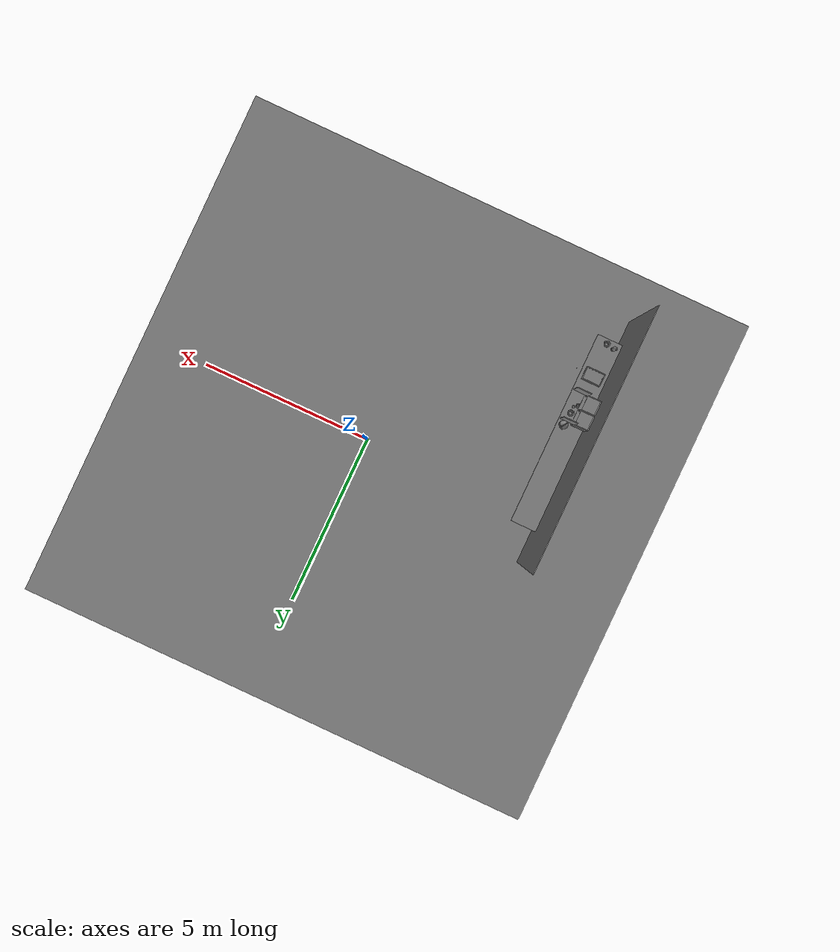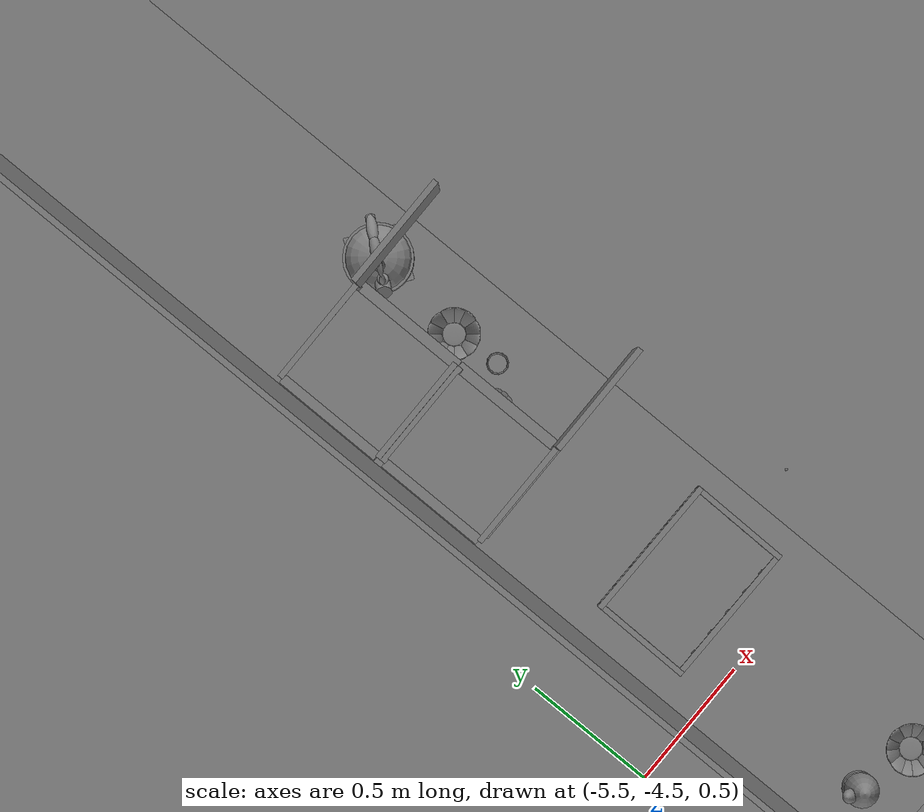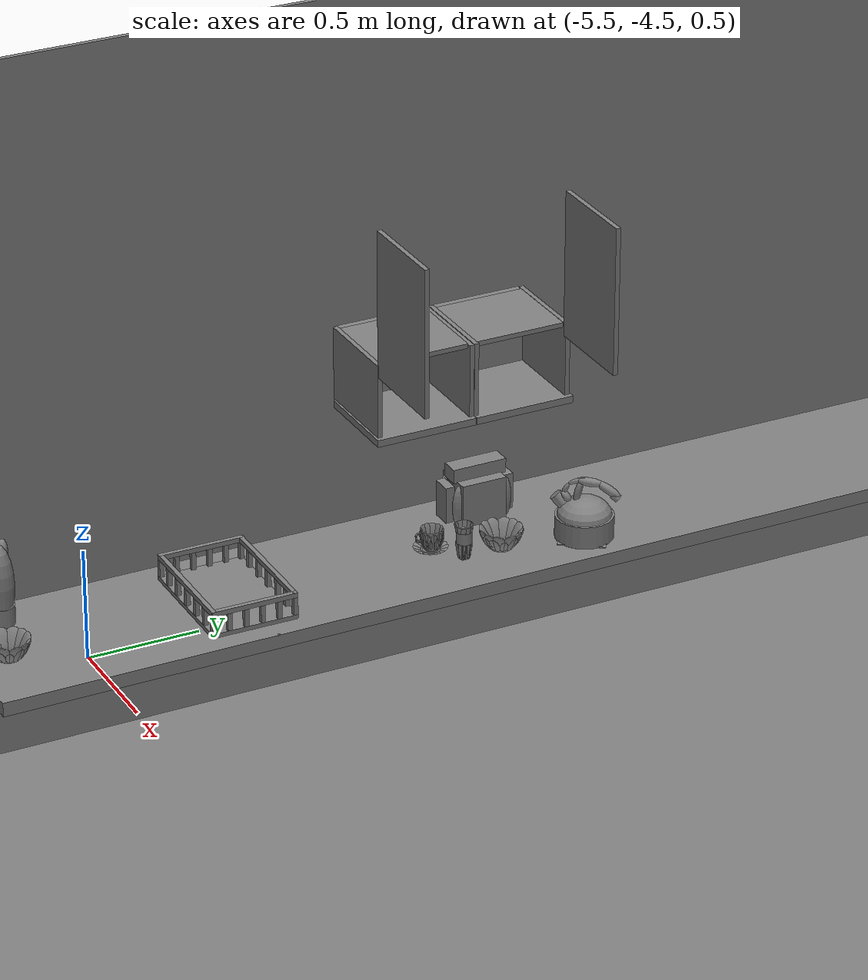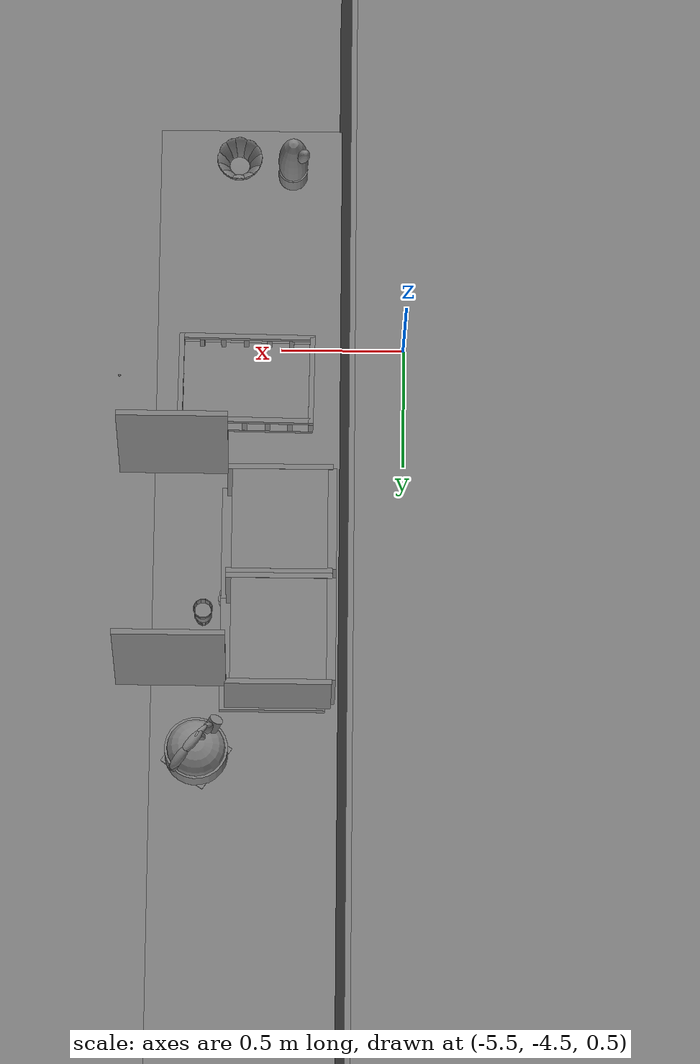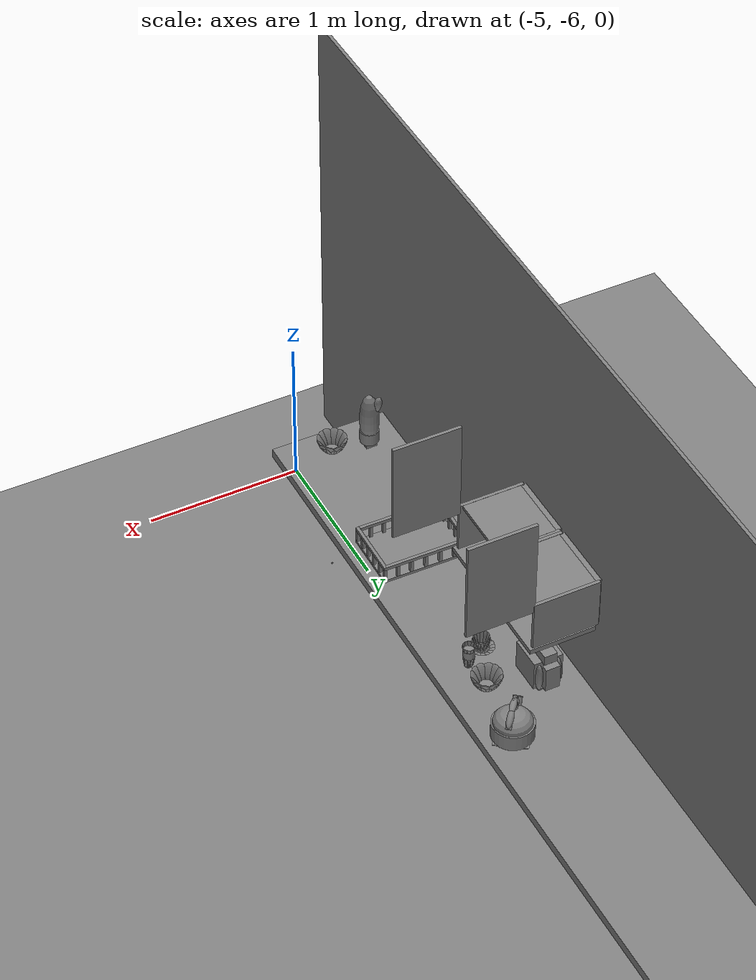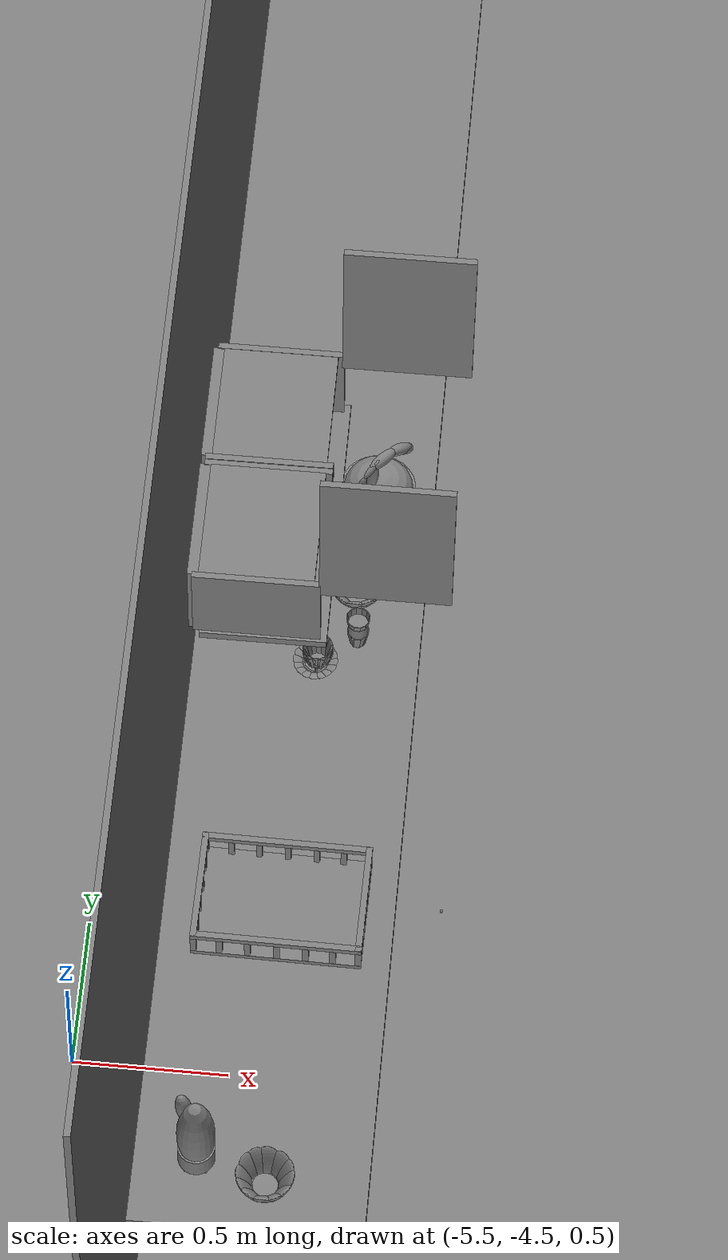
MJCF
<mujoco>
    <option gravity="0.000000000 0.000000000 -9.810000420" timestep="0.0049999999" integrator="implicitfast" density="9.8000002" viscosity="1.8000001e-05" noslip_iterations="10" iterations="100" sdf_iterations="50">
        <flag multiccd="disable"/>
    </option>
    <size memory="1000M"/>
    <compiler coordinate="local"/>
    <worldbody>
        <light cutoff="30" pos="0 1 1" dir="0 -1 -2"/>
        <light cutoff="30" pos="0 -1 1" dir="0 1 -2"/>
        <body pos="-4.860558510 -4.149443150 1.004824519" euler="0.000000000 0.000000000 -90.691108704" name="openloong_gripper_2f85_fix_base_usda_Basket_Kitchen_01">
            <geom contype="1" conaffinity="1" density="1000" type="box" material="" rgba="0.500000000 0.500000000 0.500000000 1.000000000" solimp="0.899999976 0.949999988 0.001000000" friction="1.000000000 0.005000000 0.000100000" solref="0.020000000 1.000000000" margin="0" condim="3" group="0" pos="-0.175679564 -0.000001431 0.109079957" quat="0.707107008 0.000000000 0.000000000 0.707106411" size="0.268999994 0.010000000 0.010500000" name="openloong_gripper_2f85_fix_base_usda_geom_8787073D_CAF4_43AA_B969_2DC3D4514E79"/>
            <geom contype="1" conaffinity="1" density="1000" type="box" material="" rgba="0.500000000 0.500000000 0.500000000 1.000000000" solimp="0.899999976 0.949999988 0.001000000" friction="1.000000000 0.005000000 0.000100000" solref="0.020000000 1.000000000" margin="0" condim="3" group="0" pos="-0.176020086 0.002992153 0.059861541" quat="0.707107008 0.000000000 0.000000000 0.707106411" size="0.009500000 0.009500000 0.039999999" name="openloong_gripper_2f85_fix_base_usda_geom_B4BEFC45_1E27_4688_92C0_E57913AF0B1E"/>
            <geom contype="1" conaffinity="1" density="1000" type="box" material="" rgba="0.500000000 0.500000000 0.500000000 1.000000000" solimp="0.899999976 0.949999988 0.001000000" friction="1.000000000 0.005000000 0.000100000" solref="0.020000000 1.000000000" margin="0" condim="3" group="0" pos="0.176000595 0.002991199 0.059860706" quat="0.707107008 0.000000000 0.000000000 0.707106411" size="0.009500000 0.009500000 0.039999999" name="openloong_gripper_2f85_fix_base_usda_geom_DFDBC252_AA36_4F7B_8E69_A98709C0956F"/>
            <geom contype="1" conaffinity="1" density="1000" type="box" material="" rgba="0.500000000 0.500000000 0.500000000 1.000000000" solimp="0.899999976 0.949999988 0.001000000" friction="1.000000000 0.005000000 0.000100000" solref="0.020000000 1.000000000" margin="0" condim="3" group="0" pos="0.176003456 0.259475708 0.059860110" quat="0.707107008 0.000000000 0.000000000 0.707106411" size="0.009500000 0.009500000 0.039999999" name="openloong_gripper_2f85_fix_base_usda_geom_E423C35E_1DA4_42F3_87EB_C595C5EB2B47"/>
            <geom contype="1" conaffinity="1" density="1000" type="box" material="" rgba="0.500000000 0.500000000 0.500000000 1.000000000" solimp="0.899999976 0.949999988 0.001000000" friction="1.000000000 0.005000000 0.000100000" solref="0.020000000 1.000000000" margin="0" condim="3" group="0" pos="-0.176020026 -0.088695526 0.059861422" quat="0.707107008 0.000000000 0.000000000 0.707106411" size="0.009500000 0.009500000 0.039999999" name="openloong_gripper_2f85_fix_base_usda_geom_00E01C12_83C9_407D_8985_AEF465441B67"/>
            <geom contype="1" conaffinity="1" density="1000" type="box" material="" rgba="0.500000000 0.500000000 0.500000000 1.000000000" solimp="0.899999976 0.949999988 0.001000000" friction="1.000000000 0.005000000 0.000100000" solref="0.020000000 1.000000000" margin="0" condim="3" group="0" pos="0.000000119 0.259647846 0.109080195" quat="0.707107008 0.000000000 0.000000000 0.707106411" size="0.010000000 0.185000002 0.010500000" name="openloong_gripper_2f85_fix_base_usda_geom_F59F1B18_0E14_4BD0_8848_0BEDBD571BD3"/>
            <geom contype="1" conaffinity="1" density="1000" type="box" material="" rgba="0.500000000 0.500000000 0.500000000 1.000000000" solimp="0.899999976 0.949999988 0.001000000" friction="1.000000000 0.005000000 0.000100000" solref="0.020000000 1.000000000" margin="0" condim="3" group="0" pos="0.176002026 -0.259545326 0.059860349" quat="0.707107008 0.000000000 0.000000000 0.707106411" size="0.009500000 0.009500000 0.039999999" name="openloong_gripper_2f85_fix_base_usda_geom_9C8E2072_FAE9_4D4B_8481_BA38DFF0FAEA"/>
            <geom contype="1" conaffinity="1" density="1000" type="box" material="" rgba="0.500000000 0.500000000 0.500000000 1.000000000" solimp="0.899999976 0.949999988 0.001000000" friction="1.000000000 0.005000000 0.000100000" solref="0.020000000 1.000000000" margin="0" condim="3" group="0" pos="0.036305428 -0.259545326 0.059860706" quat="0.707107008 0.000000000 0.000000000 0.707106411" size="0.009500000 0.009500000 0.039999999" name="openloong_gripper_2f85_fix_base_usda_geom_C8177931_17B4_4232_BB2A_1F471834BE51"/>
            <geom contype="1" conaffinity="1" density="1000" type="box" material="" rgba="0.500000000 0.500000000 0.500000000 1.000000000" solimp="0.899999976 0.949999988 0.001000000" friction="1.000000000 0.005000000 0.000100000" solref="0.020000000 1.000000000" margin="0" condim="3" group="0" pos="0.000000000 -0.259647369 0.109080195" quat="0.707107008 0.000000000 0.000000000 0.707106411" size="0.010000000 0.185000002 0.010500000" name="openloong_gripper_2f85_fix_base_usda_geom_CBF2AD6D_8392_4498_A4D8_D655FC09A6E4"/>
            <geom contype="1" conaffinity="1" density="1000" type="box" material="" rgba="0.500000000 0.500000000 0.500000000 1.000000000" solimp="0.899999976 0.949999988 0.001000000" friction="1.000000000 0.005000000 0.000100000" solref="0.020000000 1.000000000" margin="0" condim="3" group="0" pos="-0.034950733 -0.259545803 0.059860826" quat="0.707107008 0.000000000 0.000000000 0.707106411" size="0.009500000 0.009500000 0.039999999" name="openloong_gripper_2f85_fix_base_usda_geom_CC890C43_77EA_4889_AA2E_61A98BAE2680"/>
            <geom contype="1" conaffinity="1" density="1000" type="box" material="" rgba="0.500000000 0.500000000 0.500000000 1.000000000" solimp="0.899999976 0.949999988 0.001000000" friction="1.000000000 0.005000000 0.000100000" solref="0.020000000 1.000000000" margin="0" condim="3" group="0" pos="0.108178139 0.259475946 0.059860229" quat="0.707107008 0.000000000 0.000000000 0.707106411" size="0.009500000 0.009500000 0.039999999" name="openloong_gripper_2f85_fix_base_usda_geom_FEF9A741_9369_4660_9B50_77E107E878C5"/>
            <geom contype="1" conaffinity="1" density="1000" type="box" material="" rgba="0.500000000 0.500000000 0.500000000 1.000000000" solimp="0.899999976 0.949999988 0.001000000" friction="1.000000000 0.005000000 0.000100000" solref="0.020000000 1.000000000" margin="0" condim="3" group="0" pos="-0.106845737 0.259475231 0.059860826" quat="0.707107008 0.000000000 0.000000000 0.707106411" size="0.009500000 0.009500000 0.039999999" name="openloong_gripper_2f85_fix_base_usda_geom_3A80853D_DF55_4067_9067_B70BC0D3253E"/>
            <geom contype="1" conaffinity="1" density="1000" type="box" material="" rgba="0.500000000 0.500000000 0.500000000 1.000000000" solimp="0.899999976 0.949999988 0.001000000" friction="1.000000000 0.005000000 0.000100000" solref="0.020000000 1.000000000" margin="0" condim="3" group="0" pos="-0.176020563 0.179506302 0.059861779" quat="0.707107008 0.000000000 0.000000000 0.707106411" size="0.009500000 0.009500000 0.039999999" name="openloong_gripper_2f85_fix_base_usda_geom_F9BE18FD_43A7_436D_8538_96961CFA932E"/>
            <geom contype="1" conaffinity="1" density="1000" type="box" material="" rgba="0.500000000 0.500000000 0.500000000 1.000000000" solimp="0.899999976 0.949999988 0.001000000" friction="1.000000000 0.005000000 0.000100000" solref="0.020000000 1.000000000" margin="0" condim="3" group="0" pos="-0.034949183 0.259475946 0.059860587" quat="0.707107008 0.000000000 0.000000000 0.707106411" size="0.009500000 0.009500000 0.039999999" name="openloong_gripper_2f85_fix_base_usda_geom_671DA118_6437_404C_9553_4ED61CF71A83"/>
            <geom contype="1" conaffinity="1" density="1000" type="box" material="" rgba="0.500000000 0.500000000 0.500000000 1.000000000" solimp="0.899999976 0.949999988 0.001000000" friction="1.000000000 0.005000000 0.000100000" solref="0.020000000 1.000000000" margin="0" condim="3" group="0" pos="0.175792217 -0.000001907 0.109079838" quat="0.707107008 0.000000000 0.000000000 0.707106411" size="0.268999994 0.010000000 0.010500000" name="openloong_gripper_2f85_fix_base_usda_geom_53463553_77AF_41AF_9A98_B0C058E16CBF"/>
            <geom contype="1" conaffinity="1" density="1000" type="box" material="" rgba="0.500000000 0.500000000 0.500000000 1.000000000" solimp="0.899999976 0.949999988 0.001000000" friction="1.000000000 0.005000000 0.000100000" solref="0.020000000 1.000000000" margin="0" condim="3" group="0" pos="-0.000015259 0.000000000 0.010668159" quat="0.707107008 0.000000000 0.000000000 0.707106411" size="0.268999994 0.186000004 0.010500000" name="openloong_gripper_2f85_fix_base_usda_geom_63DF7DDC_FF31_4B2F_8154_DF340B4EBF94"/>
            <geom contype="1" conaffinity="1" density="1000" type="box" material="" rgba="0.500000000 0.500000000 0.500000000 1.000000000" solimp="0.899999976 0.949999988 0.001000000" friction="1.000000000 0.005000000 0.000100000" solref="0.020000000 1.000000000" margin="0" condim="3" group="0" pos="-0.176020086 0.094225407 0.059861660" quat="0.707107008 0.000000000 0.000000000 0.707106411" size="0.009500000 0.009500000 0.039999999" name="openloong_gripper_2f85_fix_base_usda_geom_7661BCB6_3931_4D5E_AD1B_7883C07871B3"/>
            <geom contype="1" conaffinity="1" density="1000" type="box" material="" rgba="0.500000000 0.500000000 0.500000000 1.000000000" solimp="0.899999976 0.949999988 0.001000000" friction="1.000000000 0.005000000 0.000100000" solref="0.020000000 1.000000000" margin="0" condim="3" group="0" pos="0.108177185 -0.259544849 0.059860468" quat="0.707107008 0.000000000 0.000000000 0.707106411" size="0.009500000 0.009500000 0.039999999" name="openloong_gripper_2f85_fix_base_usda_geom_C3128B32_F708_473F_9E1D_529872AAF03E"/>
            <geom contype="1" conaffinity="1" density="1000" type="box" material="" rgba="0.500000000 0.500000000 0.500000000 1.000000000" solimp="0.899999976 0.949999988 0.001000000" friction="1.000000000 0.005000000 0.000100000" solref="0.020000000 1.000000000" margin="0" condim="3" group="0" pos="-0.176019967 -0.177031994 0.059861302" quat="0.707107008 0.000000000 0.000000000 0.707106411" size="0.009500000 0.009500000 0.039999999" name="openloong_gripper_2f85_fix_base_usda_geom_C4E47A4C_6B52_4732_8DC7_E5F2C2C7AE9F"/>
            <geom contype="1" conaffinity="1" density="1000" type="box" material="" rgba="0.500000000 0.500000000 0.500000000 1.000000000" solimp="0.899999976 0.949999988 0.001000000" friction="1.000000000 0.005000000 0.000100000" solref="0.020000000 1.000000000" margin="0" condim="3" group="0" pos="-0.176020026 -0.259545326 0.059861183" quat="0.707107008 0.000000000 0.000000000 0.707106411" size="0.009500000 0.009500000 0.039999999" name="openloong_gripper_2f85_fix_base_usda_geom_28CB2E26_E80A_493D_B247_8CE10DEE9A01"/>
            <geom contype="1" conaffinity="1" density="1000" type="box" material="" rgba="0.500000000 0.500000000 0.500000000 1.000000000" solimp="0.899999976 0.949999988 0.001000000" friction="1.000000000 0.005000000 0.000100000" solref="0.020000000 1.000000000" margin="0" condim="3" group="0" pos="-0.106846333 -0.259546280 0.059861064" quat="0.707107008 0.000000000 0.000000000 0.707106411" size="0.009500000 0.009500000 0.039999999" name="openloong_gripper_2f85_fix_base_usda_geom_968E951F_27B2_4B8B_B1E6_A3E2F1D67B7D"/>
            <geom contype="1" conaffinity="1" density="1000" type="box" material="" rgba="0.500000000 0.500000000 0.500000000 1.000000000" solimp="0.899999976 0.949999988 0.001000000" friction="1.000000000 0.005000000 0.000100000" solref="0.020000000 1.000000000" margin="0" condim="3" group="0" pos="0.176000595 0.094224453 0.059860826" quat="0.707107008 0.000000000 0.000000000 0.707106411" size="0.009500000 0.009500000 0.039999999" name="openloong_gripper_2f85_fix_base_usda_geom_FC081A5C_3CBF_49C5_A0E5_6BCED883916E"/>
            <geom contype="1" conaffinity="1" density="1000" type="box" material="" rgba="0.500000000 0.500000000 0.500000000 1.000000000" solimp="0.899999976 0.949999988 0.001000000" friction="1.000000000 0.005000000 0.000100000" solref="0.020000000 1.000000000" margin="0" condim="3" group="0" pos="0.176001072 -0.088696480 0.059860587" quat="0.707107008 0.000000000 0.000000000 0.707106411" size="0.009500000 0.009500000 0.039999999" name="openloong_gripper_2f85_fix_base_usda_geom_D200DE46_D4E0_42B5_B680_F86AE02338FC"/>
            <geom contype="1" conaffinity="1" density="1000" type="box" material="" rgba="0.500000000 0.500000000 0.500000000 1.000000000" solimp="0.899999976 0.949999988 0.001000000" friction="1.000000000 0.005000000 0.000100000" solref="0.020000000 1.000000000" margin="0" condim="3" group="0" pos="0.036307096 0.259476185 0.059860468" quat="0.707107008 0.000000000 0.000000000 0.707106411" size="0.009500000 0.009500000 0.039999999" name="openloong_gripper_2f85_fix_base_usda_geom_6E87EDED_A5F2_4749_AA8B_23D38D42026D"/>
            <geom contype="1" conaffinity="1" density="1000" type="box" material="" rgba="0.500000000 0.500000000 0.500000000 1.000000000" solimp="0.899999976 0.949999988 0.001000000" friction="1.000000000 0.005000000 0.000100000" solref="0.020000000 1.000000000" margin="0" condim="3" group="0" pos="0.176001549 -0.177031994 0.059860468" quat="0.707107008 0.000000000 0.000000000 0.707106411" size="0.009500000 0.009500000 0.039999999" name="openloong_gripper_2f85_fix_base_usda_geom_A41386A5_2333_46DC_914C_2315DD553577"/>
            <geom contype="1" conaffinity="1" density="1000" type="box" material="" rgba="0.500000000 0.500000000 0.500000000 1.000000000" solimp="0.899999976 0.949999988 0.001000000" friction="1.000000000 0.005000000 0.000100000" solref="0.020000000 1.000000000" margin="0" condim="3" group="0" pos="0.176000118 0.179505348 0.059860945" quat="0.707107008 0.000000000 0.000000000 0.707106411" size="0.009500000 0.009500000 0.039999999" name="openloong_gripper_2f85_fix_base_usda_geom_B1FF01FA_2E9F_4A87_98D6_47ECDE4DD056"/>
            <geom contype="1" conaffinity="1" density="1000" type="box" material="" rgba="0.500000000 0.500000000 0.500000000 1.000000000" solimp="0.899999976 0.949999988 0.001000000" friction="1.000000000 0.005000000 0.000100000" solref="0.020000000 1.000000000" margin="0" condim="3" group="0" pos="-0.176020086 0.259474993 0.059860945" quat="0.707107008 0.000000000 0.000000000 0.707106411" size="0.009500000 0.009500000 0.039999999" name="openloong_gripper_2f85_fix_base_usda_geom_77CCCFDF_8101_4952_BD07_685CEB796F8A"/>
            <freejoint name="openloong_gripper_2f85_fix_base_usda_Basket_Kitchen_01_joint"/>
        </body>
        <body pos="-4.802892208 -3.488179445 1.876015186" euler="89.999992371 -89.999946594 0.000000000" name="Interactive Objcets_guimen_01">
            <geom contype="1" conaffinity="1" density="1000" type="box" material="" rgba="0.500000000 0.500000000 0.500000000 1.000000000" solimp="0.899999976 0.949999988 0.001000000" friction="1.000000000 0.005000000 0.000100000" solref="0.020000000 1.000000000" margin="0" condim="3" group="0" pos="0.006727934 0.314709902 -0.203009605" quat="1.000000000 0.000000119 -0.000000119 0.000000000" size="0.010000000 0.317999989 0.204999998" name="Interactive Objcets_geom_2B17E60A_1B18_4D71_8D52_FCD80E84DDC1"/>
            <joint armature="0" stiffness="0" damping="1" axis="0.000000 1.000000 0.000000" type="hinge" name="Interactive Objcets_guimen_01"/>
        </body>
        <body pos="-4.805274963 -2.665403366 1.876015186" euler="89.999877930 89.999969482 0.000000000" name="Interactive Objcets_guimen_02">
            <geom contype="1" conaffinity="1" density="1000" type="box" material="" rgba="0.500000000 0.500000000 0.500000000 1.000000000" solimp="0.899999976 0.949999988 0.001000000" friction="1.000000000 0.005000000 0.000100000" solref="0.020000000 1.000000000" margin="0" condim="3" group="0" pos="0.006727815 0.314709663 0.203009367" quat="0.999999940 0.000000000 0.000000000 0.000000000" size="0.010000000 0.317999989 0.204999998" name="Interactive Objcets_geom_CC416949_5AA7_4180_9E12_7766E981CB4C"/>
            <joint armature="0" stiffness="0" damping="1" axis="0.000000 1.000000 0.000000" type="hinge" name="Interactive Objcets_guimen_02"/>
        </body>
        <body pos="-4.827295780 -3.287638187 1.074643731" euler="0.000000000 0.000000000 89.999992371" name="Interactive Objcets_coffeecup_01">
            <geom contype="1" conaffinity="1" density="1000" type="ellipsoid" material="" rgba="0.500000000 0.500000000 0.500000000 1.000000000" solimp="0.899999976 0.949999988 0.001000000" friction="1.000000000 0.005000000 0.000100000" solref="0.020000000 1.000000000" margin="0" condim="3" group="0" pos="0.035336256 0.000558376 -0.043215394" quat="0.999999881 0.000000000 0.000000000 0.000000000" size="0.029999999 0.029999999 0.001000000" name="Interactive Objcets_geom_87B71E90_4C48_4CF5_8083_385B33BF0D19"/>
            <geom contype="1" conaffinity="1" density="1000" type="ellipsoid" material="" rgba="0.500000000 0.500000000 0.500000000 1.000000000" solimp="0.899999976 0.949999988 0.001000000" friction="1.000000000 0.005000000 0.000100000" solref="0.020000000 1.000000000" margin="0" condim="3" group="0" pos="0.067416430 -0.018191338 0.002976775" quat="0.961934388 0.024418317 0.091648072 -0.256293803" size="0.005000000 0.029999999 0.048999999" name="Interactive Objcets_geom_9045E7D5_F6F7_4E49_9729_CBBC11D9B884"/>
            <geom contype="1" conaffinity="1" density="1000" type="ellipsoid" material="" rgba="0.500000000 0.500000000 0.500000000 1.000000000" solimp="0.899999976 0.949999988 0.001000000" friction="1.000000000 0.005000000 0.000100000" solref="0.020000000 1.000000000" margin="0" condim="3" group="0" pos="0.034471050 -0.037125111 0.002976775" quat="0.701517045 0.067293778 0.066836871 -0.706313014" size="0.005000000 0.029999999 0.048999999" name="Interactive Objcets_geom_CCE89565_DEB4_46BB_9D91_788170363B61"/>
            <geom contype="1" conaffinity="1" density="1000" type="ellipsoid" material="" rgba="0.500000000 0.500000000 0.500000000 1.000000000" solimp="0.899999976 0.949999988 0.001000000" friction="1.000000000 0.005000000 0.000100000" solref="0.020000000 1.000000000" margin="0" condim="3" group="0" pos="0.035336256 0.000558376 -0.045152068" quat="0.999999881 0.000000000 0.000000000 0.000000000" size="0.029999999 0.029999999 0.001000000" name="Interactive Objcets_geom_D3CA37C7_DB9A_48BD_9C3E_E349A7863EBD"/>
            <geom contype="1" conaffinity="1" density="1000" type="ellipsoid" material="" rgba="0.500000000 0.500000000 0.500000000 1.000000000" solimp="0.899999976 0.949999988 0.001000000" friction="1.000000000 0.005000000 0.000100000" solref="0.020000000 1.000000000" margin="0" condim="3" group="0" pos="0.001010895 -0.016271591 0.002976775" quat="0.228377163 0.092315644 0.021758538 -0.968941689" size="0.005000000 0.029999999 0.048999999" name="Interactive Objcets_geom_C33850F8_AEC3_47EE_A7D1_AEE602FF7516"/>
            <geom contype="1" conaffinity="1" density="1000" type="capsule" material="" rgba="0.500000000 0.500000000 0.500000000 1.000000000" solimp="0.899999976 0.949999988 0.001000000" friction="1.000000000 0.005000000 0.000100000" solref="0.020000000 1.000000000" margin="0" condim="3" group="0" pos="-0.021276474 0.000000000 0.038509369" quat="0.633189917 0.000000000 0.773996413 0.000000000" size="0.004000000 0.009000000 1.000000000" name="Interactive Objcets_geom_36368BDF_A113_4EEE_A496_02DD115A522E"/>
            <geom contype="1" conaffinity="1" density="1000" type="capsule" material="" rgba="0.500000000 0.500000000 0.500000000 1.000000000" solimp="0.899999976 0.949999988 0.001000000" friction="1.000000000 0.005000000 0.000100000" solref="0.020000000 1.000000000" margin="0" condim="3" group="0" pos="-0.018014431 0.000000000 0.001762271" quat="0.707106769 -0.000000004 0.707106709 -0.000000088" size="0.004000000 0.005000000 1.000000000" name="Interactive Objcets_geom_690CF585_C3D1_4F8F_AE49_5C40C496E769"/>
            <geom contype="1" conaffinity="1" density="1000" type="ellipsoid" material="" rgba="0.500000000 0.500000000 0.500000000 1.000000000" solimp="0.899999976 0.949999988 0.001000000" friction="1.000000000 0.005000000 0.000100000" solref="0.020000000 1.000000000" margin="0" condim="3" group="0" pos="0.068445444 0.017385960 0.002976775" quat="0.228377223 -0.092319682 -0.021759447 -0.968941331" size="0.005000000 0.029999999 0.048999999" name="Interactive Objcets_geom_533C2687_3DD5_460A_A784_FD88ECE8CE41"/>
            <geom contype="1" conaffinity="1" density="1000" type="ellipsoid" material="" rgba="0.500000000 0.500000000 0.500000000 1.000000000" solimp="0.899999976 0.949999988 0.001000000" friction="1.000000000 0.005000000 0.000100000" solref="0.020000000 1.000000000" margin="0" condim="3" group="0" pos="0.002039194 0.019308567 0.002976775" quat="0.961933970 -0.024419386 -0.091652036 -0.256293654" size="0.005000000 0.029999999 0.048999999" name="Interactive Objcets_geom_1DB8562B_29A9_40C3_9FFE_134F1EE17E3E"/>
            <geom contype="1" conaffinity="1" density="1000" type="ellipsoid" material="" rgba="0.500000000 0.500000000 0.500000000 1.000000000" solimp="0.899999976 0.949999988 0.001000000" friction="1.000000000 0.005000000 0.000100000" solref="0.020000000 1.000000000" margin="0" condim="3" group="0" pos="0.034984604 0.038240910 0.002976775" quat="0.701516926 -0.067296736 -0.066839755 -0.706312656" size="0.005000000 0.029999999 0.048999999" name="Interactive Objcets_geom_6A11DE6D_A900_4EA5_BC1E_34E21FF7CF02"/>
            <geom contype="1" conaffinity="1" density="1000" type="ellipsoid" material="" rgba="0.500000000 0.500000000 0.500000000 1.000000000" solimp="0.899999976 0.949999988 0.001000000" friction="1.000000000 0.005000000 0.000100000" solref="0.020000000 1.000000000" margin="0" condim="3" group="0" pos="0.017669693 0.034160614 0.002976775" quat="0.848410904 -0.049618516 -0.080835648 -0.520770907" size="0.005000000 0.029999999 0.048999999" name="Interactive Objcets_geom_677F880E_8211_44EA_ACE2_B911F0C9BA49"/>
            <geom contype="1" conaffinity="1" density="1000" type="ellipsoid" material="" rgba="0.500000000 0.500000000 0.500000000 1.000000000" solimp="0.899999976 0.949999988 0.001000000" friction="1.000000000 0.005000000 0.000100000" solref="0.020000000 1.000000000" margin="0" condim="3" group="0" pos="-0.002956629 0.000558376 0.002976775" quat="0.995491505 0.000000004 -0.094849378 -0.000000089" size="0.005000000 0.029999999 0.048999999" name="Interactive Objcets_geom_F3E7B8DB_796E_4AA4_8FFC_4FED3D2A101A"/>
            <geom contype="1" conaffinity="1" density="1000" type="ellipsoid" material="" rgba="0.500000000 0.500000000 0.500000000 1.000000000" solimp="0.899999976 0.949999988 0.001000000" friction="1.000000000 0.005000000 0.000100000" solref="0.020000000 1.000000000" margin="0" condim="3" group="0" pos="0.051787138 -0.033043861 0.002976775" quat="0.848411202 0.049616337 0.080832161 -0.520771146" size="0.005000000 0.029999999 0.048999999" name="Interactive Objcets_geom_1E264B1D_1161_4A93_A6BE_1E979B59A9CD"/>
            <geom contype="1" conaffinity="1" density="1000" type="capsule" material="" rgba="0.500000000 0.500000000 0.500000000 1.000000000" solimp="0.899999976 0.949999988 0.001000000" friction="1.000000000 0.005000000 0.000100000" solref="0.020000000 1.000000000" margin="0" condim="3" group="0" pos="-0.030251026 0.000000000 0.004966617" quat="0.480583906 -0.000000000 0.876948774 -0.000000126" size="0.004000000 0.005000000 1.000000000" name="Interactive Objcets_geom_76694F04_9D3C_4C69_BC25_22FC323B15F6"/>
            <geom contype="1" conaffinity="1" density="1000" type="capsule" material="" rgba="0.500000000 0.500000000 0.500000000 1.000000000" solimp="0.899999976 0.949999988 0.001000000" friction="1.000000000 0.005000000 0.000100000" solref="0.020000000 1.000000000" margin="0" condim="3" group="0" pos="-0.036300898 0.000000000 0.021037936" quat="0.044551343 -0.000000000 0.999007046 -0.000000126" size="0.004000000 0.012000000 1.000000000" name="Interactive Objcets_geom_14553604_2609_42D2_B94B_857EDC6CE7F0"/>
            <geom contype="1" conaffinity="1" density="1000" type="capsule" material="" rgba="0.500000000 0.500000000 0.500000000 1.000000000" solimp="0.899999976 0.949999988 0.001000000" friction="1.000000000 0.005000000 0.000100000" solref="0.020000000 1.000000000" margin="0" condim="3" group="0" pos="-0.008219719 0.000000000 -0.000944734" quat="0.364379913 0.000000063 0.931250274 -0.000000063" size="0.004000000 0.003000000 1.000000000" name="Interactive Objcets_geom_956E023B_816D_4E54_BF55_6757C0AE421C"/>
            <geom contype="1" conaffinity="1" density="1000" type="capsule" material="" rgba="0.500000000 0.500000000 0.500000000 1.000000000" solimp="0.899999976 0.949999988 0.001000000" friction="1.000000000 0.005000000 0.000100000" solref="0.020000000 1.000000000" margin="0" condim="3" group="0" pos="-0.033022881 0.000000000 0.037873149" quat="0.874267220 0.000000042 0.485444903 -0.000000084" size="0.004000000 0.004000000 1.000000000" name="Interactive Objcets_geom_33C7398D_6D64_4533_BC0E_60C874D09431"/>
            <geom contype="1" conaffinity="1" density="1000" type="ellipsoid" material="" rgba="0.500000000 0.500000000 0.500000000 1.000000000" solimp="0.899999976 0.949999988 0.001000000" friction="1.000000000 0.005000000 0.000100000" solref="0.020000000 1.000000000" margin="0" condim="3" group="0" pos="0.015755907 -0.032001972 0.002976775" quat="0.496025920 0.082232773 0.047258731 -0.863112032" size="0.005000000 0.029999999 0.048999999" name="Interactive Objcets_geom_95031A9C_A539_4390_81E8_BA4EA2F1B736"/>
            <geom contype="1" conaffinity="1" density="1000" type="ellipsoid" material="" rgba="0.500000000 0.500000000 0.500000000 1.000000000" solimp="0.899999976 0.949999988 0.001000000" friction="1.000000000 0.005000000 0.000100000" solref="0.020000000 1.000000000" margin="0" condim="3" group="0" pos="0.072411790 0.000558376 0.002976775" quat="0.995491922 -0.000000019 0.094845265 -0.000000089" size="0.005000000 0.029999999 0.048999999" name="Interactive Objcets_geom_F84278B8_B1C6_444F_ADAB_A46ADC8952CE"/>
            <geom contype="1" conaffinity="1" density="1000" type="ellipsoid" material="" rgba="0.500000000 0.500000000 0.500000000 1.000000000" solimp="0.899999976 0.949999988 0.001000000" friction="1.000000000 0.005000000 0.000100000" solref="0.020000000 1.000000000" margin="0" condim="3" group="0" pos="0.053700209 0.033117294 0.002976775" quat="0.496025741 -0.082236379 -0.047260769 -0.863111615" size="0.005000000 0.029999999 0.048999999" name="Interactive Objcets_geom_1F50B77F_F117_4EFF_9A2C_2F42D26708ED"/>
            <freejoint name="Interactive Objcets_coffeecup_01"/>
        </body>
        <body pos="-5.020127296 -2.953741550 1.135127425" euler="89.999946594 0.000000000 0.000000000" name="Interactive Objcets_Bread">
            <geom contype="1" conaffinity="1" density="1000" type="box" material="" rgba="0.500000000 0.500000000 0.500000000 1.000000000" solimp="0.899999976 0.949999988 0.001000000" friction="1.000000000 0.005000000 0.000100000" solref="0.020000000 1.000000000" margin="0" condim="3" group="0" pos="-0.008702755 -0.017670274 -0.135069147" quat="0.707107067 -0.707106471 0.000000021 -0.000000021" size="0.045000002 0.020000000 0.079999998" name="Interactive Objcets_geom_9EB4C0AC_8910_4EEB_BC19_321D773330BA"/>
            <geom contype="1" conaffinity="1" density="1000" type="box" material="" rgba="0.500000000 0.500000000 0.500000000 1.000000000" solimp="0.899999976 0.949999988 0.001000000" friction="1.000000000 0.005000000 0.000100000" solref="0.020000000 1.000000000" margin="0" condim="3" group="0" pos="0.033925056 -0.123201847 0.086778767" quat="0.707107067 -0.707106471 0.000000021 -0.000000021" size="0.020000000 0.020000000 0.005000000" name="Interactive Objcets_geom_46D3027F_9618_429B_8A4C_EA733051A398"/>
            <geom contype="1" conaffinity="1" density="1000" type="box" material="" rgba="0.500000000 0.500000000 0.500000000 1.000000000" solimp="0.899999976 0.949999988 0.001000000" friction="1.000000000 0.005000000 0.000100000" solref="0.020000000 1.000000000" margin="0" condim="3" group="0" pos="-0.008702755 -0.016588926 0.000174277" quat="0.707107067 -0.707106471 0.000000021 -0.000000021" size="0.090000004 0.100000001 0.094999999" name="Interactive Objcets_geom_D508FAFB_0463_412F_BFE9_12B6C6C42C35"/>
            <geom contype="1" conaffinity="1" density="1000" type="ellipsoid" material="" rgba="0.500000000 0.500000000 0.500000000 1.000000000" solimp="0.899999976 0.949999988 0.001000000" friction="1.000000000 0.005000000 0.000100000" solref="0.020000000 1.000000000" margin="0" condim="3" group="0" pos="-0.067312241 -0.026057482 -0.101716787" quat="0.707107067 -0.707106471 0.000000021 -0.000000021" size="0.020000000 0.029999999 0.094999999" name="Interactive Objcets_geom_9A305C8E_BC26_49EA_8782_22E3CE79C813"/>
            <geom contype="1" conaffinity="1" density="1000" type="ellipsoid" material="" rgba="0.500000000 0.500000000 0.500000000 1.000000000" solimp="0.899999976 0.949999988 0.001000000" friction="1.000000000 0.005000000 0.000100000" solref="0.020000000 1.000000000" margin="0" condim="3" group="0" pos="0.052222252 -0.026057363 0.101459242" quat="0.707107067 -0.707106471 0.000000021 -0.000000021" size="0.020000000 0.029999999 0.094999999" name="Interactive Objcets_geom_48D61FAD_7CAE_4EE7_BA3F_613785C6F1FB"/>
            <geom contype="1" conaffinity="1" density="1000" type="box" material="" rgba="0.500000000 0.500000000 0.500000000 1.000000000" solimp="0.899999976 0.949999988 0.001000000" friction="1.000000000 0.005000000 0.000100000" solref="0.020000000 1.000000000" margin="0" condim="3" group="0" pos="-0.050020695 -0.123201847 0.086778767" quat="0.707107067 -0.707106471 0.000000021 -0.000000021" size="0.020000000 0.020000000 0.005000000" name="Interactive Objcets_geom_8E81CB92_F7BB_4958_A0D7_500B5B602AE4"/>
            <geom contype="1" conaffinity="1" density="1000" type="box" material="" rgba="0.500000000 0.500000000 0.500000000 1.000000000" solimp="0.899999976 0.949999988 0.001000000" friction="1.000000000 0.005000000 0.000100000" solref="0.020000000 1.000000000" margin="0" condim="3" group="0" pos="0.033925056 -0.123201728 -0.092369899" quat="0.707107067 -0.707106471 0.000000021 -0.000000021" size="0.020000000 0.020000000 0.005000000" name="Interactive Objcets_geom_DC324A06_62BB_4F3E_B8B8_1A838389A6C2"/>
            <geom contype="1" conaffinity="1" density="1000" type="ellipsoid" material="" rgba="0.500000000 0.500000000 0.500000000 1.000000000" solimp="0.899999976 0.949999988 0.001000000" friction="1.000000000 0.005000000 0.000100000" solref="0.020000000 1.000000000" margin="0" condim="3" group="0" pos="-0.069190502 -0.026057363 0.101458766" quat="0.707107067 -0.707106471 0.000000021 -0.000000021" size="0.020000000 0.029999999 0.094999999" name="Interactive Objcets_geom_D9328D08_A1F8_48BA_9733_80DB9F42B658"/>
            <geom contype="1" conaffinity="1" density="1000" type="box" material="" rgba="0.500000000 0.500000000 0.500000000 1.000000000" solimp="0.899999976 0.949999988 0.001000000" friction="1.000000000 0.005000000 0.000100000" solref="0.020000000 1.000000000" margin="0" condim="3" group="0" pos="-0.008702755 -0.017670155 0.134585604" quat="0.707107067 -0.707106471 0.000000021 -0.000000021" size="0.045000002 0.020000000 0.079999998" name="Interactive Objcets_geom_33F68F8E_2A2E_4FA5_8883_FB710F4E7868"/>
            <geom contype="1" conaffinity="1" density="1000" type="box" material="" rgba="0.500000000 0.500000000 0.500000000 1.000000000" solimp="0.899999976 0.949999988 0.001000000" friction="1.000000000 0.005000000 0.000100000" solref="0.020000000 1.000000000" margin="0" condim="3" group="0" pos="-0.050020695 -0.123201728 -0.092370376" quat="0.707107067 -0.707106471 0.000000021 -0.000000021" size="0.020000000 0.020000000 0.005000000" name="Interactive Objcets_geom_85A46AE3_F11A_49E4_830B_62BF50D2EB75"/>
            <geom contype="1" conaffinity="1" density="1000" type="box" material="" rgba="0.500000000 0.500000000 0.500000000 1.000000000" solimp="0.899999976 0.949999988 0.001000000" friction="1.000000000 0.005000000 0.000100000" solref="0.020000000 1.000000000" margin="0" condim="3" group="0" pos="-0.008702755 0.104617000 -0.003706597" quat="0.707107067 -0.707106471 0.000000021 -0.000000021" size="0.039999999 0.119999997 0.030999999" name="Interactive Objcets_geom_E6615213_4285_4995_855A_2081870054FF"/>
            <geom contype="1" conaffinity="1" density="1000" type="ellipsoid" material="" rgba="0.500000000 0.500000000 0.500000000 1.000000000" solimp="0.899999976 0.949999988 0.001000000" friction="1.000000000 0.005000000 0.000100000" solref="0.020000000 1.000000000" margin="0" condim="3" group="0" pos="0.052222252 -0.026057243 -0.106481344" quat="0.707107067 -0.707106471 0.000000021 -0.000000021" size="0.020000000 0.029999999 0.094999999" name="Interactive Objcets_geom_761F1ECC_9102_4B74_9023_DC1FFABCEA7E"/>
            <freejoint name="Interactive Objcets_Bread"/>
        </body>
        <body pos="-4.821335316 -5.105734825 1.007418752" euler="0.000000000 0.000000000 89.999946594" name="Interactive Objcets_bow_04">
            <geom contype="1" conaffinity="1" density="1000" type="ellipsoid" material="" rgba="0.500000000 0.500000000 0.500000000 1.000000000" solimp="0.899999976 0.949999988 0.001000000" friction="1.000000000 0.005000000 0.000100000" solref="0.020000000 1.000000000" margin="0" condim="3" group="0" pos="0.052321672 -0.040297985 0.044118762" quat="0.919264674 0.076882720 0.225593746 -0.313287675" size="0.010000000 0.039999999 0.052000001" name="Interactive Objcets_geom_F2F534CD_9F6F_4569_87B7_2A57ED505B17"/>
            <geom contype="1" conaffinity="1" density="1000" type="ellipsoid" material="" rgba="0.500000000 0.500000000 0.500000000 1.000000000" solimp="0.899999976 0.949999988 0.001000000" friction="1.000000000 0.005000000 0.000100000" solref="0.020000000 1.000000000" margin="0" condim="3" group="0" pos="0.059080124 0.029511929 0.044118762" quat="0.223252952 -0.231952190 -0.054787360 -0.945174456" size="0.010000000 0.039999999 0.052000001" name="Interactive Objcets_geom_56814D55_C90D_435E_9C04_2AD0EF219E82"/>
            <geom contype="1" conaffinity="1" density="1000" type="ellipsoid" material="" rgba="0.500000000 0.500000000 0.500000000 1.000000000" solimp="0.899999976 0.949999988 0.001000000" friction="1.000000000 0.005000000 0.000100000" solref="0.020000000 1.000000000" margin="0" condim="3" group="0" pos="0.000082970 0.000000000 0.003118873" quat="1.000000000 0.000000000 0.000000000 0.000000000" size="0.039999999 0.039999999 0.002000000" name="Interactive Objcets_geom_56462134_8A7E_4EEA_929B_164B5BE28E2B"/>
            <geom contype="1" conaffinity="1" density="1000" type="ellipsoid" material="" rgba="0.500000000 0.500000000 0.500000000 1.000000000" solimp="0.899999976 0.949999988 0.001000000" friction="1.000000000 0.005000000 0.000100000" solref="0.020000000 1.000000000" margin="0" condim="3" group="0" pos="-0.040080309 -0.052354813 0.044118762" quat="0.429593146 0.213749856 0.105425127 -0.871003032" size="0.010000000 0.039999999 0.052000001" name="Interactive Objcets_geom_62829A8D_8E63_4F0F_8227_FDBBAA792FDD"/>
            <geom contype="1" conaffinity="1" density="1000" type="ellipsoid" material="" rgba="0.500000000 0.500000000 0.500000000 1.000000000" solimp="0.899999976 0.949999988 0.001000000" friction="1.000000000 0.005000000 0.000100000" solref="0.020000000 1.000000000" margin="0" condim="3" group="0" pos="0.000243664 -0.065983295 0.044118762" quat="0.687598884 0.168314576 0.168741226 -0.685860336" size="0.010000000 0.039999999 0.052000001" name="Interactive Objcets_geom_97BC7932_A704_4C0B_A7EA_0751BD43B6BC"/>
            <geom contype="1" conaffinity="1" density="1000" type="ellipsoid" material="" rgba="0.500000000 0.500000000 0.500000000 1.000000000" solimp="0.899999976 0.949999988 0.001000000" friction="1.000000000 0.005000000 0.000100000" solref="0.020000000 1.000000000" margin="0" condim="3" group="0" pos="-0.065898657 -0.000007629 0.044118762" quat="0.971183062 -0.000000142 -0.238334835 0.000000030" size="0.010000000 0.039999999 0.052000001" name="Interactive Objcets_geom_D79A5F45_A184_4435_9744_F6AC4F91B178"/>
            <geom contype="1" conaffinity="1" density="1000" type="ellipsoid" material="" rgba="0.500000000 0.500000000 0.500000000 1.000000000" solimp="0.899999976 0.949999988 0.001000000" friction="1.000000000 0.005000000 0.000100000" solref="0.020000000 1.000000000" margin="0" condim="3" group="0" pos="-0.052167892 0.040281773 0.044118762" quat="0.919264615 -0.076883025 -0.225593626 -0.313287735" size="0.010000000 0.039999999 0.052000001" name="Interactive Objcets_geom_A58C72B3_D417_4B67_BE70_2BB0F749B6B8"/>
            <geom contype="1" conaffinity="1" density="1000" type="ellipsoid" material="" rgba="0.500000000 0.500000000 0.500000000 1.000000000" solimp="0.899999976 0.949999988 0.001000000" friction="1.000000000 0.005000000 0.000100000" solref="0.020000000 1.000000000" margin="0" condim="3" group="0" pos="-0.029293537 0.059069157 0.044118762" quat="0.825556040 -0.125530839 -0.202596709 -0.511521041" size="0.010000000 0.039999999 0.052000001" name="Interactive Objcets_geom_D719DA18_0B4C_44E3_9E9F_0DC2114424D9"/>
            <geom contype="1" conaffinity="1" density="1000" type="ellipsoid" material="" rgba="0.500000000 0.500000000 0.500000000 1.000000000" solimp="0.899999976 0.949999988 0.001000000" friction="1.000000000 0.005000000 0.000100000" solref="0.020000000 1.000000000" margin="0" condim="3" group="0" pos="0.000082970 0.000000000 0.000446677" quat="1.000000000 0.000000000 0.000000000 0.000000000" size="0.039999999 0.039999999 0.002000000" name="Interactive Objcets_geom_C370796E_68F8_4119_BDA2_9B5742C3D5F0"/>
            <geom contype="1" conaffinity="1" density="1000" type="ellipsoid" material="" rgba="0.500000000 0.500000000 0.500000000 1.000000000" solimp="0.899999976 0.949999988 0.001000000" friction="1.000000000 0.005000000 0.000100000" solref="0.020000000 1.000000000" margin="0" condim="3" group="0" pos="0.029448032 -0.059085369 0.044118762" quat="0.825555801 0.125530601 0.202597082 -0.511521280" size="0.010000000 0.039999999 0.052000001" name="Interactive Objcets_geom_A259F04F_BE23_48C2_B593_1C237DCF7E29"/>
            <geom contype="1" conaffinity="1" density="1000" type="ellipsoid" material="" rgba="0.500000000 0.500000000 0.500000000 1.000000000" solimp="0.899999976 0.949999988 0.001000000" friction="1.000000000 0.005000000 0.000100000" solref="0.020000000 1.000000000" margin="0" condim="3" group="0" pos="0.066051960 -0.000007629 0.044118762" quat="0.971183062 -0.000000156 0.238334835 0.000000030" size="0.010000000 0.039999999 0.052000001" name="Interactive Objcets_geom_BB4D54BA_E10E_4DCE_9748_822E104F7681"/>
            <geom contype="1" conaffinity="1" density="1000" type="ellipsoid" material="" rgba="0.500000000 0.500000000 0.500000000 1.000000000" solimp="0.899999976 0.949999988 0.001000000" friction="1.000000000 0.005000000 0.000100000" solref="0.020000000 1.000000000" margin="0" condim="3" group="0" pos="-0.058925867 -0.029528618 0.044118762" quat="0.223252863 0.231952116 0.054787725 -0.945174456" size="0.010000000 0.039999999 0.052000001" name="Interactive Objcets_geom_529BBF20_FDFB_4CB3_B66F_781760D2665E"/>
            <geom contype="1" conaffinity="1" density="1000" type="ellipsoid" material="" rgba="0.500000000 0.500000000 0.500000000 1.000000000" solimp="0.899999976 0.949999988 0.001000000" friction="1.000000000 0.005000000 0.000100000" solref="0.020000000 1.000000000" margin="0" condim="3" group="0" pos="0.040234327 0.052339077 0.044118762" quat="0.429593533 -0.213750005 -0.105424747 -0.871002972" size="0.010000000 0.039999999 0.052000001" name="Interactive Objcets_geom_75BA4E44_166B_40B0_9776_B79537A8F3E3"/>
            <geom contype="1" conaffinity="1" density="1000" type="ellipsoid" material="" rgba="0.500000000 0.500000000 0.500000000 1.000000000" solimp="0.899999976 0.949999988 0.001000000" friction="1.000000000 0.005000000 0.000100000" solref="0.020000000 1.000000000" margin="0" condim="3" group="0" pos="-0.000090122 0.065967083 0.044118762" quat="0.687598825 -0.168314755 -0.168741047 -0.685860395" size="0.010000000 0.039999999 0.052000001" name="Interactive Objcets_geom_2E35264E_4938_4828_89E3_B32888F1C3D3"/>
            <freejoint name="Interactive Objcets_bow_04"/>
        </body>
        <body pos="-4.685121059 -2.618872881 1.139834642" euler="-89.999885559 -75.046211243 -179.999633789" name="Interactive Objcets_shuihu">
            <geom contype="1" conaffinity="1" density="1000" type="ellipsoid" material="" rgba="0.500000000 0.500000000 0.500000000 1.000000000" solimp="0.899999976 0.949999988 0.001000000" friction="1.000000000 0.005000000 0.000100000" solref="0.020000000 1.000000000" margin="0" condim="3" group="0" pos="0.076839805 0.041928887 0.028444767" quat="0.777403057 0.260122687 0.543099582 -0.181723833" size="0.020000000 0.029999999 0.015000000" name="Interactive Objcets_geom_FE4C5E50_333A_455E_94EB_0B763DAB8CDD"/>
            <geom contype="1" conaffinity="1" density="1000" type="cylinder" material="" rgba="0.500000000 0.500000000 0.500000000 1.000000000" solimp="0.899999976 0.949999988 0.001000000" friction="1.000000000 0.005000000 0.000100000" solref="0.020000000 1.000000000" margin="0" condim="3" group="0" pos="0.006719470 -0.083229184 -0.000185013" quat="0.579664290 -0.579662681 0.404957741 0.404956520" size="0.123000003 0.050000001 1.000000000" name="Interactive Objcets_geom_F04AD894_EAD1_43B4_B715_26210D5132F5"/>
            <geom contype="1" conaffinity="1" density="1000" type="cylinder" material="" rgba="0.500000000 0.500000000 0.500000000 1.000000000" solimp="0.899999976 0.949999988 0.001000000" friction="1.000000000 0.005000000 0.000100000" solref="0.020000000 1.000000000" margin="0" condim="3" group="0" pos="0.097564876 0.019223809 0.042538166" quat="0.757945418 -0.330064029 0.507527351 0.242883876" size="0.027000001 0.032499999 1.000000000" name="Interactive Objcets_geom_F44A0C21_25B5_4983_A181_FE7B05F13844"/>
            <geom contype="1" conaffinity="1" density="1000" type="ellipsoid" material="" rgba="0.500000000 0.500000000 0.500000000 1.000000000" solimp="0.899999976 0.949999988 0.001000000" friction="1.000000000 0.005000000 0.000100000" solref="0.020000000 1.000000000" margin="0" condim="3" group="0" pos="0.006307602 -0.038442492 -0.000561237" quat="0.579664290 -0.579662681 0.404957741 0.404956520" size="0.115000002 0.115000002 0.079999998" name="Interactive Objcets_geom_7AE185AD_A291_4A64_9A6A_2D0713535581"/>
            <geom contype="1" conaffinity="1" density="1000" type="ellipsoid" material="" rgba="0.500000000 0.500000000 0.500000000 1.000000000" solimp="0.899999976 0.949999988 0.001000000" friction="1.000000000 0.005000000 0.000100000" solref="0.020000000 1.000000000" margin="0" condim="3" group="0" pos="0.079775751 0.074323297 0.032407284" quat="0.807211578 -0.212389767 0.536951303 0.122406662" size="0.011000000 0.029999999 0.010000000" name="Interactive Objcets_geom_22650D28_6F88_4389_A68E_A9CDF6C12CB3"/>
            <geom contype="1" conaffinity="1" density="1000" type="cylinder" material="" rgba="0.500000000 0.500000000 0.500000000 1.000000000" solimp="0.899999976 0.949999988 0.001000000" friction="1.000000000 0.005000000 0.000100000" solref="0.020000000 1.000000000" margin="0" condim="3" group="0" pos="-0.109747589 0.061178923 -0.054180622" quat="0.791120291 -0.252390862 0.522301614 0.193980843" size="0.017000001 0.015000000 1.000000000" name="Interactive Objcets_geom_E94093C3_40B9_47F0_9EAC_4F8F0391433C"/>
            <geom contype="1" conaffinity="1" density="1000" type="box" material="" rgba="0.500000000 0.500000000 0.500000000 1.000000000" solimp="0.899999976 0.949999988 0.001000000" friction="1.000000000 0.005000000 0.000100000" solref="0.020000000 1.000000000" margin="0" condim="3" group="0" pos="0.006720424 -0.132364750 -0.000183582" quat="0.579664230 -0.579662681 0.404957652 0.404956520" size="0.100000001 0.100000001 0.005000000" name="Interactive Objcets_geom_FCB73A33_E5EC_4AD1_B145_E6A204015875"/>
            <geom contype="1" conaffinity="1" density="1000" type="ellipsoid" material="" rgba="0.500000000 0.500000000 0.500000000 1.000000000" solimp="0.899999976 0.949999988 0.001000000" friction="1.000000000 0.005000000 0.000100000" solref="0.020000000 1.000000000" margin="0" condim="3" group="0" pos="-0.012925148 0.115441918 -0.008463383" quat="0.573223114 -0.617213011 0.363985062 0.397464871" size="0.020000000 0.059999999 0.017999999" name="Interactive Objcets_geom_475BA6E0_E072_4038_9805_9E94D4E5408A"/>
            <geom contype="1" conaffinity="1" density="1000" type="ellipsoid" material="" rgba="0.500000000 0.500000000 0.500000000 1.000000000" solimp="0.899999976 0.949999988 0.001000000" friction="1.000000000 0.005000000 0.000100000" solref="0.020000000 1.000000000" margin="0" condim="3" group="0" pos="0.036164403 0.116219044 0.012343884" quat="0.691036344 -0.468154669 0.465933800 0.293608427" size="0.011000000 0.039999999 0.010000000" name="Interactive Objcets_geom_93A54C74_7A4B_478F_B41F_040CEA4C3855"/>
            <geom contype="1" conaffinity="1" density="1000" type="ellipsoid" material="" rgba="0.500000000 0.500000000 0.500000000 1.000000000" solimp="0.899999976 0.949999988 0.001000000" friction="1.000000000 0.005000000 0.000100000" solref="0.020000000 1.000000000" margin="0" condim="3" group="0" pos="-0.081469536 0.090929627 -0.040654182" quat="0.423473954 -0.728255510 0.250199795 0.477193654" size="0.020000000 0.059999999 0.017999999" name="Interactive Objcets_geom_037B4201_9A9B_48FC_A16B_FF65A6081012"/>
            <geom contype="1" conaffinity="1" density="1000" type="ellipsoid" material="" rgba="0.500000000 0.500000000 0.500000000 1.000000000" solimp="0.899999976 0.949999988 0.001000000" friction="1.000000000 0.005000000 0.000100000" solref="0.020000000 1.000000000" margin="0" condim="3" group="0" pos="0.031587839 0.066336274 0.011863232" quat="0.813834965 -0.098448642 0.568551302 0.068776846" size="0.020000000 0.059999999 0.015000000" name="Interactive Objcets_geom_29A6C87E_3C5A_4617_8BFD_A0FEB26A33DC"/>
            <freejoint name="Interactive Objcets_shuihu"/>
        </body>
        <body pos="-4.835184574 -3.254794121 1.033557892" euler="0.000000000 0.000000000 0.000000000" name="Interactive Objcets_cupplate_01">
            <geom contype="1" conaffinity="1" density="1000" type="ellipsoid" material="" rgba="0.500000000 0.500000000 0.500000000 1.000000000" solimp="0.899999976 0.949999988 0.001000000" friction="1.000000000 0.005000000 0.000100000" solref="0.020000000 1.000000000" margin="0" condim="3" group="0" pos="0.022432804 0.052464008 0.000154614" quat="0.455865860 -0.467545629 -0.308059722 -0.691871881" size="0.002000000 0.020000000 0.017000001" name="Interactive Objcets_geom_A260AA88_C95F_4184_A547_1702B07E526D"/>
            <geom contype="1" conaffinity="1" density="1000" type="ellipsoid" material="" rgba="0.500000000 0.500000000 0.500000000 1.000000000" solimp="0.899999976 0.949999988 0.001000000" friction="1.000000000 0.005000000 0.000100000" solref="0.020000000 1.000000000" margin="0" condim="3" group="0" pos="-0.052522659 0.022613287 0.000154614" quat="0.811438143 -0.113215551 -0.548344791 -0.167535841" size="0.002000000 0.020000000 0.017000001" name="Interactive Objcets_geom_CA7B13F8_AFEE_4ED1_AF6F_1A5FA6A8A691"/>
            <geom contype="1" conaffinity="1" density="1000" type="ellipsoid" material="" rgba="0.500000000 0.500000000 0.500000000 1.000000000" solimp="0.899999976 0.949999988 0.001000000" friction="1.000000000 0.005000000 0.000100000" solref="0.020000000 1.000000000" margin="0" condim="3" group="0" pos="0.052457333 0.022318602 0.000154614" quat="0.165263638 -0.548659503 -0.111679509 -0.811904132" size="0.002000000 0.020000000 0.017000001" name="Interactive Objcets_geom_7A245E40_5778_487A_8869_241A41A05396"/>
            <geom contype="1" conaffinity="1" density="1000" type="ellipsoid" material="" rgba="0.500000000 0.500000000 0.500000000 1.000000000" solimp="0.899999976 0.949999988 0.001000000" friction="1.000000000 0.005000000 0.000100000" solref="0.020000000 1.000000000" margin="0" condim="3" group="0" pos="0.057000160 0.000000477 0.000000000" quat="0.828553081 0.000000000 0.559910476 0.000000000" size="0.002000000 0.020000000 0.017000001" name="Interactive Objcets_geom_CE06C1F6_9447_47B0_B17F_D1150F413531"/>
            <geom contype="1" conaffinity="1" density="1000" type="ellipsoid" material="" rgba="0.500000000 0.500000000 0.500000000 1.000000000" solimp="0.899999976 0.949999988 0.001000000" friction="1.000000000 0.005000000 0.000100000" solref="0.020000000 1.000000000" margin="0" condim="3" group="0" pos="-0.000003815 -0.057095528 0.000000000" quat="0.586347640 0.395597160 0.396235406 -0.585402966" size="0.002000000 0.020000000 0.017000001" name="Interactive Objcets_geom_83F6851C_96E5_4B4A_9F1E_237B7E444BC7"/>
            <geom contype="1" conaffinity="1" density="1000" type="ellipsoid" material="" rgba="0.500000000 0.500000000 0.500000000 1.000000000" solimp="0.899999976 0.949999988 0.001000000" friction="1.000000000 0.005000000 0.000100000" solref="0.020000000 1.000000000" margin="0" condim="3" group="0" pos="-0.041719437 -0.039082766 0.000000000" quat="0.304989874 0.520597219 0.206102297 -0.770377457" size="0.002000000 0.020000000 0.017000001" name="Interactive Objcets_geom_3E2BF001_FC86_4FA5_8EE8_AE9132676AE5"/>
            <geom contype="1" conaffinity="1" density="1000" type="ellipsoid" material="" rgba="0.500000000 0.500000000 0.500000000 1.000000000" solimp="0.899999976 0.949999988 0.001000000" friction="1.000000000 0.005000000 0.000100000" solref="0.020000000 1.000000000" margin="0" condim="3" group="0" pos="0.041527748 0.039082766 0.000154614" quat="0.304989874 -0.520597219 -0.206102297 -0.770377457" size="0.002000000 0.020000000 0.017000001" name="Interactive Objcets_geom_5FB78636_9B5D_4F5A_AB63_99C0FAD02185"/>
            <geom contype="1" conaffinity="1" density="1000" type="ellipsoid" material="" rgba="0.500000000 0.500000000 0.500000000 1.000000000" solimp="0.899999976 0.949999988 0.001000000" friction="1.000000000 0.005000000 0.000100000" solref="0.020000000 1.000000000" margin="0" condim="3" group="0" pos="-0.057191849 0.000000477 0.000154614" quat="0.828553081 0.000000000 -0.559910476 0.000000000" size="0.002000000 0.020000000 0.017000001" name="Interactive Objcets_geom_C06F9B89_BF3B_4A71_A4FB_4CD4BBBE2344"/>
            <geom contype="1" conaffinity="1" density="1000" type="ellipsoid" material="" rgba="0.500000000 0.500000000 0.500000000 1.000000000" solimp="0.899999976 0.949999988 0.001000000" friction="1.000000000 0.005000000 0.000100000" solref="0.020000000 1.000000000" margin="0" condim="3" group="0" pos="0.000000000 0.000000000 -0.007192612" quat="1.000000000 0.000000000 0.000000000 0.000000000" size="0.039999999 0.039999999 0.001000000" name="Interactive Objcets_geom_9567BF8E_270A_4335_9C09_CBC91F42D0C8"/>
            <geom contype="1" conaffinity="1" density="1000" type="ellipsoid" material="" rgba="0.500000000 0.500000000 0.500000000 1.000000000" solimp="0.899999976 0.949999988 0.001000000" friction="1.000000000 0.005000000 0.000100000" solref="0.020000000 1.000000000" margin="0" condim="3" group="0" pos="0.022139072 -0.052588940 0.000000119" quat="0.690592766 0.309367865 0.466681093 -0.457801163" size="0.002000000 0.020000000 0.017000001" name="Interactive Objcets_geom_38571B1F_DD99_4F79_89EB_5CB4CF178CB2"/>
            <geom contype="1" conaffinity="1" density="1000" type="ellipsoid" material="" rgba="0.500000000 0.500000000 0.500000000 1.000000000" solimp="0.899999976 0.949999988 0.001000000" friction="1.000000000 0.005000000 0.000100000" solref="0.020000000 1.000000000" margin="0" condim="3" group="0" pos="-0.052649021 -0.022319317 0.000000119" quat="0.165263638 0.548659503 0.111679509 -0.811904132" size="0.002000000 0.020000000 0.017000001" name="Interactive Objcets_geom_74E15873_CF17_49C6_AD03_AA6136B150D5"/>
            <geom contype="1" conaffinity="1" density="1000" type="ellipsoid" material="" rgba="0.500000000 0.500000000 0.500000000 1.000000000" solimp="0.899999976 0.949999988 0.001000000" friction="1.000000000 0.005000000 0.000100000" solref="0.020000000 1.000000000" margin="0" condim="3" group="0" pos="0.052331448 -0.022612572 0.000000000" quat="0.811438143 0.113215551 0.548344791 -0.167535841" size="0.002000000 0.020000000 0.017000001" name="Interactive Objcets_geom_EBB342DF_BE9B_44C5_AFDC_808F49E8407D"/>
            <geom contype="1" conaffinity="1" density="1000" type="ellipsoid" material="" rgba="0.500000000 0.500000000 0.500000000 1.000000000" solimp="0.899999976 0.949999988 0.001000000" friction="1.000000000 0.005000000 0.000100000" solref="0.020000000 1.000000000" margin="0" condim="3" group="0" pos="-0.000187874 0.057096481 0.000154614" quat="0.586347640 -0.395597160 -0.396235406 -0.585402966" size="0.002000000 0.020000000 0.017000001" name="Interactive Objcets_geom_091A5E9B_3456_4678_B57E_122F15684117"/>
            <geom contype="1" conaffinity="1" density="1000" type="ellipsoid" material="" rgba="0.500000000 0.500000000 0.500000000 1.000000000" solimp="0.899999976 0.949999988 0.001000000" friction="1.000000000 0.005000000 0.000100000" solref="0.020000000 1.000000000" margin="0" condim="3" group="0" pos="-0.039110661 0.041686535 0.000154614" quat="0.760133922 -0.222795680 -0.513674736 -0.329691947" size="0.002000000 0.020000000 0.017000001" name="Interactive Objcets_geom_213A6CF7_3FF6_4949_9C12_34977C0505B7"/>
            <geom contype="1" conaffinity="1" density="1000" type="ellipsoid" material="" rgba="0.500000000 0.500000000 0.500000000 1.000000000" solimp="0.899999976 0.949999988 0.001000000" friction="1.000000000 0.005000000 0.000100000" solref="0.020000000 1.000000000" margin="0" condim="3" group="0" pos="-0.022624493 -0.052463770 0.000000000" quat="0.455865860 0.467545629 0.308059722 -0.691871881" size="0.002000000 0.020000000 0.017000001" name="Interactive Objcets_geom_20462760_D215_4ECE_B1FF_E3C877BDCAE1"/>
            <geom contype="1" conaffinity="1" density="1000" type="ellipsoid" material="" rgba="0.500000000 0.500000000 0.500000000 1.000000000" solimp="0.899999976 0.949999988 0.001000000" friction="1.000000000 0.005000000 0.000100000" solref="0.020000000 1.000000000" margin="0" condim="3" group="0" pos="0.000000000 0.000000000 -0.006308794" quat="1.000000000 0.000000000 0.000000000 0.000000000" size="0.035000000 0.035000000 0.001000000" name="Interactive Objcets_geom_2F685A0A_321C_4682_B82B_A76A3E443326"/>
            <geom contype="1" conaffinity="1" density="1000" type="ellipsoid" material="" rgba="0.500000000 0.500000000 0.500000000 1.000000000" solimp="0.899999976 0.949999988 0.001000000" friction="1.000000000 0.005000000 0.000100000" solref="0.020000000 1.000000000" margin="0" condim="3" group="0" pos="-0.022329807 0.052588463 0.000154614" quat="0.690592766 -0.309367865 -0.466681093 -0.457801163" size="0.002000000 0.020000000 0.017000001" name="Interactive Objcets_geom_E0B9AF32_B8B7_4C92_BF85_6EC6B41D73A3"/>
            <geom contype="1" conaffinity="1" density="1000" type="ellipsoid" material="" rgba="0.500000000 0.500000000 0.500000000 1.000000000" solimp="0.899999976 0.949999988 0.001000000" friction="1.000000000 0.005000000 0.000100000" solref="0.020000000 1.000000000" margin="0" condim="3" group="0" pos="0.038919926 -0.041685820 0.000000000" quat="0.760133922 0.222795680 0.513674736 -0.329691947" size="0.002000000 0.020000000 0.017000001" name="Interactive Objcets_geom_9042F2A8_D5B7_413E_9E19_12F8DAE3CD4A"/>
            <freejoint name="Interactive Objcets_cupplate_01"/>
        </body>
        <body pos="-4.721817970 -2.990536690 1.027358174" euler="0.000000000 0.000000000 89.999946594" name="Interactive Objcets_bow_02">
            <geom contype="1" conaffinity="1" density="1000" type="ellipsoid" material="" rgba="0.500000000 0.500000000 0.500000000 1.000000000" solimp="0.899999976 0.949999988 0.001000000" friction="1.000000000 0.005000000 0.000100000" solref="0.020000000 1.000000000" margin="0" condim="3" group="0" pos="0.052321676 -0.040297508 0.044118762" quat="0.919264674 0.076882742 0.225593731 -0.313287675" size="0.010000000 0.039999999 0.052000001" name="Interactive Objcets_geom_A151C8F3_FE77_4CE6_A991_E3FA106FCA78"/>
            <geom contype="1" conaffinity="1" density="1000" type="ellipsoid" material="" rgba="0.500000000 0.500000000 0.500000000 1.000000000" solimp="0.899999976 0.949999988 0.001000000" friction="1.000000000 0.005000000 0.000100000" solref="0.020000000 1.000000000" margin="0" condim="3" group="0" pos="0.040234569 0.052338600 0.044118762" quat="0.429593176 -0.213750035 -0.105424814 -0.871002913" size="0.010000000 0.039999999 0.052000001" name="Interactive Objcets_geom_D881C1D4_171D_47C2_A963_79CFCAE629C1"/>
            <geom contype="1" conaffinity="1" density="1000" type="ellipsoid" material="" rgba="0.500000000 0.500000000 0.500000000 1.000000000" solimp="0.899999976 0.949999988 0.001000000" friction="1.000000000 0.005000000 0.000100000" solref="0.020000000 1.000000000" margin="0" condim="3" group="0" pos="0.029448029 -0.059084892 0.044118762" quat="0.825555801 0.125530601 0.202597082 -0.511521280" size="0.010000000 0.039999999 0.052000001" name="Interactive Objcets_geom_E88949A5_8964_4B21_9C1B_5A13DCF1350B"/>
            <geom contype="1" conaffinity="1" density="1000" type="ellipsoid" material="" rgba="0.500000000 0.500000000 0.500000000 1.000000000" solimp="0.899999976 0.949999988 0.001000000" friction="1.000000000 0.005000000 0.000100000" solref="0.020000000 1.000000000" margin="0" condim="3" group="0" pos="-0.058925860 -0.029528141 0.044118762" quat="0.223252773 0.231952101 0.054787740 -0.945174515" size="0.010000000 0.039999999 0.052000001" name="Interactive Objcets_geom_99A6AAAD_BD8D_448C_82AD_DBAF36AAD5CD"/>
            <geom contype="1" conaffinity="1" density="1000" type="ellipsoid" material="" rgba="0.500000000 0.500000000 0.500000000 1.000000000" solimp="0.899999976 0.949999988 0.001000000" friction="1.000000000 0.005000000 0.000100000" solref="0.020000000 1.000000000" margin="0" condim="3" group="0" pos="-0.040080305 -0.052354336 0.044118762" quat="0.429593205 0.213749886 0.105425082 -0.871003032" size="0.010000000 0.039999999 0.052000001" name="Interactive Objcets_geom_962E5710_7A93_40F4_9A30_12CAA03D0A99"/>
            <geom contype="1" conaffinity="1" density="1000" type="ellipsoid" material="" rgba="0.500000000 0.500000000 0.500000000 1.000000000" solimp="0.899999976 0.949999988 0.001000000" friction="1.000000000 0.005000000 0.000100000" solref="0.020000000 1.000000000" margin="0" condim="3" group="0" pos="0.000082973 0.000000000 0.005656481" quat="1.000000000 0.000000000 0.000000000 0.000000000" size="0.039999999 0.039999999 0.002000000" name="Interactive Objcets_geom_001DA449_78F7_4C33_8C1E_28A362376745"/>
            <geom contype="1" conaffinity="1" density="1000" type="ellipsoid" material="" rgba="0.500000000 0.500000000 0.500000000 1.000000000" solimp="0.899999976 0.949999988 0.001000000" friction="1.000000000 0.005000000 0.000100000" solref="0.020000000 1.000000000" margin="0" condim="3" group="0" pos="-0.065898418 -0.000007629 0.044118762" quat="0.971183062 -0.000000142 -0.238334835 0.000000030" size="0.010000000 0.039999999 0.052000001" name="Interactive Objcets_geom_8D444AAF_5383_4BF9_A6A9_A255FE88F294"/>
            <geom contype="1" conaffinity="1" density="1000" type="ellipsoid" material="" rgba="0.500000000 0.500000000 0.500000000 1.000000000" solimp="0.899999976 0.949999988 0.001000000" friction="1.000000000 0.005000000 0.000100000" solref="0.020000000 1.000000000" margin="0" condim="3" group="0" pos="-0.000090118 0.065967560 0.044118762" quat="0.687598705 -0.168314859 -0.168741152 -0.685860336" size="0.010000000 0.039999999 0.052000001" name="Interactive Objcets_geom_2DA3F8B9_FE77_4C64_BD8B_26D710C1DC69"/>
            <geom contype="1" conaffinity="1" density="1000" type="ellipsoid" material="" rgba="0.500000000 0.500000000 0.500000000 1.000000000" solimp="0.899999976 0.949999988 0.001000000" friction="1.000000000 0.005000000 0.000100000" solref="0.020000000 1.000000000" margin="0" condim="3" group="0" pos="-0.052167647 0.040282249 0.044118762" quat="0.919264615 -0.076883025 -0.225593641 -0.313287735" size="0.010000000 0.039999999 0.052000001" name="Interactive Objcets_geom_5C2DD540_AB85_4D87_881A_1D5F48594883"/>
            <geom contype="1" conaffinity="1" density="1000" type="ellipsoid" material="" rgba="0.500000000 0.500000000 0.500000000 1.000000000" solimp="0.899999976 0.949999988 0.001000000" friction="1.000000000 0.005000000 0.000100000" solref="0.020000000 1.000000000" margin="0" condim="3" group="0" pos="0.059080135 0.029512405 0.044118762" quat="0.223252743 -0.231952220 -0.054787420 -0.945174456" size="0.010000000 0.039999999 0.052000001" name="Interactive Objcets_geom_037EAD3B_29BA_4546_B72E_2335695EBC92"/>
            <geom contype="1" conaffinity="1" density="1000" type="ellipsoid" material="" rgba="0.500000000 0.500000000 0.500000000 1.000000000" solimp="0.899999976 0.949999988 0.001000000" friction="1.000000000 0.005000000 0.000100000" solref="0.020000000 1.000000000" margin="0" condim="3" group="0" pos="0.000243668 -0.065982819 0.044118762" quat="0.687598705 0.168314636 0.168741375 -0.685860336" size="0.010000000 0.039999999 0.052000001" name="Interactive Objcets_geom_44384F98_5867_4F2D_A3BE_61509CB0BF1A"/>
            <geom contype="1" conaffinity="1" density="1000" type="ellipsoid" material="" rgba="0.500000000 0.500000000 0.500000000 1.000000000" solimp="0.899999976 0.949999988 0.001000000" friction="1.000000000 0.005000000 0.000100000" solref="0.020000000 1.000000000" margin="0" condim="3" group="0" pos="0.066052437 -0.000007629 0.044118762" quat="0.971183062 -0.000000156 0.238334835 0.000000030" size="0.010000000 0.039999999 0.052000001" name="Interactive Objcets_geom_7342C386_C801_4619_B422_E3CECE8BA0DF"/>
            <geom contype="1" conaffinity="1" density="1000" type="ellipsoid" material="" rgba="0.500000000 0.500000000 0.500000000 1.000000000" solimp="0.899999976 0.949999988 0.001000000" friction="1.000000000 0.005000000 0.000100000" solref="0.020000000 1.000000000" margin="0" condim="3" group="0" pos="0.000082973 0.000000000 0.000446677" quat="1.000000000 0.000000000 0.000000000 0.000000000" size="0.039999999 0.039999999 0.002000000" name="Interactive Objcets_geom_DEAA2B7F_9ABE_4141_864C_BFFFB5951D5B"/>
            <geom contype="1" conaffinity="1" density="1000" type="ellipsoid" material="" rgba="0.500000000 0.500000000 0.500000000 1.000000000" solimp="0.899999976 0.949999988 0.001000000" friction="1.000000000 0.005000000 0.000100000" solref="0.020000000 1.000000000" margin="0" condim="3" group="0" pos="-0.029293532 0.059069633 0.044118762" quat="0.825555801 -0.125530809 -0.202596903 -0.511521280" size="0.010000000 0.039999999 0.052000001" name="Interactive Objcets_geom_08F5C4D1_82A2_412A_89A2_0D50642985BD"/>
            <freejoint name="Interactive Objcets_bow_02"/>
        </body>
        <body pos="-5.046103477 -5.051773071 1.001502514" euler="0.000000000 0.000000000 0.000000000" name="Interactive Objcets_huapen">
            <geom contype="1" conaffinity="1" density="1000" type="ellipsoid" material="" rgba="0.500000000 0.500000000 0.500000000 1.000000000" solimp="0.899999976 0.949999988 0.001000000" friction="1.000000000 0.005000000 0.000100000" solref="0.020000000 1.000000000" margin="0" condim="3" group="0" pos="0.008062840 0.004346371 0.205056787" quat="1.000000000 0.000000000 0.000000000 0.000000000" size="0.059999999 0.059999999 0.180000007" name="Interactive Objcets_huapen_hua_FCB3E025_F8CF_4FB4_9500_A0740C643CDA"/>
            <geom contype="1" conaffinity="1" density="1000" type="ellipsoid" material="" rgba="0.500000000 0.500000000 0.500000000 1.000000000" solimp="0.899999976 0.949999988 0.001000000" friction="1.000000000 0.005000000 0.000100000" solref="0.020000000 1.000000000" margin="0" condim="3" group="0" pos="-0.029900074 0.033599377 0.321917295" quat="0.992658079 -0.083605267 -0.087364964 0.002748166" size="0.025000000 0.025000000 0.059999999" name="Interactive Objcets_huapen_hua_217F605F_D128_4481_B647_9BE1FBC1282A"/>
            <geom contype="1" conaffinity="1" density="1000" type="box" material="" rgba="0.500000000 0.500000000 0.500000000 1.000000000" solimp="0.899999976 0.949999988 0.001000000" friction="1.000000000 0.005000000 0.000100000" solref="0.020000000 1.000000000" margin="0" condim="3" group="0" pos="0.008062840 0.003952503 0.020566106" quat="1.000000000 0.000000000 0.000000000 0.000000000" size="0.035000000 0.035000000 0.020000000" name="Interactive Objcets_huapen_hua_088CE944_3C20_40F8_8079_9059AB3F291D"/>
            <geom contype="1" conaffinity="1" density="1000" type="cylinder" material="" rgba="0.500000000 0.500000000 0.500000000 1.000000000" solimp="0.899999976 0.949999988 0.001000000" friction="1.000000000 0.005000000 0.000100000" solref="0.020000000 1.000000000" margin="0" condim="3" group="0" pos="0.008062840 0.003952026 0.080107450" quat="1.000000000 0.000000000 0.000000000 0.000000000" size="0.057999998 0.039999999 1.000000000" name="Interactive Objcets_huapen_hua_948927E3_6AB1_4413_A958_3940E8FABED2"/>
            <freejoint name="Interactive Objcets_huapen"/>
        </body>
        <body pos="-4.705342293 -3.169416904 1.103703976" euler="0.000000000 0.000000000 0.000000000" name="Interactive Objcets_cup_02">
            <geom contype="1" conaffinity="1" density="1000" type="box" material="" rgba="0.500000000 0.500000000 0.500000000 1.000000000" solimp="0.899999976 0.949999988 0.001000000" friction="1.000000000 0.005000000 0.000100000" solref="0.020000000 1.000000000" margin="0" condim="3" group="0" pos="0.022285938 0.016949892 -0.037281752" quat="0.893179297 -0.070051625 0.034732576 -0.442851186" size="0.010000000 0.001000000 0.035000000" name="Interactive Objcets_geom_F628A51F_606E_48EE_82A8_2B3C4756E96D"/>
            <geom contype="1" conaffinity="1" density="1000" type="box" material="" rgba="0.500000000 0.500000000 0.500000000 1.000000000" solimp="0.899999976 0.949999988 0.001000000" friction="1.000000000 0.005000000 0.000100000" solref="0.020000000 1.000000000" margin="0" condim="3" group="0" pos="0.034549713 0.000000000 0.062637210" quat="0.704941988 -0.055288255 0.055288251 -0.704942048" size="0.010000000 0.001000000 0.015000000" name="Interactive Objcets_geom_66ED93BE_517C_41B2_A617_3B896B7E5249"/>
            <geom contype="1" conaffinity="1" density="1000" type="box" material="" rgba="0.500000000 0.500000000 0.500000000 1.000000000" solimp="0.899999976 0.949999988 0.001000000" friction="1.000000000 0.005000000 0.000100000" solref="0.020000000 1.000000000" margin="0" condim="3" group="0" pos="0.029378891 -0.018181801 0.062637210" quat="0.870895982 0.068302706 0.038053915 0.485208035" size="0.010000000 0.001000000 0.015000000" name="Interactive Objcets_geom_4D08B84B_1398_4364_8DFD_B4E561832320"/>
            <geom contype="1" conaffinity="1" density="1000" type="box" material="" rgba="0.500000000 0.500000000 0.500000000 1.000000000" solimp="0.899999976 0.949999988 0.001000000" friction="1.000000000 0.005000000 0.000100000" solref="0.020000000 1.000000000" margin="0" condim="3" group="0" pos="0.000000000 -0.034549713 0.062637210" quat="0.996938646 0.078187965 0.000000000 0.000000000" size="0.010000000 0.001000000 0.015000000" name="Interactive Objcets_geom_1D8896ED_4825_4C16_B081_B5312A75FC84"/>
            <geom contype="1" conaffinity="1" density="1000" type="cylinder" material="" rgba="0.500000000 0.500000000 0.500000000 1.000000000" solimp="0.899999976 0.949999988 0.001000000" friction="1.000000000 0.005000000 0.000100000" solref="0.020000000 1.000000000" margin="0" condim="3" group="0" pos="0.000000000 0.000000000 0.022491097" quat="1.000000000 0.000000030 0.000000000 0.000000000" size="0.033000000 0.025000000 1.000000000" name="Interactive Objcets_geom_03161346_F7B0_4E2D_A9B6_E720651ABEC2"/>
            <geom contype="1" conaffinity="1" density="1000" type="box" material="" rgba="0.500000000 0.500000000 0.500000000 1.000000000" solimp="0.899999976 0.949999988 0.001000000" friction="1.000000000 0.005000000 0.000100000" solref="0.020000000 1.000000000" margin="0" condim="3" group="0" pos="0.000000000 0.034549713 0.062637210" quat="0.996938646 -0.078187965 0.000000000 0.000000000" size="0.010000000 0.001000000 0.015000000" name="Interactive Objcets_geom_B3795408_53C1_4AE8_B75A_471422C43EA1"/>
            <geom contype="1" conaffinity="1" density="1000" type="box" material="" rgba="0.500000000 0.500000000 0.500000000 1.000000000" solimp="0.899999976 0.949999988 0.001000000" friction="1.000000000 0.005000000 0.000100000" solref="0.020000000 1.000000000" margin="0" condim="3" group="0" pos="0.011943817 0.025323629 -0.037281752" quat="0.972834349 -0.076298930 0.017089661 -0.217898533" size="0.010000000 0.001000000 0.035000000" name="Interactive Objcets_geom_3B785C09_C017_41AC_B74C_702BB62436D2"/>
            <geom contype="1" conaffinity="1" density="1000" type="box" material="" rgba="0.500000000 0.500000000 0.500000000 1.000000000" solimp="0.899999976 0.949999988 0.001000000" friction="1.000000000 0.005000000 0.000100000" solref="0.020000000 1.000000000" margin="0" condim="3" group="0" pos="0.025214195 -0.011892319 -0.037281752" quat="0.841975451 0.066034243 0.041866414 0.533820212" size="0.010000000 0.001000000 0.035000000" name="Interactive Objcets_geom_30078ACB_EA1A_4B5B_A18E_CE5ABD36F2A3"/>
            <geom contype="1" conaffinity="1" density="1000" type="box" material="" rgba="0.500000000 0.500000000 0.500000000 1.000000000" solimp="0.899999976 0.949999988 0.001000000" friction="1.000000000 0.005000000 0.000100000" solref="0.020000000 1.000000000" margin="0" condim="3" group="0" pos="-0.027999878 0.000000000 -0.037281752" quat="0.704941988 0.055288255 -0.055288251 -0.704942048" size="0.010000000 0.001000000 0.035000000" name="Interactive Objcets_geom_8FD31C79_BA1A_46D2_815E_29A62AD08D03"/>
            <geom contype="1" conaffinity="1" density="1000" type="box" material="" rgba="0.500000000 0.500000000 0.500000000 1.000000000" solimp="0.899999976 0.949999988 0.001000000" friction="1.000000000 0.005000000 0.000100000" solref="0.020000000 1.000000000" margin="0" condim="3" group="0" pos="0.017436981 -0.029826880 0.062637210" quat="0.962265730 0.075468659 0.020441191 0.260636479" size="0.010000000 0.001000000 0.015000000" name="Interactive Objcets_geom_16BC4DCA_A537_4C21_80B6_CA86A42DB0A9"/>
            <geom contype="1" conaffinity="1" density="1000" type="box" material="" rgba="0.500000000 0.500000000 0.500000000 1.000000000" solimp="0.899999976 0.949999988 0.001000000" friction="1.000000000 0.005000000 0.000100000" solref="0.020000000 1.000000000" margin="0" condim="3" group="0" pos="0.029827118 0.017437220 0.062637210" quat="0.864722252 -0.067819774 0.038910985 -0.496126890" size="0.010000000 0.001000000 0.015000000" name="Interactive Objcets_geom_BBDAA689_9AF3_4F73_8DCD_4F9400E112E6"/>
            <geom contype="1" conaffinity="1" density="1000" type="box" material="" rgba="0.500000000 0.500000000 0.500000000 1.000000000" solimp="0.899999976 0.949999988 0.001000000" friction="1.000000000 0.005000000 0.000100000" solref="0.020000000 1.000000000" margin="0" condim="3" group="0" pos="0.000000000 0.027877331 -0.037281752" quat="0.996938646 -0.078187965 0.000000000 0.000000000" size="0.010000000 0.001000000 0.035000000" name="Interactive Objcets_geom_80B33A0A_222E_4A3B_B2F8_1604B8976C8C"/>
            <geom contype="1" conaffinity="1" density="1000" type="box" material="" rgba="0.500000000 0.500000000 0.500000000 1.000000000" solimp="0.899999976 0.949999988 0.001000000" friction="1.000000000 0.005000000 0.000100000" solref="0.020000000 1.000000000" margin="0" condim="3" group="0" pos="-0.025214195 0.011891127 -0.037281752" quat="0.841975451 -0.066034243 -0.041866414 0.533820212" size="0.010000000 0.001000000 0.035000000" name="Interactive Objcets_geom_9BE1F807_257B_4641_967E_54905604F5BB"/>
            <geom contype="1" conaffinity="1" density="1000" type="box" material="" rgba="0.500000000 0.500000000 0.500000000 1.000000000" solimp="0.899999976 0.949999988 0.001000000" friction="1.000000000 0.005000000 0.000100000" solref="0.020000000 1.000000000" margin="0" condim="3" group="0" pos="-0.022286415 -0.016949654 -0.037281752" quat="0.893179297 0.070051625 -0.034732576 -0.442851186" size="0.010000000 0.001000000 0.035000000" name="Interactive Objcets_geom_8329AB44_F58B_459B_A245_CB53FD14A5D6"/>
            <geom contype="1" conaffinity="1" density="1000" type="box" material="" rgba="0.500000000 0.500000000 0.500000000 1.000000000" solimp="0.899999976 0.949999988 0.001000000" friction="1.000000000 0.005000000 0.000100000" solref="0.020000000 1.000000000" margin="0" condim="3" group="0" pos="-0.016875744 0.022189617 -0.037281752" quat="0.944716334 -0.074092269 -0.024973858 0.318430305" size="0.010000000 0.001000000 0.035000000" name="Interactive Objcets_geom_F0AFD7E3_8A6D_40DB_9828_E3BA5CC659CC"/>
            <geom contype="1" conaffinity="1" density="1000" type="box" material="" rgba="0.500000000 0.500000000 0.500000000 1.000000000" solimp="0.899999976 0.949999988 0.001000000" friction="1.000000000 0.005000000 0.000100000" solref="0.020000000 1.000000000" margin="0" condim="3" group="0" pos="0.018182278 0.029379368 0.062637210" quat="0.958910167 -0.075206861 0.021389510 -0.272722572" size="0.010000000 0.001000000 0.015000000" name="Interactive Objcets_geom_B4D17F14_3D59_433E_A6FE_DB2845B4E1FF"/>
            <geom contype="1" conaffinity="1" density="1000" type="box" material="" rgba="0.500000000 0.500000000 0.500000000 1.000000000" solimp="0.899999976 0.949999988 0.001000000" friction="1.000000000 0.005000000 0.000100000" solref="0.020000000 1.000000000" margin="0" condim="3" group="0" pos="0.000000000 0.000000000 -0.075536966" quat="1.000000000 0.000000000 0.000000000 0.000000000" size="0.015000000 0.015000000 0.002000000" name="Interactive Objcets_geom_B60C6978_8E6F_4F50_B162_A4F7245A01FE"/>
            <geom contype="1" conaffinity="1" density="1000" type="box" material="" rgba="0.500000000 0.500000000 0.500000000 1.000000000" solimp="0.899999976 0.949999988 0.001000000" friction="1.000000000 0.005000000 0.000100000" solref="0.020000000 1.000000000" margin="0" condim="3" group="0" pos="-0.018181324 -0.029377937 0.062637210" quat="0.958910167 0.075206861 -0.021389510 -0.272722572" size="0.010000000 0.001000000 0.015000000" name="Interactive Objcets_geom_46776245_FC4D_4104_AE3D_B1F1CEFFC68E"/>
            <geom contype="1" conaffinity="1" density="1000" type="box" material="" rgba="0.500000000 0.500000000 0.500000000 1.000000000" solimp="0.899999976 0.949999988 0.001000000" friction="1.000000000 0.005000000 0.000100000" solref="0.020000000 1.000000000" margin="0" condim="3" group="0" pos="0.027999878 0.000000000 -0.037281752" quat="0.704941988 -0.055288255 0.055288251 -0.704942048" size="0.010000000 0.001000000 0.035000000" name="Interactive Objcets_geom_AA7AF5CF_7455_44B0_A725_40E7BA7D2227"/>
            <geom contype="1" conaffinity="1" density="1000" type="box" material="" rgba="0.500000000 0.500000000 0.500000000 1.000000000" solimp="0.899999976 0.949999988 0.001000000" friction="1.000000000 0.005000000 0.000100000" solref="0.020000000 1.000000000" margin="0" condim="3" group="0" pos="0.016875744 -0.022189379 -0.037281752" quat="0.944716334 0.074092269 0.024973858 0.318430305" size="0.010000000 0.001000000 0.035000000" name="Interactive Objcets_geom_2535B362_33FB_41C0_8ABA_F1F72671AB3A"/>
            <geom contype="1" conaffinity="1" density="1000" type="box" material="" rgba="0.500000000 0.500000000 0.500000000 1.000000000" solimp="0.899999976 0.949999988 0.001000000" friction="1.000000000 0.005000000 0.000100000" solref="0.020000000 1.000000000" margin="0" condim="3" group="0" pos="-0.029377937 0.018182278 0.062637210" quat="0.870895982 -0.068302706 -0.038053915 0.485208035" size="0.010000000 0.001000000 0.015000000" name="Interactive Objcets_geom_C939DC2B_22D9_43B6_BE17_0D3EDF3DB867"/>
            <geom contype="1" conaffinity="1" density="1000" type="box" material="" rgba="0.500000000 0.500000000 0.500000000 1.000000000" solimp="0.899999976 0.949999988 0.001000000" friction="1.000000000 0.005000000 0.000100000" solref="0.020000000 1.000000000" margin="0" condim="3" group="0" pos="-0.017436504 0.029826880 0.062637210" quat="0.962265730 -0.075468659 -0.020441191 0.260636479" size="0.010000000 0.001000000 0.015000000" name="Interactive Objcets_geom_14653F11_3890_4754_A13E_C81F50AF953D"/>
            <geom contype="1" conaffinity="1" density="1000" type="box" material="" rgba="0.500000000 0.500000000 0.500000000 1.000000000" solimp="0.899999976 0.949999988 0.001000000" friction="1.000000000 0.005000000 0.000100000" solref="0.020000000 1.000000000" margin="0" condim="3" group="0" pos="-0.034549713 0.000000000 0.062637210" quat="0.704941988 0.055288255 -0.055288251 -0.704942048" size="0.010000000 0.001000000 0.015000000" name="Interactive Objcets_geom_403229DB_1492_4C9B_AA29_989ED29EBD71"/>
            <geom contype="1" conaffinity="1" density="1000" type="box" material="" rgba="0.500000000 0.500000000 0.500000000 1.000000000" solimp="0.899999976 0.949999988 0.001000000" friction="1.000000000 0.005000000 0.000100000" solref="0.020000000 1.000000000" margin="0" condim="3" group="0" pos="-0.029826641 -0.017436504 0.062637210" quat="0.864722252 0.067819774 -0.038910985 -0.496126890" size="0.010000000 0.001000000 0.015000000" name="Interactive Objcets_geom_00C94C02_6C6C_4CCF_8320_4CC196E1DB42"/>
            <geom contype="1" conaffinity="1" density="1000" type="box" material="" rgba="0.500000000 0.500000000 0.500000000 1.000000000" solimp="0.899999976 0.949999988 0.001000000" friction="1.000000000 0.005000000 0.000100000" solref="0.020000000 1.000000000" margin="0" condim="3" group="0" pos="0.000000000 -0.027877331 -0.037281752" quat="0.996938646 0.078187965 0.000000000 0.000000000" size="0.010000000 0.001000000 0.035000000" name="Interactive Objcets_geom_D276AF37_640E_4C28_B436_1BB5B8306A3E"/>
            <freejoint name="Interactive Objcets_cup_02"/>
        </body>
        <body pos="0.000000000 0.000000000 0.000000000" euler="0.000000000 0.000000000 0.000000000" name="Static Objcets_Static Objcets">
            <geom contype="1" conaffinity="1" density="1000" type="box" material="" rgba="0.500000000 0.500000000 0.500000000 1.000000000" solimp="0.899999976 0.949999988 0.001000000" friction="1.000000000 0.005000000 0.000100000" solref="0.020000000 1.000000000" margin="0" condim="3" group="0" pos="-5.189302921 -3.293644905 1.760152459" quat="0.707107067 0.707106471 0.000000000 0.000000000" size="0.025000000 0.159999996 0.200000003" name="Static Objcets_geom_1BFF5753_299F_49F2_9B5C_D7CEA8A12541"/>
            <geom contype="1" conaffinity="1" density="1000" type="box" material="" rgba="0.500000000 0.500000000 0.500000000 1.000000000" solimp="0.899999976 0.949999988 0.001000000" friction="1.000000000 0.005000000 0.000100000" solref="0.020000000 1.000000000" margin="0" condim="3" group="0" pos="-4.999745846 -3.497932911 1.764780521" quat="0.707107067 0.707106471 0.000000000 0.000000000" size="0.200000003 0.159999996 0.010000000" name="Static Objcets_geom_B03CC566_6F3E_4678_BF74_F9941382F04B"/>
            <geom contype="1" conaffinity="1" density="1000" type="box" material="" rgba="0.500000000 0.500000000 0.500000000 1.000000000" solimp="0.899999976 0.949999988 0.001000000" friction="1.000000000 0.005000000 0.000100000" solref="0.020000000 1.000000000" margin="0" condim="3" group="0" pos="-4.979488373 -3.297635794 1.591412544" quat="0.707106829 0.707106709 0.000000000 0.000000000" size="0.200000003 0.015000000 0.219999999" name="Static Objcets_geom_7268CC3D_9CD4_431B_A52D_9EF065D9259C"/>
            <geom contype="1" conaffinity="1" density="1000" type="box" material="" rgba="0.500000000 0.500000000 0.500000000 1.000000000" solimp="0.899999976 0.949999988 0.001000000" friction="1.000000000 0.005000000 0.000100000" solref="0.020000000 1.000000000" margin="0" condim="3" group="0" pos="-4.999745846 -3.087441683 1.763863802" quat="0.707107067 0.707106471 0.000000000 0.000000000" size="0.200000003 0.159999996 0.010000000" name="Static Objcets_geom_8E1E3021_F056_482D_809E_E50920AF82F4"/>
            <geom contype="1" conaffinity="1" density="1000" type="box" material="" rgba="0.500000000 0.500000000 0.500000000 1.000000000" solimp="0.899999976 0.949999988 0.001000000" friction="1.000000000 0.005000000 0.000100000" solref="0.020000000 1.000000000" margin="0" condim="3" group="0" pos="-5.000125408 -3.294431210 1.913951039" quat="0.707107067 0.707106471 0.000000000 0.000000000" size="0.180000007 0.010000000 0.200000003" name="Static Objcets_geom_73CCD300_0108_4923_8B41_15E1C7E01253"/>
            <geom contype="1" conaffinity="1" density="1000" type="box" material="" rgba="0.500000000 0.500000000 0.500000000 1.000000000" solimp="0.899999976 0.949999988 0.001000000" friction="1.000000000 0.005000000 0.000100000" solref="0.020000000 1.000000000" margin="0" condim="3" group="0" pos="-4.873187065 -2.461376429 0.977675021" quat="0.707107067 0.707106471 0.000000000 0.000000000" size="0.370000005 0.029999999 2.799999952" name="Static Objcets_geom_660E05B0_5219_4826_8625_5A715CF39C27"/>
            <geom contype="1" conaffinity="1" density="1000" type="box" material="" rgba="0.500000000 0.500000000 0.500000000 1.000000000" solimp="0.899999976 0.949999988 0.001000000" friction="1.000000000 0.005000000 0.000100000" solref="0.020000000 1.000000000" margin="0" condim="3" group="0" pos="-5.244853973 -2.375543594 1.820221663" quat="0.707107008 0.707106531 0.000000000 0.000000000" size="0.010000000 1.500000000 3.700000048" name="Static Objcets_geom_04FED81C_DCBA_4758_9537_ED7E1ED6B605"/>
            <geom contype="1" conaffinity="1" density="1000" type="box" material="" rgba="0.500000000 0.500000000 0.500000000 1.000000000" solimp="0.899999976 0.949999988 0.001000000" friction="1.000000000 0.005000000 0.000100000" solref="0.020000000 1.000000000" margin="0" condim="3" group="0" pos="-0.720102787 0.222944975 -1.102830648" quat="0.000000954 1.000000000 0.000000000 0.000000000" size="8.000000000 8.000000000 0.010000000" name="Static Objcets_geom_A9B6B509_55C5_4760_832B_BC8C8B8449C4"/>
            <geom contype="1" conaffinity="1" density="1000" type="box" material="" rgba="0.500000000 0.500000000 0.500000000 1.000000000" solimp="0.899999976 0.949999988 0.001000000" friction="1.000000000 0.005000000 0.000100000" solref="0.020000000 1.000000000" margin="0" condim="3" group="0" pos="-4.999745846 -2.653569937 1.764779806" quat="0.707107067 0.707106471 0.000000000 0.000000000" size="0.200000003 0.159999996 0.010000000" name="Static Objcets_geom_FC8D539C_B9E1_4CB4_8F1A_0F1CDB8F9B43"/>
            <geom contype="1" conaffinity="1" density="1000" type="box" material="" rgba="0.500000000 0.500000000 0.500000000 1.000000000" solimp="0.899999976 0.949999988 0.001000000" friction="1.000000000 0.005000000 0.000100000" solref="0.020000000 1.000000000" margin="0" condim="3" group="0" pos="-5.000125408 -2.861802340 1.913950682" quat="0.707107067 0.707106471 0.000000000 0.000000000" size="0.180000007 0.010000000 0.200000003" name="Static Objcets_geom_95417A58_3FF0_4B7C_8DAD_F20FB971BA08"/>
            <geom contype="1" conaffinity="1" density="1000" type="box" material="" rgba="0.500000000 0.500000000 0.500000000 1.000000000" solimp="0.899999976 0.949999988 0.001000000" friction="1.000000000 0.005000000 0.000100000" solref="0.020000000 1.000000000" margin="0" condim="3" group="0" pos="-5.189302921 -2.861564636 1.760152102" quat="0.707107067 0.707106471 0.000000000 0.000000000" size="0.025000000 0.159999996 0.200000003" name="Static Objcets_geom_4D8B9D06_9505_4BE1_A2DE_1DF3AA0D0AD3"/>
            <geom contype="1" conaffinity="1" density="1000" type="box" material="" rgba="0.500000000 0.500000000 0.500000000 1.000000000" solimp="0.899999976 0.949999988 0.001000000" friction="1.000000000 0.005000000 0.000100000" solref="0.020000000 1.000000000" margin="0" condim="3" group="0" pos="-4.979488373 -2.855390549 1.591412187" quat="0.707106709 0.707106769 0.000000000 0.000000000" size="0.200000003 0.015000000 0.219999999" name="Static Objcets_geom_9E097C82_7BAF_491F_8797_5BEC9F77F1CC"/>
            <geom contype="1" conaffinity="1" density="1000" type="box" material="" rgba="0.500000000 0.500000000 0.500000000 1.000000000" solimp="0.899999976 0.949999988 0.001000000" friction="1.000000000 0.005000000 0.000100000" solref="0.020000000 1.000000000" margin="0" condim="3" group="0" pos="-4.999745846 -3.066934109 1.765979409" quat="0.707107067 0.707106471 0.000000000 0.000000000" size="0.200000003 0.159999996 0.010000000" name="Static Objcets_geom_BFE8832E_C231_49BE_9AF3_C7A7D3BB7FB2"/>
        </body>
        <body pos="-4.356668472 -4.161190033 -0.097664952" euler="0.000000000 0.000000000 180.000000000" mocap="true" name="openloong_gripper_2f85_fix_base_usda_leftHandMocap"/>
        <body pos="-4.356668472 -4.161190033 -0.097664952" euler="0.000000000 0.000000000 180.000000000" mocap="true" name="openloong_gripper_2f85_fix_base_usda_rightHandMocap"/>
        <body pos="-4.356668472 -4.161190033 1.102335095" euler="0.000000000 0.000000000 180.000000000" name="openloong_gripper_2f85_fix_base_usda_base_link">
            <geom contype="1" conaffinity="1" density="1000" type="mesh" material="" rgba="0.783999979 0.783999979 0.783999979 1.000000000" solimp="0.899999976 0.949999988 0.001000000" friction="1.000000000 0.005000000 0.000100000" solref="0.020000000 1.000000000" margin="0" condim="3" group="3" mesh="base_link" pos="0.000000000 0.000000000 0.000000000" quat="1.000000000 0.000000000 0.000000000 0.000000000" size="1.000000000 1.000000000 1.000000000" name="openloong_gripper_2f85_fix_base_usda__geom_7_BF33178B_5F8F_42DC_B60D_BBC480E2EBC3"/>
            <site size="0.005000000 0.005000000 0.005000000" rgba="0.500000000 0.500000000 0.500000000 1.000000000" pos="0.000000000 0.000000000 0.000000000" quat="1.000000000 0.000000000 0.000000000 0.000000000" group="0" type="sphere" name="openloong_gripper_2f85_fix_base_usda_imu"/>
            <inertial mass="22.447001" pos="-0.005664100 -0.001336700 0.238289997" diaginertia="0.374352545 0.277180195 0.220617250" quat="0.999247074 0.035235517 -0.015086859 0.006023135"/>
            <body pos="0.000000000 0.000000000 0.300000072" euler="0.000000000 0.000000000 0.000000000" name="openloong_gripper_2f85_fix_base_usda_dummy_body">
                <geom contype="1" conaffinity="1" density="1000" type="sphere" material="" rgba="0.783999979 0.783999979 0.783999979 1.000000000" solimp="0.899999976 0.949999988 0.001000000" friction="1.000000000 0.005000000 0.000100000" solref="0.020000000 1.000000000" margin="0" condim="3" group="3" pos="0.000000000 0.000000000 0.000000000" quat="1.000000000 0.000000000 0.000000000 0.000000000" size="0.010000000 0.000000000 0.000000000" name="openloong_gripper_2f85_fix_base_usda__geom_8_16EE1937_D485_463A_BBB0_2716DCC8E737"/>
                <joint armature="0.0099999998" stiffness="0" damping="0.1" axis="0.000000 0.000000 1.000000" type="hinge" name="openloong_gripper_2f85_fix_base_usda_dummy_joint"/>
                <site size="0.010000000 0.005000000 0.005000000" rgba="0.500000000 0.500000000 0.500000000 1.000000000" pos="0.000000000 0.000000000 0.000000000" quat="1.000000000 0.000000000 0.000000000 0.000000000" group="3" type="sphere" name="openloong_gripper_2f85_fix_base_usda_dummy_site"/>
            </body>
            <body pos="0.009000063 0.000000000 0.406399965" euler="0.000000000 0.000000000 0.000000000" name="openloong_gripper_2f85_fix_base_usda_Link_head_yaw">
                <geom contype="1" conaffinity="1" density="1000" type="mesh" material="" rgba="0.783999979 0.783999979 0.783999979 1.000000000" solimp="0.899999976 0.949999988 0.001000000" friction="1.000000000 0.005000000 0.000100000" solref="0.020000000 1.000000000" margin="0" condim="3" group="3" mesh="Link_head_yaw" pos="0.000000000 0.000000000 0.000000000" quat="1.000000000 0.000000000 0.000000000 0.000000000" size="1.000000000 1.000000000 1.000000000" name="openloong_gripper_2f85_fix_base_usda__geom_10_30F8675E_42DD_494D_BC74_3FD98AD444BA"/>
                <inertial mass="0.84249002" pos="0.000000000 -0.002081400 0.044801001" diaginertia="0.000700588 0.000629000 0.000553812" quat="0.706933022 -0.015675601 0.015677100 0.706933022"/>
                <body pos="0.000000000 -0.034600019 0.048499942" euler="0.000000000 0.000000000 0.000000000" name="openloong_gripper_2f85_fix_base_usda_Link_head_pitch">
                    <geom contype="1" conaffinity="1" density="1000" type="mesh" material="" rgba="0.783999979 0.783999979 0.783999979 1.000000000" solimp="0.899999976 0.949999988 0.001000000" friction="1.000000000 0.005000000 0.000100000" solref="0.020000000 1.000000000" margin="0" condim="3" group="3" mesh="Link_head_pitch" pos="0.000000000 0.000000000 0.000000000" quat="1.000000000 0.000000000 0.000000000 0.000000000" size="1.000000000 1.000000000 1.000000000" name="openloong_gripper_2f85_fix_base_usda__geom_12_6954DA3A_9541_45EA_A561_D6D4CDFDB47E"/>
                    <inertial mass="1.3943" pos="0.020569000 0.033004001 0.125000000" diaginertia="0.006381400 0.006289940 0.004481460" quat="0.973390222 0.008406822 0.228157058 0.019624906"/>
                    <body pos="0.000000000 0.029999971 0.000000000" euler="0.000000000 0.000000000 0.000000000" name="openloong_gripper_2f85_fix_base_usda_neck_center_body">
                        <site size="0.010000000 0.005000000 0.005000000" rgba="0.500000000 0.500000000 0.500000000 1.000000000" pos="0.000000000 0.000000000 0.000000000" quat="1.000000000 0.000000000 0.000000000 0.000000000" group="3" type="sphere" name="openloong_gripper_2f85_fix_base_usda_neck_center_site"/>
                        <body pos="0.019999981 0.000000000 0.149999976" euler="-0.000002229 39.998176575 -90.000205994" name="openloong_gripper_2f85_fix_base_usda_camera_head">
                            <site size="0.010000000 0.005000000 0.005000000" rgba="0.500000000 0.500000000 0.500000000 1.000000000" pos="0.000000000 0.000000000 0.000000000" quat="1.000000000 0.000000000 0.000000000 0.000000000" group="3" type="sphere" name="openloong_gripper_2f85_fix_base_usda_camera_head_site"/>
                        </body>
                    </body>
                </body>
            </body>
            <body pos="0.003999949 -0.161599994 0.392199993" euler="0.000000000 0.000000000 0.000000000" name="openloong_gripper_2f85_fix_base_usda_Link_arm_r_01">
                <geom contype="1" conaffinity="1" density="1000" type="mesh" material="" rgba="0.783999979 0.783999979 0.783999979 1.000000000" solimp="0.899999976 0.949999988 0.001000000" friction="1.000000000 0.005000000 0.000100000" solref="0.020000000 1.000000000" margin="0" condim="3" group="3" mesh="Link_arm_r_01" pos="0.000000000 0.000000000 0.000000000" quat="1.000000000 0.000000000 0.000000000 0.000000000" size="1.000000000 1.000000000 1.000000000" name="openloong_gripper_2f85_fix_base_usda__geom_14_D1A72B24_AD58_4D12_A717_CDBDD8B4C100"/>
                <joint armature="0.0099999998" stiffness="0" damping="1" axis="0.000000 -1.000000 0.000000" limited="true" range="-170.000015259 170.000015259" type="hinge" name="openloong_gripper_2f85_fix_base_usda_J_arm_r_01"/>
                <inertial mass="0.75641" pos="0.004494600 -0.038293999 -0.000001874" diaginertia="0.000842990 0.000803050 0.000587120" quat="-0.000163502 0.707098067 0.000812463 0.707115054"/>
                <body pos="-0.042000055 -0.041000009 0.000000000" euler="0.000000000 0.000000000 0.000000000" name="openloong_gripper_2f85_fix_base_usda_Link_arm_r_02">
                    <geom contype="1" conaffinity="1" density="1000" type="mesh" material="" rgba="0.783999979 0.783999979 0.783999979 1.000000000" solimp="0.899999976 0.949999988 0.001000000" friction="1.000000000 0.005000000 0.000100000" solref="0.020000000 1.000000000" margin="0" condim="3" group="3" mesh="Link_arm_r_02" pos="0.000000000 0.000000000 0.000000000" quat="1.000000000 0.000000000 0.000000000 0.000000000" size="1.000000000 1.000000000 1.000000000" name="openloong_gripper_2f85_fix_base_usda__geom_16_E99E4D4E_A94D_41CE_AF32_3CE536774391"/>
                    <joint armature="0.0099999998" stiffness="0" damping="1" axis="-1.000000 0.000000 0.000000" limited="true" range="-105.000244141 105.000244141" type="hinge" name="openloong_gripper_2f85_fix_base_usda_J_arm_r_02"/>
                    <inertial mass="0.98500001" pos="0.041999999 -0.067430697 0.000000000" diaginertia="0.002262690 0.001730990 0.001154020" quat="0.500000000 0.500000000 -0.500000000 0.500000000"/>
                    <body pos="0.042000055 -0.122600019 0.000000000" euler="0.000000000 0.000000000 0.000000000" name="openloong_gripper_2f85_fix_base_usda_Link_arm_r_03">
                        <geom contype="1" conaffinity="1" density="1000" type="mesh" material="" rgba="0.783999979 0.783999979 0.783999979 1.000000000" solimp="0.899999976 0.949999988 0.001000000" friction="1.000000000 0.005000000 0.000100000" solref="0.020000000 1.000000000" margin="0" condim="3" group="3" mesh="Link_arm_r_03" pos="0.000000000 0.000000000 0.000000000" quat="1.000000000 0.000000000 0.000000000 0.000000000" size="1.000000000 1.000000000 1.000000000" name="openloong_gripper_2f85_fix_base_usda__geom_18_869EF6B0_DF5C_4234_90F0_595CC4AADC5E"/>
                        <joint armature="0.0099999998" stiffness="0" damping="1" axis="0.000000 -1.000000 0.000000" limited="true" range="-170.000015259 170.000015259" type="hinge" name="openloong_gripper_2f85_fix_base_usda_J_arm_r_03"/>
                        <inertial mass="0.95899999" pos="-0.001413580 -0.164663002 0.020757901" diaginertia="0.002101340 0.002064590 0.000754802" quat="0.560480952 0.454391927 -0.443732947 0.531497955"/>
                        <body pos="0.035300016 -0.177399993 0.024000049" euler="0.000000000 0.000000000 0.000000000" name="openloong_gripper_2f85_fix_base_usda_Link_arm_r_04">
                            <geom contype="1" conaffinity="1" density="1000" type="mesh" material="" rgba="0.783999979 0.783999979 0.783999979 1.000000000" solimp="0.899999976 0.949999988 0.001000000" friction="1.000000000 0.005000000 0.000100000" solref="0.020000000 1.000000000" margin="0" condim="3" group="3" mesh="Link_arm_r_04" pos="0.000000000 0.000000000 0.000000000" quat="1.000000000 0.000000000 0.000000000 0.000000000" size="1.000000000 1.000000000 1.000000000" name="openloong_gripper_2f85_fix_base_usda__geom_20_30041D13_FA44_49CD_95B0_2132E19A6860"/>
                            <joint armature="0.0099999998" stiffness="0" damping="1" axis="-1.000000 0.000000 0.000000" limited="true" range="0.000000000 170.000015259" type="hinge" name="openloong_gripper_2f85_fix_base_usda_J_arm_r_04"/>
                            <inertial mass="0.60000002" pos="-0.038727000 -0.060766999 -0.021003000" diaginertia="0.001092610 0.000712422 0.000645102" quat="0.327701002 0.632602990 -0.467366993 0.523443997"/>
                            <body pos="-0.035300016 -0.103500009 -0.024000049" euler="0.000000000 0.000000000 0.000000000" name="openloong_gripper_2f85_fix_base_usda_Link_arm_r_05">
                                <geom contype="1" conaffinity="1" density="1000" type="mesh" material="" rgba="0.783999979 0.783999979 0.783999979 1.000000000" solimp="0.899999976 0.949999988 0.001000000" friction="1.000000000 0.005000000 0.000100000" solref="0.020000000 1.000000000" margin="0" condim="3" group="3" mesh="Link_arm_r_05" pos="0.000000000 0.000000000 0.000000000" quat="1.000000000 0.000000000 0.000000000 0.000000000" size="1.000000000 1.000000000 1.000000000" name="openloong_gripper_2f85_fix_base_usda__geom_22_D57E5822_DDFD_4318_B1D0_5B262D840772"/>
                                <joint armature="0.0099999998" stiffness="0" damping="1" axis="0.000000 -1.000000 0.000000" limited="true" range="-170.000015259 170.000015259" type="hinge" name="openloong_gripper_2f85_fix_base_usda_J_arm_r_05"/>
                                <inertial mass="0.68976003" pos="0.000032712 -0.068658002 -0.000111780" diaginertia="0.002522510 0.002411100 0.000448695" quat="0.707660973 0.706543028 -0.002603360 0.002470550"/>
                                <body pos="-0.026499987 -0.196500003 0.000000000" euler="0.000000000 0.000000000 0.000000000" name="openloong_gripper_2f85_fix_base_usda_Link_arm_r_06">
                                    <geom contype="1" conaffinity="1" density="1000" type="mesh" material="" rgba="0.783999979 0.783999979 0.783999979 1.000000000" solimp="0.899999976 0.949999988 0.001000000" friction="1.000000000 0.005000000 0.000100000" solref="0.020000000 1.000000000" margin="0" condim="3" group="3" mesh="Link_arm_r_06" pos="0.000000000 0.000000000 0.000000000" quat="1.000000000 0.000000000 0.000000000 0.000000000" size="1.000000000 1.000000000 1.000000000" name="openloong_gripper_2f85_fix_base_usda__geom_24_B0F37A6E_E40D_46F6_BD9F_57044EFF46B8"/>
                                    <joint armature="0.0099999998" stiffness="0" damping="1" axis="1.000000 0.000000 0.000000" limited="true" range="-105.000244141 105.000244141" type="hinge" name="openloong_gripper_2f85_fix_base_usda_J_arm_r_06"/>
                                    <inertial mass="0.28" pos="0.026078001 -0.000000896 0.001663700" diaginertia="0.000156930 0.000145601 0.000104979" quat="0.707080841 0.001851080 0.001883810 0.707127810"/>
                                    <body pos="0.026499987 0.000000000 0.031800032" euler="0.000000000 0.000000000 0.000000000" name="openloong_gripper_2f85_fix_base_usda_Link_arm_r_07">
                                        <geom contype="1" conaffinity="1" density="1000" type="mesh" material="" rgba="0.783999979 0.783999979 0.783999979 1.000000000" solimp="0.899999976 0.949999988 0.001000000" friction="1.000000000 0.005000000 0.000100000" solref="0.020000000 1.000000000" margin="0" condim="3" group="3" mesh="Link_arm_r_07" pos="0.000000000 0.000000000 0.000000000" quat="1.000000000 0.000000000 0.000000000 0.000000000" size="1.000000000 1.000000000 1.000000000" name="openloong_gripper_2f85_fix_base_usda__geom_26_53FAD5D2_A8C3_4A2B_9304_EBC5EBFD8CE9"/>
                                        <joint armature="0.0099999998" stiffness="0" damping="1" axis="0.000000 0.000000 1.000000" limited="true" range="-60.000133514 60.000133514" type="hinge" name="openloong_gripper_2f85_fix_base_usda_J_arm_r_07"/>
                                        <inertial mass="0.61353999" pos="-0.007859000 -0.158170000 -0.027736001" diaginertia="0.003037610 0.002570910 0.000729379" quat="0.427542925 0.443532884 -0.553093910 0.560867906"/>
                                        <body pos="0.000000000 0.000000000 -0.149999976" euler="150.000350952 0.000000000 0.000000000" name="openloong_gripper_2f85_fix_base_usda_camera_wrist_r">
                                            <site size="0.010000000 0.005000000 0.005000000" rgba="0.500000000 0.500000000 0.500000000 1.000000000" pos="0.000000000 0.000000000 0.000000000" quat="1.000000000 0.000000000 0.000000000 0.000000000" group="3" type="sphere" name="openloong_gripper_2f85_fix_base_usda_camera_wrist_r_site"/>
                                        </body>
                                        <body pos="0.000000000 -0.219999999 -0.032999992" euler="0.000000000 0.000000000 179.999969482" name="openloong_gripper_2f85_fix_base_usda_ee_center_body_r">
                                            <site size="0.010000000 0.005000000 0.005000000" rgba="0.500000000 0.500000000 0.500000000 1.000000000" pos="0.000000000 0.000000000 0.000000000" quat="1.000000000 0.000000000 0.000000000 0.000000000" group="3" type="sphere" name="openloong_gripper_2f85_fix_base_usda_ee_center_site_r"/>
                                        </body>
                                        <body pos="0.000000000 -0.065999985 -0.031000018" euler="89.999984741 0.000000000 180.000000000" name="openloong_gripper_2f85_fix_base_usda_zbr_base_link">
                                            <geom contype="1" conaffinity="1" density="1000" type="mesh" material="" rgba="0.783999979 0.783999979 0.783999979 1.000000000" solimp="0.899999976 0.949999988 0.001000000" friction="1.000000000 0.005000000 0.000100000" solref="0.020000000 1.000000000" margin="0" condim="3" group="3" mesh="base" pos="0.000000238 0.000000000 0.000000000" quat="1.000000000 0.000000000 0.000000000 0.000000000" size="1.000000238 1.000000238 1.000000238" name="openloong_gripper_2f85_fix_base_usda__geom_30_CF4CA743_4E97_4D63_9ACE_496A5B2F9D17"/>
                                            <inertial mass="0.77744102" pos="0.000000000 -0.000027039 0.035467502" diaginertia="0.000260285 0.000225381 0.000152708" quat="0.999998808 -0.001528488 0.000000000 0.000000000"/>
                                            <body pos="-0.030600794 0.004750014 0.065704525" euler="-89.999977112 0.000000000 0.000000000" name="openloong_gripper_2f85_fix_base_usda_r_left_driver">
                                                <geom contype="1" conaffinity="1" density="1000" type="mesh" material="" rgba="0.783999979 0.783999979 0.783999979 1.000000000" solimp="0.899999976 0.949999988 0.001000000" friction="1.000000000 0.005000000 0.000100000" solref="0.020000000 1.000000000" margin="0" condim="3" group="3" mesh="driver" pos="0.030601032 0.054904506 -0.004699946" quat="0.707106709 0.707106590 0.000000000 0.000000000" size="1.000000238 1.000000238 1.000000238" name="openloong_gripper_2f85_fix_base_usda__geom_32_9F8769E7_1818_4EF3_91E1_634B650754CC"/>
                                                <joint armature="0.0049999999" stiffness="0" damping="0.1" axis="0.000000 0.000000 1.000000" limited="true" range="0.000000000 51.566200256" type="hinge" name="openloong_gripper_2f85_fix_base_usda_r_left_driver_joint"/>
                                                <inertial mass="0.0089956298" pos="0.000000000 0.017754700 0.001073140" diaginertia="0.000001724 0.000001609 0.000000322" quat="0.681301236 0.732003212 0.000000000 0.000000000"/>
                                                <body pos="-0.031425007 0.004532234 -0.010199907" euler="0.000000000 0.000000000 180.000000000" name="openloong_gripper_2f85_fix_base_usda_r_left_coupler">
                                                    <geom contype="1" conaffinity="1" density="1000" type="mesh" material="" rgba="0.783999979 0.783999979 0.783999979 1.000000000" solimp="0.899999976 0.949999988 0.001000000" friction="1.000000000 0.005000000 0.000100000" solref="0.020000000 1.000000000" margin="0" condim="3" group="3" mesh="coupler" pos="-0.062026039 -0.050372269 0.005499841" quat="0.707106709 -0.707106590 0.000000000 0.000000000" size="1.000000238 1.000000238 1.000000238" name="openloong_gripper_2f85_fix_base_usda__geom_34_AFE39E6A_0F9E_413F_9BC0_8DF81AC47E04"/>
                                                    <inertial mass="0.0140974" pos="0.000000000 0.003012090 0.023217499" diaginertia="0.000004162 0.000003522 0.000000888" quat="0.705635548 -0.045590367 0.045590367 0.705635548"/>
                                                </body>
                                            </body>
                                            <body pos="-0.012699845 -0.011999848 0.072220027" euler="-89.999977112 0.000000000 0.000000000" name="openloong_gripper_2f85_fix_base_usda_r_left_spring_link">
                                                <geom contype="1" conaffinity="1" density="1000" type="mesh" material="" rgba="0.783999979 0.783999979 0.783999979 1.000000000" solimp="0.899999976 0.949999988 0.001000000" friction="1.000000000 0.005000000 0.000100000" solref="0.020000000 1.000000000" margin="0" condim="3" group="3" mesh="spring_link" pos="0.012700084 0.061420009 0.012049797" quat="0.707106709 0.707106590 0.000000000 0.000000000" size="1.000000238 1.000000238 1.000000238" name="openloong_gripper_2f85_fix_base_usda__geom_36_8608BF67_840A_495F_AFFC_4D00F1687168"/>
                                                <joint armature="0.001" stiffness="0.050000001" damping="0.00125" axis="0.000000 0.000000 1.000000" limited="true" range="-17.000000000 51.566200256" type="hinge" name="openloong_gripper_2f85_fix_base_usda_r_left_spring_link_joint"/>
                                                <inertial mass="0.0221642" pos="-0.000000009 0.018162400 0.021265799" diaginertia="0.000008969 0.000006717 0.000002639" quat="0.663403213 -0.244737089 0.244737089 0.663403213"/>
                                                <body pos="-0.038208015 -0.042500284 0.002949954" euler="180.000000000 0.000000000 -0.002179886" name="openloong_gripper_2f85_fix_base_usda_r_left_follower">
                                                    <geom contype="1" conaffinity="1" density="1000" type="mesh" material="" rgba="0.783999979 0.783999979 0.783999979 1.000000000" solimp="0.899999976 0.949999988 0.001000000" friction="1.000000000 0.005000000 0.000100000" solref="0.020000000 1.000000000" margin="0" condim="3" group="3" mesh="tongue" pos="0.050908100 -0.103919990 -0.009099843" quat="0.707106709 -0.707106590 0.000000000 -0.000000000" size="1.000000238 1.000000238 1.000000238" name="openloong_gripper_2f85_fix_base_usda__geom_40_E91F48E0_44EF_4139_8275_C8560E624198"/>
                                                    <geom contype="1" conaffinity="1" density="1000" type="mesh" material="" rgba="0.783999979 0.783999979 0.783999979 1.000000000" solimp="0.899999976 0.949999988 0.001000000" friction="1.000000000 0.005000000 0.000100000" solref="0.020000000 1.000000000" margin="0" condim="3" group="3" mesh="follower" pos="0.050908100 -0.103919990 -0.009099843" quat="0.707106709 -0.707106590 0.000000000 -0.000000000" size="1.000000238 1.000000238 1.000000238" name="openloong_gripper_2f85_fix_base_usda__geom_39_5A7AB293_0114_45DF_9FAD_9722FA58B3D6"/>
                                                    <joint armature="0.001" stiffness="0" damping="0.1" axis="0.000000 0.000000 1.000000" limited="true" range="-49.999961853 51.566200256" type="hinge" name="openloong_gripper_2f85_fix_base_usda_r_left_follower"/>
                                                    <inertial mass="0.0125222" pos="0.000000000 -0.011046000 0.012478600" diaginertia="0.000002674 0.000002456 0.000000602" quat="0.986436546 0.164143041 0.000000000 0.000000000"/>
                                                    <body pos="-0.037789591 -0.103915967 -0.009099843" euler="-89.999961853 0.000000000 -0.000000000" name="openloong_gripper_2f85_fix_base_usda_r_left_pad">
                                                        <geom contype="1" conaffinity="1" density="1000" type="box" material="" rgba="0.550000012 0.550000012 0.550000012 1.000000000" solimp="0.949999988 0.990000010 0.001000000" friction="0.699999988 0.005000000 0.000100000" solref="0.020000000 1.000000000" margin="0" condim="3" group="3" mass="1e-06" pos="0.043258440 0.000000000 0.120000005" quat="0.999999821 0.000000000 0.000000000 0.000000000" size="0.002000001 0.011000003 0.009375002" name="openloong_gripper_2f85_fix_base_usda_r_left_pad1_CADE6719_5ED6_4624_9BB9_5C12B2982CC6"/>
                                                        <geom contype="1" conaffinity="1" density="1000" type="box" material="" rgba="0.449999988 0.449999988 0.449999988 1.000000000" solimp="0.949999988 0.990000010 0.001000000" friction="0.600000024 0.005000000 0.000100000" solref="0.020000000 1.000000000" margin="0" condim="3" group="3" mass="1e-06" pos="0.043258201 0.000000000 0.138750002" quat="0.999999821 0.000000000 0.000000000 0.000000000" size="0.002000001 0.011000003 0.009375002" name="openloong_gripper_2f85_fix_base_usda_r_left_pad2_DBC7A4FC_FD19_4F95_8A7E_1EE95D1C5EE3"/>
                                                    </body>
                                                </body>
                                            </body>
                                            <body pos="0.030601032 -0.004749895 0.065704525" euler="89.999984741 0.000000000 180.000000000" name="openloong_gripper_2f85_fix_base_usda_r_right_driver">
                                                <geom contype="1" conaffinity="1" density="1000" type="mesh" material="" rgba="0.783999979 0.783999979 0.783999979 1.000000000" solimp="0.899999976 0.949999988 0.001000000" friction="1.000000000 0.005000000 0.000100000" solref="0.020000000 1.000000000" margin="0" condim="3" group="3" mesh="driver" pos="0.030601032 0.054904506 -0.004699946" quat="0.707106829 0.707106709 0.000000000 0.000000000" size="1.000000238 1.000000238 1.000000238" name="openloong_gripper_2f85_fix_base_usda__geom_42_DEB85172_4123_4618_8623_3055E6DA0C23"/>
                                                <joint armature="0.0049999999" stiffness="0" damping="0.1" axis="0.000000 0.000000 1.000000" limited="true" range="0.000000000 51.566200256" type="hinge" name="openloong_gripper_2f85_fix_base_usda_r_right_driver_joint"/>
                                                <inertial mass="0.0089956298" pos="0.000000000 0.017754700 0.001073140" diaginertia="0.000001724 0.000001609 0.000000322" quat="0.681301236 0.732003212 0.000000000 0.000000000"/>
                                                <body pos="-0.031425007 0.004532234 -0.010200026" euler="0.000000000 0.000000000 180.000000000" name="openloong_gripper_2f85_fix_base_usda_r_right_coupler">
                                                    <geom contype="1" conaffinity="1" density="1000" type="mesh" material="" rgba="0.783999979 0.783999979 0.783999979 1.000000000" solimp="0.899999976 0.949999988 0.001000000" friction="1.000000000 0.005000000 0.000100000" solref="0.020000000 1.000000000" margin="0" condim="3" group="3" mesh="coupler" pos="-0.062026039 -0.050372299 0.005499960" quat="0.707106829 -0.707106709 0.000000000 0.000000000" size="1.000000238 1.000000238 1.000000238" name="openloong_gripper_2f85_fix_base_usda__geom_44_6E2089EB_923A_44F3_B734_FB7DF7D98788"/>
                                                    <inertial mass="0.0140974" pos="0.000000000 0.003012090 0.023217499" diaginertia="0.000004162 0.000003522 0.000000888" quat="0.705635548 -0.045590367 0.045590367 0.705635548"/>
                                                </body>
                                            </body>
                                            <body pos="0.012700084 0.012000087 0.072220027" euler="89.999984741 0.000000000 180.000000000" name="openloong_gripper_2f85_fix_base_usda_r_right_spring_link">
                                                <geom contype="1" conaffinity="1" density="1000" type="mesh" material="" rgba="0.783999979 0.783999979 0.783999979 1.000000000" solimp="0.899999976 0.949999988 0.001000000" friction="1.000000000 0.005000000 0.000100000" solref="0.020000000 1.000000000" margin="0" condim="3" group="3" mesh="spring_link" pos="0.012700084 0.061420009 0.012050035" quat="0.707106829 0.707106709 0.000000000 0.000000000" size="1.000000238 1.000000238 1.000000238" name="openloong_gripper_2f85_fix_base_usda__geom_46_94D22595_8397_4596_B2B0_37A1BA63D57E"/>
                                                <joint armature="0.001" stiffness="0.050000001" damping="0.00125" axis="0.000000 0.000000 1.000000" limited="true" range="-17.000000000 51.566200256" type="hinge" name="openloong_gripper_2f85_fix_base_usda_r_right_spring_link_joint"/>
                                                <inertial mass="0.0221642" pos="-0.000000009 0.018162400 0.021265799" diaginertia="0.000008969 0.000006717 0.000002639" quat="0.663403213 -0.244737089 0.244737089 0.663403213"/>
                                                <body pos="-0.038208015 -0.042500298 0.002949954" euler="180.000000000 0.000000000 0.000000000" name="openloong_gripper_2f85_fix_base_usda_r_right_follower">
                                                    <geom contype="1" conaffinity="1" density="1000" type="mesh" material="" rgba="0.783999979 0.783999979 0.783999979 1.000000000" solimp="0.899999976 0.949999988 0.001000000" friction="1.000000000 0.005000000 0.000100000" solref="0.020000000 1.000000000" margin="0" condim="3" group="3" mesh="follower" pos="0.050907861 -0.103920005 -0.009099962" quat="0.707106829 -0.707106709 0.000000000 0.000000000" size="1.000000238 1.000000238 1.000000238" name="openloong_gripper_2f85_fix_base_usda__geom_50_2872E525_6FBF_4A10_ABB1_4F16BFBEABD5"/>
                                                    <geom contype="1" conaffinity="1" density="1000" type="mesh" material="" rgba="0.783999979 0.783999979 0.783999979 1.000000000" solimp="0.899999976 0.949999988 0.001000000" friction="1.000000000 0.005000000 0.000100000" solref="0.020000000 1.000000000" margin="0" condim="3" group="3" mesh="tongue" pos="0.050907861 -0.103920005 -0.009099962" quat="0.707106829 -0.707106709 0.000000000 0.000000000" size="1.000000238 1.000000238 1.000000238" name="openloong_gripper_2f85_fix_base_usda__geom_49_E9AFF34C_321B_4617_A87D_DE624AA5F834"/>
                                                    <joint armature="0.001" stiffness="0" damping="0.1" axis="0.000000 0.000000 1.000000" limited="true" range="-49.999961853 51.566200256" type="hinge" name="openloong_gripper_2f85_fix_base_usda_r_right_follower_joint"/>
                                                    <inertial mass="0.0125222" pos="0.000000000 -0.011046000 0.012478600" diaginertia="0.000002674 0.000002456 0.000000602" quat="0.986436546 0.164143041 0.000000000 0.000000000"/>
                                                    <body pos="-0.037789829 -0.103916012 -0.009099962" euler="-89.999984741 0.000000000 0.000000000" name="openloong_gripper_2f85_fix_base_usda_r_right_pad">
                                                        <geom contype="1" conaffinity="1" density="1000" type="box" material="" rgba="0.550000012 0.550000012 0.550000012 1.000000000" solimp="0.949999988 0.990000010 0.001000000" friction="0.699999988 0.005000000 0.000100000" solref="0.020000000 1.000000000" margin="0" condim="3" group="3" mass="1e-06" pos="0.043257963 0.000000000 0.119999975" quat="1.000000000 0.000000000 0.000000000 0.000000000" size="0.002000001 0.011000003 0.009375002" name="openloong_gripper_2f85_fix_base_usda_r_right_pad1_E48027D3_7079_4B82_AF16_CC5E4D9AED68"/>
                                                        <geom contype="1" conaffinity="1" density="1000" type="box" material="" rgba="0.449999988 0.449999988 0.449999988 1.000000000" solimp="0.949999988 0.990000010 0.001000000" friction="0.600000024 0.005000000 0.000100000" solref="0.020000000 1.000000000" margin="0" condim="3" group="3" mass="1e-06" pos="0.043257963 0.000000000 0.138750046" quat="1.000000000 0.000000000 0.000000000 0.000000000" size="0.002000001 0.011000003 0.009375002" name="openloong_gripper_2f85_fix_base_usda_r_right_pad2_F540BEC7_4EF9_47A7_AA3D_D18A32AE07F7"/>
                                                    </body>
                                                </body>
                                            </body>
                                        </body>
                                    </body>
                                </body>
                            </body>
                        </body>
                    </body>
                </body>
            </body>
            <body pos="0.003999949 0.161599994 0.392199993" euler="0.000000000 0.000000000 0.000000000" name="openloong_gripper_2f85_fix_base_usda_Link_arm_l_01">
                <geom contype="1" conaffinity="1" density="1000" type="mesh" material="" rgba="0.783999979 0.783999979 0.783999979 1.000000000" solimp="0.899999976 0.949999988 0.001000000" friction="1.000000000 0.005000000 0.000100000" solref="0.020000000 1.000000000" margin="0" condim="3" group="3" mesh="Link_arm_l_01" pos="0.000000000 0.000000000 0.000000000" quat="1.000000000 0.000000000 0.000000000 0.000000000" size="1.000000000 1.000000000 1.000000000" name="openloong_gripper_2f85_fix_base_usda__geom_52_309CC20D_DBCE_40D3_A3E9_75B4AB014FDE"/>
                <joint armature="0.0099999998" stiffness="0" damping="1" axis="0.000000 1.000000 0.000000" limited="true" range="-170.000015259 170.000015259" type="hinge" name="openloong_gripper_2f85_fix_base_usda_J_arm_l_01"/>
                <inertial mass="0.75640601" pos="-0.004494650 0.038294200 -0.000001874" diaginertia="0.000842986 0.000803053 0.000587115" quat="-0.000812496 0.707115054 0.000163424 0.707098067"/>
                <body pos="0.042000055 0.041000009 0.000000000" euler="0.000000000 0.000000000 0.000000000" name="openloong_gripper_2f85_fix_base_usda_Link_arm_l_02">
                    <geom contype="1" conaffinity="1" density="1000" type="mesh" material="" rgba="0.783999979 0.783999979 0.783999979 1.000000000" solimp="0.899999976 0.949999988 0.001000000" friction="1.000000000 0.005000000 0.000100000" solref="0.020000000 1.000000000" margin="0" condim="3" group="3" mesh="Link_arm_l_02" pos="0.000000000 0.000000000 0.000000000" quat="1.000000000 0.000000000 0.000000000 0.000000000" size="1.000000000 1.000000000 1.000000000" name="openloong_gripper_2f85_fix_base_usda__geom_54_9CDAC45F_93D8_4398_9827_C2DAF1897244"/>
                    <joint armature="0.0099999998" stiffness="0" damping="1" axis="-1.000000 0.000000 0.000000" limited="true" range="-105.000244141 105.000244141" type="hinge" name="openloong_gripper_2f85_fix_base_usda_J_arm_l_02"/>
                    <inertial mass="0.98500001" pos="-0.041999999 0.067430697 0.000000000" diaginertia="0.002262690 0.001730990 0.001154020" quat="0.500000000 0.500000000 -0.500000000 0.500000000"/>
                    <body pos="-0.042000055 0.122599959 0.000000000" euler="0.000000000 0.000000000 0.000000000" name="openloong_gripper_2f85_fix_base_usda_Link_arm_l_03">
                        <geom contype="1" conaffinity="1" density="1000" type="mesh" material="" rgba="0.783999979 0.783999979 0.783999979 1.000000000" solimp="0.899999976 0.949999988 0.001000000" friction="1.000000000 0.005000000 0.000100000" solref="0.020000000 1.000000000" margin="0" condim="3" group="3" mesh="Link_arm_l_03" pos="0.000000000 0.000000000 0.000000000" quat="1.000000000 0.000000000 0.000000000 0.000000000" size="1.000000000 1.000000000 1.000000000" name="openloong_gripper_2f85_fix_base_usda__geom_56_476E33FE_2F03_4A80_BA9E_97C0493DFF82"/>
                        <joint armature="0.0099999998" stiffness="0" damping="1" axis="0.000000 1.000000 0.000000" limited="true" range="-170.000015259 170.000015259" type="hinge" name="openloong_gripper_2f85_fix_base_usda_J_arm_l_03"/>
                        <inertial mass="0.95899999" pos="0.001413580 0.164663002 0.020757901" diaginertia="0.002101340 0.002064590 0.000754802" quat="0.443732947 0.531497955 -0.560480952 0.454391927"/>
                        <body pos="-0.035300016 0.177399993 0.024000049" euler="0.000000000 0.000000000 0.000000000" name="openloong_gripper_2f85_fix_base_usda_Link_arm_l_04">
                            <geom contype="1" conaffinity="1" density="1000" type="mesh" material="" rgba="0.783999979 0.783999979 0.783999979 1.000000000" solimp="0.899999976 0.949999988 0.001000000" friction="1.000000000 0.005000000 0.000100000" solref="0.020000000 1.000000000" margin="0" condim="3" group="3" mesh="Link_arm_l_04" pos="0.000000000 0.000000000 0.000000000" quat="1.000000000 0.000000000 0.000000000 0.000000000" size="1.000000000 1.000000000 1.000000000" name="openloong_gripper_2f85_fix_base_usda__geom_58_FDEC973D_665F_44E1_AF18_A7815EB3BE34"/>
                            <joint armature="0.0099999998" stiffness="0" damping="1" axis="1.000000 0.000000 0.000000" limited="true" range="0.000000000 170.000015259" type="hinge" name="openloong_gripper_2f85_fix_base_usda_J_arm_l_04"/>
                            <inertial mass="0.60000002" pos="0.038727000 0.060767200 -0.021003200" diaginertia="0.001092570 0.000712419 0.000645098" quat="0.467370987 0.523440003 -0.327692002 0.632607996"/>
                            <body pos="0.035300016 0.103500009 -0.024000049" euler="0.000000000 0.000000000 0.000000000" name="openloong_gripper_2f85_fix_base_usda_Link_arm_l_05">
                                <geom contype="1" conaffinity="1" density="1000" type="mesh" material="" rgba="0.783999979 0.783999979 0.783999979 1.000000000" solimp="0.899999976 0.949999988 0.001000000" friction="1.000000000 0.005000000 0.000100000" solref="0.020000000 1.000000000" margin="0" condim="3" group="3" mesh="Link_arm_l_05" pos="0.000000000 0.000000000 0.000000000" quat="1.000000000 0.000000000 0.000000000 0.000000000" size="1.000000000 1.000000000 1.000000000" name="openloong_gripper_2f85_fix_base_usda__geom_60_DBA80742_329C_47A7_B1A2_FC1397BCD7F3"/>
                                <joint armature="0.0099999998" stiffness="0" damping="1" axis="0.000000 1.000000 0.000000" limited="true" range="-170.000015259 170.000015259" type="hinge" name="openloong_gripper_2f85_fix_base_usda_J_arm_l_05"/>
                                <inertial mass="0.68976003" pos="-0.000032712 0.068658002 -0.000111780" diaginertia="0.002522510 0.002411100 0.000448695" quat="0.706543028 0.707660973 0.002470550 -0.002603360"/>
                                <body pos="0.026499987 0.196499944 0.000000000" euler="0.000000000 0.000000000 0.000000000" name="openloong_gripper_2f85_fix_base_usda_Link_arm_l_06">
                                    <geom contype="1" conaffinity="1" density="1000" type="mesh" material="" rgba="0.783999979 0.783999979 0.783999979 1.000000000" solimp="0.899999976 0.949999988 0.001000000" friction="1.000000000 0.005000000 0.000100000" solref="0.020000000 1.000000000" margin="0" condim="3" group="3" mesh="Link_arm_l_06" pos="0.000000000 0.000000000 0.000000000" quat="1.000000000 0.000000000 0.000000000 0.000000000" size="1.000000000 1.000000000 1.000000000" name="openloong_gripper_2f85_fix_base_usda__geom_62_2A35FACC_32BC_4308_983B_531429022B8C"/>
                                    <joint armature="0.0099999998" stiffness="0" damping="1" axis="-1.000000 0.000000 0.000000" limited="true" range="-105.000244141 105.000244141" type="hinge" name="openloong_gripper_2f85_fix_base_usda_J_arm_l_06"/>
                                    <inertial mass="0.28" pos="-0.026077701 0.000000896 0.001663730" diaginertia="0.000156927 0.000145598 0.000104981" quat="0.707080841 -0.001851280 -0.001884020 0.707127810"/>
                                    <body pos="-0.026499987 0.000000000 0.031800032" euler="0.000000000 0.000000000 0.000000000" name="openloong_gripper_2f85_fix_base_usda_Link_arm_l_07">
                                        <geom contype="1" conaffinity="1" density="1000" type="mesh" material="" rgba="0.783999979 0.783999979 0.783999979 1.000000000" solimp="0.899999976 0.949999988 0.001000000" friction="1.000000000 0.005000000 0.000100000" solref="0.020000000 1.000000000" margin="0" condim="3" group="3" mesh="Link_arm_l_07" pos="0.000000000 0.000000000 0.000000000" quat="1.000000000 0.000000000 0.000000000 0.000000000" size="1.000000000 1.000000000 1.000000000" name="openloong_gripper_2f85_fix_base_usda__geom_64_E99774EC_269F_4846_B323_BDA1CE3D6DFF"/>
                                        <joint armature="0.0099999998" stiffness="0" damping="1" axis="0.000000 0.000000 1.000000" limited="true" range="-60.000133514 60.000133514" type="hinge" name="openloong_gripper_2f85_fix_base_usda_J_arm_l_07"/>
                                        <inertial mass="0.61353999" pos="-0.007787200 0.157049999 -0.027733000" diaginertia="0.003037200 0.002570420 0.000729374" quat="0.443562120 0.427539080 -0.560871124 0.553070128"/>
                                        <body pos="0.000000000 0.000000000 -0.149999976" euler="-150.000350952 -0.000000000 -179.999572754" name="openloong_gripper_2f85_fix_base_usda_camera_wrist_l">
                                            <site size="0.010000000 0.005000000 0.005000000" rgba="0.500000000 0.500000000 0.500000000 1.000000000" pos="0.000000000 0.000000000 0.000000000" quat="1.000000000 0.000000000 0.000000000 0.000000000" group="3" type="sphere" name="openloong_gripper_2f85_fix_base_usda_camera_wrist_l_site"/>
                                        </body>
                                        <body pos="0.000000000 0.220000029 -0.032999992" euler="0.000000000 0.000000000 0.000000000" name="openloong_gripper_2f85_fix_base_usda_ee_center_body">
                                            <site size="0.010000000 0.005000000 0.005000000" rgba="0.500000000 0.500000000 0.500000000 1.000000000" pos="0.000000000 0.000000000 0.000000000" quat="1.000000000 0.000000000 0.000000000 0.000000000" group="3" type="sphere" name="openloong_gripper_2f85_fix_base_usda_ee_center_site"/>
                                        </body>
                                        <body pos="0.000000000 0.065999985 -0.031000018" euler="-90.000007629 0.000000000 0.000000000" name="openloong_gripper_2f85_fix_base_usda_zbll_base_link">
                                            <geom contype="1" conaffinity="1" density="1000" type="mesh" material="" rgba="0.783999979 0.783999979 0.783999979 1.000000000" solimp="0.899999976 0.949999988 0.001000000" friction="1.000000000 0.005000000 0.000100000" solref="0.020000000 1.000000000" margin="0" condim="3" group="3" mesh="base" pos="0.000000000 0.000000000 0.000000000" quat="1.000000000 0.000000000 0.000000000 0.000000000" size="1.000000000 1.000000000 1.000000000" name="openloong_gripper_2f85_fix_base_usda__geom_68_3FC2CFF9_0680_456C_9A75_7BC5D75FC142"/>
                                            <inertial mass="0.77744102" pos="0.000000000 -0.000027039 0.035467502" diaginertia="0.000260285 0.000225381 0.000152708" quat="0.999998808 -0.001528488 0.000000000 0.000000000"/>
                                            <body pos="-0.030601025 0.004750252 0.065704346" euler="-89.999992371 0.000000000 0.000000000" name="openloong_gripper_2f85_fix_base_usda_l_left_driver">
                                                <geom contype="1" conaffinity="1" density="1000" type="mesh" material="" rgba="0.783999979 0.783999979 0.783999979 1.000000000" solimp="0.899999976 0.949999988 0.001000000" friction="1.000000000 0.005000000 0.000100000" solref="0.020000000 1.000000000" margin="0" condim="3" group="3" mesh="driver" pos="0.030601025 0.054904461 -0.004699945" quat="0.707106829 0.707106709 0.000000000 0.000000000" size="1.000000000 1.000000000 1.000000000" name="openloong_gripper_2f85_fix_base_usda__geom_70_FE22FB80_2D7E_45E2_BE49_6EFA20579241"/>
                                                <joint armature="0.0049999999" stiffness="0" damping="0.1" axis="0.000000 0.000000 1.000000" limited="true" range="0.000000000 51.566200256" type="hinge" name="openloong_gripper_2f85_fix_base_usda_l_left_driver_joint"/>
                                                <inertial mass="0.0089956298" pos="0.000000000 0.017754700 0.001073140" diaginertia="0.000001724 0.000001609 0.000000322" quat="0.681301236 0.732003212 0.000000000 0.000000000"/>
                                                <body pos="-0.031424999 0.004532337 -0.010200024" euler="0.000000000 0.000000000 180.000000000" name="openloong_gripper_2f85_fix_base_usda_l_left_coupler">
                                                    <geom contype="1" conaffinity="1" density="1000" type="mesh" material="" rgba="0.783999979 0.783999979 0.783999979 1.000000000" solimp="0.899999976 0.949999988 0.001000000" friction="1.000000000 0.005000000 0.000100000" solref="0.020000000 1.000000000" margin="0" condim="3" group="3" mesh="coupler" pos="-0.062026024 -0.050372362 0.005499959" quat="0.707106829 -0.707106709 0.000000000 0.000000000" size="1.000000000 1.000000000 1.000000000" name="openloong_gripper_2f85_fix_base_usda__geom_72_7B961F0C_D897_44D8_B917_FA325DFB76C3"/>
                                                    <inertial mass="0.0140974" pos="0.000000000 0.003012090 0.023217499" diaginertia="0.000004162 0.000003522 0.000000888" quat="0.705635548 -0.045590367 0.045590367 0.705635548"/>
                                                </body>
                                            </body>
                                            <body pos="-0.012700081 -0.011999846 0.072219849" euler="-89.999992371 0.000000000 0.000000000" name="openloong_gripper_2f85_fix_base_usda_l_left_spring_link">
                                                <geom contype="1" conaffinity="1" density="1000" type="mesh" material="" rgba="0.783999979 0.783999979 0.783999979 1.000000000" solimp="0.899999976 0.949999988 0.001000000" friction="1.000000000 0.005000000 0.000100000" solref="0.020000000 1.000000000" margin="0" condim="3" group="3" mesh="spring_link" pos="0.012700081 0.061419964 0.012050033" quat="0.707106829 0.707106709 0.000000000 0.000000000" size="1.000000000 1.000000000 1.000000000" name="openloong_gripper_2f85_fix_base_usda__geom_74_B7F677AB_635C_4EC0_BBBE_7F2DA0AB5FB8"/>
                                                <joint armature="0.001" stiffness="0.050000001" damping="0.00125" axis="0.000000 0.000000 1.000000" limited="true" range="-17.000000000 51.566200256" type="hinge" name="openloong_gripper_2f85_fix_base_usda_l_left_spring_link_joint"/>
                                                <inertial mass="0.0221642" pos="-0.000000009 0.018162400 0.021265799" diaginertia="0.000008969 0.000006717 0.000002639" quat="0.663403213 -0.244737089 0.244737089 0.663403213"/>
                                                <body pos="-0.038208008 -0.042500257 0.002949953" euler="180.000000000 0.000000000 -0.002179887" name="openloong_gripper_2f85_fix_base_usda_l_left_follower">
                                                    <geom contype="1" conaffinity="1" density="1000" type="mesh" material="" rgba="0.783999979 0.783999979 0.783999979 1.000000000" solimp="0.899999976 0.949999988 0.001000000" friction="1.000000000 0.005000000 0.000100000" solref="0.020000000 1.000000000" margin="0" condim="3" group="3" mesh="follower" pos="0.050907850 -0.103919983 -0.009099960" quat="0.707106829 -0.707106709 0.000000000 -0.000000000" size="1.000000000 1.000000000 1.000000000" name="openloong_gripper_2f85_fix_base_usda__geom_77_A9BAF0F0_88DB_445D_848B_9268176E69C3"/>
                                                    <geom contype="1" conaffinity="1" density="1000" type="mesh" material="" rgba="0.783999979 0.783999979 0.783999979 1.000000000" solimp="0.899999976 0.949999988 0.001000000" friction="1.000000000 0.005000000 0.000100000" solref="0.020000000 1.000000000" margin="0" condim="3" group="3" mesh="tongue" pos="0.050907850 -0.103919983 -0.009099960" quat="0.707106829 -0.707106709 0.000000000 -0.000000000" size="1.000000000 1.000000000 1.000000000" name="openloong_gripper_2f85_fix_base_usda__geom_78_D17E2BCA_404B_4981_85FE_A71483E1EDBA"/>
                                                    <joint armature="0.001" stiffness="0" damping="0.1" axis="0.000000 0.000000 1.000000" limited="true" range="-49.999961853 51.566200256" type="hinge" name="openloong_gripper_2f85_fix_base_usda_l_left_follower"/>
                                                    <inertial mass="0.0125222" pos="0.000000000 -0.011046000 0.012478600" diaginertia="0.000002674 0.000002456 0.000000602" quat="0.986436546 0.164143041 0.000000000 0.000000000"/>
                                                    <body pos="-0.037789822 -0.103915930 -0.009099960" euler="-89.999984741 0.000000000 -0.000000000" name="openloong_gripper_2f85_fix_base_usda_l_left_pad">
                                                        <geom contype="1" conaffinity="1" density="1000" type="box" material="" rgba="0.449999988 0.449999988 0.449999988 1.000000000" solimp="0.949999988 0.990000010 0.001000000" friction="0.600000024 0.005000000 0.000100000" solref="0.020000000 1.000000000" margin="0" condim="3" group="3" mass="1e-06" pos="0.043257713 0.000000000 0.138749838" quat="1.000000000 0.000000000 0.000000000 0.000000000" size="0.002000000 0.011000000 0.009375000" name="openloong_gripper_2f85_fix_base_usda_l_left_pad2_B7C5990B_F635_4E62_AE7C_67DAF522895C"/>
                                                        <geom contype="1" conaffinity="1" density="1000" type="box" material="" rgba="0.550000012 0.550000012 0.550000012 1.000000000" solimp="0.949999988 0.990000010 0.001000000" friction="0.699999988 0.005000000 0.000100000" solref="0.020000000 1.000000000" margin="0" condim="3" group="3" mass="1e-06" pos="0.043257713 0.000000000 0.119999647" quat="1.000000000 0.000000000 0.000000000 0.000000000" size="0.002000000 0.011000000 0.009375000" name="openloong_gripper_2f85_fix_base_usda_l_left_pad1_BC45A101_8F5A_427D_B9F4_F532C5DAB04E"/>
                                                    </body>
                                                </body>
                                            </body>
                                            <body pos="0.030601025 -0.004749775 0.065704346" euler="89.999992371 0.000000000 180.000000000" name="openloong_gripper_2f85_fix_base_usda_l_right_driver">
                                                <geom contype="1" conaffinity="1" density="1000" type="mesh" material="" rgba="0.783999979 0.783999979 0.783999979 1.000000000" solimp="0.899999976 0.949999988 0.001000000" friction="1.000000000 0.005000000 0.000100000" solref="0.020000000 1.000000000" margin="0" condim="3" group="3" mesh="driver" pos="0.030601025 0.054904222 -0.004699945" quat="0.707106829 0.707106709 0.000000000 0.000000000" size="1.000000000 1.000000000 1.000000000" name="openloong_gripper_2f85_fix_base_usda__geom_80_9494CA25_3E06_4B62_86BE_FB35F44E1D7C"/>
                                                <joint armature="0.0049999999" stiffness="0" damping="0.1" axis="0.000000 0.000000 1.000000" limited="true" range="0.000000000 51.566200256" type="hinge" name="openloong_gripper_2f85_fix_base_usda_l_right_driver_joint"/>
                                                <inertial mass="0.0089956298" pos="0.000000000 0.017754700 0.001073140" diaginertia="0.000001724 0.000001609 0.000000322" quat="0.681301236 0.732003212 0.000000000 0.000000000"/>
                                                <body pos="-0.031424999 0.004532099 -0.010200024" euler="0.000000000 0.000000000 180.000000000" name="openloong_gripper_2f85_fix_base_usda_l_right_coupler">
                                                    <geom contype="1" conaffinity="1" density="1000" type="mesh" material="" rgba="0.783999979 0.783999979 0.783999979 1.000000000" solimp="0.899999976 0.949999988 0.001000000" friction="1.000000000 0.005000000 0.000100000" solref="0.020000000 1.000000000" margin="0" condim="3" group="3" mesh="coupler" pos="-0.062026024 -0.050372362 0.005499959" quat="0.707106829 -0.707106709 0.000000000 0.000000000" size="1.000000000 1.000000000 1.000000000" name="openloong_gripper_2f85_fix_base_usda__geom_82_025E463B_ECF3_426F_8365_B5D2FC6ABFB4"/>
                                                    <inertial mass="0.0140974" pos="0.000000000 0.003012090 0.023217499" diaginertia="0.000004162 0.000003522 0.000000888" quat="0.705635548 -0.045590367 0.045590367 0.705635548"/>
                                                </body>
                                            </body>
                                            <body pos="0.012700081 0.012000322 0.072219849" euler="89.999992371 0.000000000 180.000000000" name="openloong_gripper_2f85_fix_base_usda_l_right_spring_link">
                                                <geom contype="1" conaffinity="1" density="1000" type="mesh" material="" rgba="0.783999979 0.783999979 0.783999979 1.000000000" solimp="0.899999976 0.949999988 0.001000000" friction="1.000000000 0.005000000 0.000100000" solref="0.020000000 1.000000000" margin="0" condim="3" group="3" mesh="spring_link" pos="0.012700081 0.061419964 0.012050033" quat="0.707106829 0.707106709 0.000000000 0.000000000" size="1.000000000 1.000000000 1.000000000" name="openloong_gripper_2f85_fix_base_usda__geom_84_CAAEE5AA_16BB_46F5_B228_C7832FC76F39"/>
                                                <joint armature="0.001" stiffness="0.050000001" damping="0.00125" axis="0.000000 0.000000 1.000000" limited="true" range="-17.000000000 51.566200256" type="hinge" name="openloong_gripper_2f85_fix_base_usda_l_right_spring_link_joint"/>
                                                <inertial mass="0.0221642" pos="-0.000000009 0.018162400 0.021265799" diaginertia="0.000008969 0.000006717 0.000002639" quat="0.663403213 -0.244737089 0.244737089 0.663403213"/>
                                                <body pos="-0.038208008 -0.042500257 0.002949953" euler="180.000000000 0.000000000 0.000000000" name="openloong_gripper_2f85_fix_base_usda_l_right_follower">
                                                    <geom contype="1" conaffinity="1" density="1000" type="mesh" material="" rgba="0.783999979 0.783999979 0.783999979 1.000000000" solimp="0.899999976 0.949999988 0.001000000" friction="1.000000000 0.005000000 0.000100000" solref="0.020000000 1.000000000" margin="0" condim="3" group="3" mesh="follower" pos="0.050907850 -0.103919983 -0.009100080" quat="0.707106829 -0.707106709 0.000000000 0.000000000" size="1.000000000 1.000000000 1.000000000" name="openloong_gripper_2f85_fix_base_usda__geom_88_024EA92A_2043_475A_8CE6_8CF716E12FE1"/>
                                                    <geom contype="1" conaffinity="1" density="1000" type="mesh" material="" rgba="0.783999979 0.783999979 0.783999979 1.000000000" solimp="0.899999976 0.949999988 0.001000000" friction="1.000000000 0.005000000 0.000100000" solref="0.020000000 1.000000000" margin="0" condim="3" group="3" mesh="tongue" pos="0.050907850 -0.103919983 -0.009100080" quat="0.707106829 -0.707106709 0.000000000 0.000000000" size="1.000000000 1.000000000 1.000000000" name="openloong_gripper_2f85_fix_base_usda__geom_87_A86A6484_2017_4EEE_A300_B0B0E133B501"/>
                                                    <joint armature="0.001" stiffness="0" damping="0.1" axis="0.000000 0.000000 1.000000" limited="true" range="-49.999961853 51.566200256" type="hinge" name="openloong_gripper_2f85_fix_base_usda_l_right_follower_joint"/>
                                                    <inertial mass="0.0125222" pos="0.000000000 -0.011046000 0.012478600" diaginertia="0.000002674 0.000002456 0.000000602" quat="0.986436546 0.164143041 0.000000000 0.000000000"/>
                                                    <body pos="-0.037789583 -0.103915930 -0.009100080" euler="-89.999984741 0.000000000 0.000000000" name="openloong_gripper_2f85_fix_base_usda_l_right_pad">
                                                        <geom contype="1" conaffinity="1" density="1000" type="box" material="" rgba="0.449999988 0.449999988 0.449999988 1.000000000" solimp="0.949999988 0.990000010 0.001000000" friction="0.600000024 0.005000000 0.000100000" solref="0.020000000 1.000000000" margin="0" condim="3" group="3" mass="1e-06" pos="0.043258190 0.000000000 0.138750076" quat="1.000000000 0.000000000 0.000000000 0.000000000" size="0.002000000 0.011000000 0.009375000" name="openloong_gripper_2f85_fix_base_usda_l_right_pad2_E2CD828A_C416_42D4_8B31_0AAAFC337405"/>
                                                        <geom contype="1" conaffinity="1" density="1000" type="box" material="" rgba="0.550000012 0.550000012 0.550000012 1.000000000" solimp="0.949999988 0.990000010 0.001000000" friction="0.699999988 0.005000000 0.000100000" solref="0.020000000 1.000000000" margin="0" condim="3" group="3" mass="1e-06" pos="0.043258190 0.000000000 0.119999886" quat="1.000000000 0.000000000 0.000000000 0.000000000" size="0.002000000 0.011000000 0.009375000" name="openloong_gripper_2f85_fix_base_usda_l_right_pad1_AA25C39D_C0E5_41E2_B3BD_080FBD6896E4"/>
                                                    </body>
                                                </body>
                                            </body>
                                        </body>
                                    </body>
                                </body>
                            </body>
                        </body>
                    </body>
                </body>
            </body>
            <body pos="0.000000000 -0.065250039 0.000000000" euler="0.000000000 0.000000000 0.000000000" name="openloong_gripper_2f85_fix_base_usda_Link_waist_pitch">
                <geom contype="1" conaffinity="1" density="1000" type="mesh" material="" rgba="0.783999979 0.783999979 0.783999979 1.000000000" solimp="0.899999976 0.949999988 0.001000000" friction="1.000000000 0.005000000 0.000100000" solref="0.020000000 1.000000000" margin="0" condim="3" group="3" mesh="Link_waist_pitch" pos="0.000000000 0.000000000 0.000000000" quat="1.000000000 0.000000000 0.000000000 0.000000000" size="1.000000000 1.000000000 1.000000000" name="openloong_gripper_2f85_fix_base_usda__geom_90_B3FEDF49_2F34_4FDE_B238_985C54D88B02"/>
                <inertial mass="2.6963999" pos="-0.000734960 0.049924999 -0.000029695" diaginertia="0.006190620 0.005201250 0.004737120" quat="0.524125040 0.474713057 -0.522095084 0.476820052"/>
                <body pos="-0.063999891 0.065500021 0.000000000" euler="0.000000000 0.000000000 0.000000000" name="openloong_gripper_2f85_fix_base_usda_Link_waist_roll">
                    <geom contype="1" conaffinity="1" density="1000" type="mesh" material="" rgba="0.783999979 0.783999979 0.783999979 1.000000000" solimp="0.899999976 0.949999988 0.001000000" friction="1.000000000 0.005000000 0.000100000" solref="0.020000000 1.000000000" margin="0" condim="3" group="3" mesh="Link_waist_roll" pos="0.000000000 0.000000000 0.000000000" quat="1.000000000 0.000000000 0.000000000 0.000000000" size="1.000000000 1.000000000 1.000000000" name="openloong_gripper_2f85_fix_base_usda__geom_92_5724667D_B6D0_4020_AF65_0588B0D9D6E6"/>
                    <inertial mass="2.9806001" pos="-0.003742400 -0.001000000 -0.016856000" diaginertia="0.018825000 0.017314700 0.005873970" quat="0.576995134 0.408750087 0.408750087 0.576995134"/>
                    <body pos="0.067500114 0.000000000 -0.098000050" euler="0.000000000 0.000000000 0.000000000" name="openloong_gripper_2f85_fix_base_usda_Link_waist_yaw">
                        <geom contype="1" conaffinity="1" density="1000" type="mesh" material="" rgba="0.783999979 0.783999979 0.783999979 1.000000000" solimp="0.899999976 0.949999988 0.001000000" friction="1.000000000 0.005000000 0.000100000" solref="0.020000000 1.000000000" margin="0" condim="3" group="3" mesh="Link_waist_yaw" pos="0.000000000 0.000000000 0.000000000" quat="1.000000000 0.000000000 0.000000000 0.000000000" size="1.000000000 1.000000000 1.000000000" name="openloong_gripper_2f85_fix_base_usda__geom_94_6EB14463_000B_4A6B_AA4C_C6AF7B177E2D"/>
                        <inertial mass="7.3587999" pos="-0.096171997 -0.001000000 -0.057836000" diaginertia="0.109522998 0.089752100 0.032765999" quat="0.571972013 0.571972013 -0.415749997 0.415749997"/>
                        <body pos="-0.087500095 -0.120000005 -0.069000006" euler="0.000000000 0.000000000 0.000000000" name="openloong_gripper_2f85_fix_base_usda_Link_hip_r_roll">
                            <geom contype="1" conaffinity="1" density="1000" type="mesh" material="" rgba="0.783999979 0.783999979 0.783999979 1.000000000" solimp="0.899999976 0.949999988 0.001000000" friction="1.000000000 0.005000000 0.000100000" solref="0.020000000 1.000000000" margin="0" condim="3" group="3" mesh="Link_hip_r_roll" pos="0.000000000 0.000000000 0.000000000" quat="1.000000000 0.000000000 0.000000000 0.000000000" size="1.000000000 1.000000000 1.000000000" name="openloong_gripper_2f85_fix_base_usda__geom_96_8AA08AF6_F001_44CA_8921_59790DABABF6"/>
                            <inertial mass="2.4333999" pos="0.075724997 -0.001061600 0.016590999" diaginertia="0.004506770 0.003996270 0.003606060" quat="0.357336968 0.610613942 0.606069922 0.363510966"/>
                            <body pos="0.082249880 -0.001000047 -0.009999990" euler="0.000000000 0.000000000 0.000000000" name="openloong_gripper_2f85_fix_base_usda_Link_hip_r_yaw">
                                <geom contype="1" conaffinity="1" density="1000" type="mesh" material="" rgba="0.783999979 0.783999979 0.783999979 1.000000000" solimp="0.899999976 0.949999988 0.001000000" friction="1.000000000 0.005000000 0.000100000" solref="0.020000000 1.000000000" margin="0" condim="3" group="3" mesh="Link_hip_r_yaw" pos="0.000000000 0.000000000 0.000000000" quat="1.000000000 0.000000000 0.000000000 0.000000000" size="1.000000000 1.000000000 1.000000000" name="openloong_gripper_2f85_fix_base_usda__geom_98_24F43CE3_8304_4129_9C42_CF8C4E1DCB81"/>
                                <inertial mass="3.4303" pos="-0.000000031 -0.007135600 -0.100630000" diaginertia="0.008090100 0.007736500 0.006631600" quat="0.706536055 0.028403703 -0.028403703 0.706536055"/>
                                <body pos="0.000000000 0.036749959 -0.105499983" euler="0.000000000 0.000000000 0.000000000" name="openloong_gripper_2f85_fix_base_usda_Link_hip_r_pitch">
                                    <geom contype="1" conaffinity="1" density="1000" type="mesh" material="" rgba="0.783999979 0.783999979 0.783999979 1.000000000" solimp="0.899999976 0.949999988 0.001000000" friction="1.000000000 0.005000000 0.000100000" solref="0.020000000 1.000000000" margin="0" condim="3" group="3" mesh="Link_hip_r_pitch" pos="0.000000000 0.000000000 0.000000000" quat="1.000000000 0.000000000 0.000000000 0.000000000" size="1.000000000 1.000000000 1.000000000" name="openloong_gripper_2f85_fix_base_usda__geom_100_6D2DA1E3_4BD7_4C03_93BB_E938F67B3CB4"/>
                                    <inertial mass="5.2378001" pos="0.001085600 -0.054970000 -0.145349994" diaginertia="0.043490201 0.037812300 0.015138500" quat="0.999495864 -0.015916798 0.013696698 0.023812896"/>
                                    <body pos="0.000000000 -0.011250019 -0.400000006" euler="0.000000000 0.000000000 0.000000000" name="openloong_gripper_2f85_fix_base_usda_Link_knee_r_pitch">
                                        <geom contype="1" conaffinity="1" density="1000" type="mesh" material="" rgba="0.783999979 0.783999979 0.783999979 1.000000000" solimp="0.899999976 0.949999988 0.001000000" friction="1.000000000 0.005000000 0.000100000" solref="0.020000000 1.000000000" margin="0" condim="3" group="3" mesh="Link_knee_r_pitch" pos="0.000000000 0.000000000 0.000000000" quat="1.000000000 0.000000000 0.000000000 0.000000000" size="1.000000000 1.000000000 1.000000000" name="openloong_gripper_2f85_fix_base_usda__geom_102_5979F415_5F4F_4290_B760_2FC1F7A19932"/>
                                        <inertial mass="2.9775" pos="-0.009642500 0.000002934 -0.136010006" diaginertia="0.024215899 0.023851801 0.002284610" quat="0.782037616 -0.003061678 0.016178992 0.623013675"/>
                                        <body pos="0.000000000 0.000000000 -0.386999995" euler="0.000000000 0.000000000 0.000000000" name="openloong_gripper_2f85_fix_base_usda_Link_ankle_r_pitch">
                                            <geom contype="1" conaffinity="1" density="1000" type="mesh" material="" rgba="0.783999979 0.783999979 0.783999979 1.000000000" solimp="0.899999976 0.949999988 0.001000000" friction="1.000000000 0.005000000 0.000100000" solref="0.020000000 1.000000000" margin="0" condim="3" group="3" mesh="Link_ankle_r_pitch" pos="0.000000000 0.000000000 0.000000000" quat="1.000000000 0.000000000 0.000000000 0.000000000" size="1.000000000 1.000000000 1.000000000" name="openloong_gripper_2f85_fix_base_usda__geom_104_8ADF16F7_8CC0_4FAA_B739_99458E4391F8"/>
                                            <inertial mass="0.10145" pos="-0.000000000 -0.000000127 -0.000000025" diaginertia="0.000027175 0.000026565 0.000006112" quat="0.707106829 0.707106829 0.000000000 0.000000000"/>
                                            <body pos="0.000000000 0.000000000 0.000000000" euler="0.000000000 0.000000000 0.000000000" name="openloong_gripper_2f85_fix_base_usda_Link_ankle_r_roll">
                                                <geom contype="1" conaffinity="1" density="1000" type="box" material="" rgba="1.000000000 0.000000000 0.000000000 0.000000000" solimp="0.899999976 0.949999988 0.001000000" friction="1.000000000 0.005000000 0.000100000" solref="0.020000000 1.000000000" margin="0" condim="3" group="3" pos="0.047504663 0.000082612 -0.026545310" quat="1.000000000 0.000000000 0.000000000 0.000000000" size="0.122500002 0.039999999 0.043499999" name="openloong_gripper_2f85_fix_base_usda__geom_106_74A33B73_A7B1_4537_B07F_DC1A66A06F23"/>
                                                <site size="0.123000003 0.041000001 0.044000000" rgba="0.000000000 1.000000000 0.000000000 0.000000000" pos="0.047504615 0.000082667 -0.026545310" quat="1.000000000 0.000000000 0.000000000 0.000000000" group="3" type="box" name="openloong_gripper_2f85_fix_base_usda_rf-tc"/>
                                                <inertial mass="0.75229001" pos="0.041078001 -0.000000089 -0.043908998" diaginertia="0.003659370 0.003646500 0.000416828" quat="0.000000000 0.677034914 0.000000000 0.735950947"/>
                                            </body>
                                        </body>
                                    </body>
                                </body>
                            </body>
                        </body>
                        <body pos="-0.087500095 0.120000005 -0.069000006" euler="0.000000000 0.000000000 0.000000000" name="openloong_gripper_2f85_fix_base_usda_Link_hip_l_roll">
                            <geom contype="1" conaffinity="1" density="1000" type="mesh" material="" rgba="0.783999979 0.783999979 0.783999979 1.000000000" solimp="0.899999976 0.949999988 0.001000000" friction="1.000000000 0.005000000 0.000100000" solref="0.020000000 1.000000000" margin="0" condim="3" group="3" mesh="Link_hip_l_roll" pos="0.000000000 0.000000000 0.000000000" quat="1.000000000 0.000000000 0.000000000 0.000000000" size="1.000000000 1.000000000 1.000000000" name="openloong_gripper_2f85_fix_base_usda__geom_108_C67BF7BA_3760_4B58_A315_62DE867D8C83"/>
                            <inertial mass="2.4333999" pos="0.075724997 -0.000938430 0.016590999" diaginertia="0.004257030 0.003974770 0.003377790" quat="0.411751240 0.573205352 0.583885372 0.401216239"/>
                            <body pos="0.082249880 -0.001000047 -0.009999990" euler="0.000000000 0.000000000 0.000000000" name="openloong_gripper_2f85_fix_base_usda_Link_hip_l_yaw">
                                <geom contype="1" conaffinity="1" density="1000" type="mesh" material="" rgba="0.783999979 0.783999979 0.783999979 1.000000000" solimp="0.899999976 0.949999988 0.001000000" friction="1.000000000 0.005000000 0.000100000" solref="0.020000000 1.000000000" margin="0" condim="3" group="3" mesh="Link_hip_l_yaw" pos="0.000000000 0.000000000 0.000000000" quat="1.000000000 0.000000000 0.000000000 0.000000000" size="1.000000000 1.000000000 1.000000000" name="openloong_gripper_2f85_fix_base_usda__geom_110_B9E5143F_4F13_48D5_BC5F_7EA8BFF8B0BB"/>
                                <inertial mass="3.4303999" pos="-0.000000032 0.007135800 -0.100630000" diaginertia="0.008090100 0.007736500 0.006631500" quat="0.706536174 -0.028401807 0.028401807 0.706536174"/>
                                <body pos="0.000000000 -0.036749959 -0.105499983" euler="0.000000000 0.000000000 0.000000000" name="openloong_gripper_2f85_fix_base_usda_Link_hip_l_pitch">
                                    <geom contype="1" conaffinity="1" density="1000" type="mesh" material="" rgba="0.783999979 0.783999979 0.783999979 1.000000000" solimp="0.899999976 0.949999988 0.001000000" friction="1.000000000 0.005000000 0.000100000" solref="0.020000000 1.000000000" margin="0" condim="3" group="3" mesh="Link_hip_l_pitch" pos="0.000000000 0.000000000 0.000000000" quat="1.000000000 0.000000000 0.000000000 0.000000000" size="1.000000000 1.000000000 1.000000000" name="openloong_gripper_2f85_fix_base_usda__geom_112_0F0FCF94_0D68_427E_9A09_843FA2798EF9"/>
                                    <inertial mass="5.2378001" pos="0.001085600 0.054970000 -0.145349994" diaginertia="0.043490201 0.037812300 0.015138500" quat="0.999495745 0.015916597 0.013696796 -0.023821594"/>
                                    <body pos="0.000000000 0.011250019 -0.400000006" euler="0.000000000 0.000000000 0.000000000" name="openloong_gripper_2f85_fix_base_usda_Link_knee_l_pitch">
                                        <geom contype="1" conaffinity="1" density="1000" type="mesh" material="" rgba="0.783999979 0.783999979 0.783999979 1.000000000" solimp="0.899999976 0.949999988 0.001000000" friction="1.000000000 0.005000000 0.000100000" solref="0.020000000 1.000000000" margin="0" condim="3" group="3" mesh="Link_knee_l_pitch" pos="0.000000000 0.000000000 0.000000000" quat="1.000000000 0.000000000 0.000000000 0.000000000" size="1.000000000 1.000000000 1.000000000" name="openloong_gripper_2f85_fix_base_usda__geom_114_7962DBB5_57E3_4B2C_BE9A_92CEFE0F7C66"/>
                                        <inertial mass="2.9775" pos="-0.009642500 -0.000002868 -0.136010006" diaginertia="0.024214899 0.023850800 0.002284610" quat="0.623014212 0.016178306 -0.003060011 0.782037318"/>
                                        <body pos="0.000000000 0.000000000 -0.386999995" euler="0.000000000 0.000000000 0.000000000" name="openloong_gripper_2f85_fix_base_usda_Link_ankle_l_pitch">
                                            <geom contype="1" conaffinity="1" density="1000" type="mesh" material="" rgba="0.783999979 0.783999979 0.783999979 1.000000000" solimp="0.899999976 0.949999988 0.001000000" friction="1.000000000 0.005000000 0.000100000" solref="0.020000000 1.000000000" margin="0" condim="3" group="3" mesh="Link_ankle_l_pitch" pos="0.000000000 0.000000000 0.000000000" quat="1.000000000 0.000000000 0.000000000 0.000000000" size="1.000000000 1.000000000 1.000000000" name="openloong_gripper_2f85_fix_base_usda__geom_116_35F30946_DF4B_452C_8DF0_C5B598F93AA0"/>
                                            <inertial mass="0.10145" pos="-0.000000000 0.000000127 0.000000067" diaginertia="0.000027175 0.000026565 0.000006112" quat="0.707106829 0.707106829 0.000000000 0.000000000"/>
                                            <body pos="0.000000000 0.000000000 0.000000000" euler="0.000000000 0.000000000 0.000000000" name="openloong_gripper_2f85_fix_base_usda_Link_ankle_l_roll">
                                                <geom contype="1" conaffinity="1" density="1000" type="box" material="" rgba="1.000000000 0.000000000 0.000000000 0.000000000" solimp="0.899999976 0.949999988 0.001000000" friction="1.000000000 0.005000000 0.000100000" solref="0.020000000 1.000000000" margin="0" condim="3" group="3" pos="0.047499895 0.001220822 -0.027223988" quat="1.000000000 0.000000000 0.000000000 0.000000000" size="0.122500002 0.040199999 0.044199999" name="openloong_gripper_2f85_fix_base_usda__geom_118_538E9D1C_07E7_40E2_BA1D_5CFD43D897DD"/>
                                                <site size="0.123000003 0.041000001 0.045000002" rgba="0.000000000 1.000000000 0.000000000 0.000000000" pos="0.047499999 0.001220864 -0.027223988" quat="1.000000000 0.000000000 0.000000000 0.000000000" group="3" type="box" name="openloong_gripper_2f85_fix_base_usda_lf-tc"/>
                                                <inertial mass="0.75228798" pos="0.041076999 -0.000000029 -0.043908998" diaginertia="0.003659370 0.003646500 0.000416828" quat="0.000000000 0.677034914 0.000000000 0.735950947"/>
                                            </body>
                                        </body>
                                    </body>
                                </body>
                            </body>
                        </body>
                    </body>
                </body>
            </body>
        </body>
    </worldbody>
    <tendon>
        <fixed name="openloong_gripper_2f85_fix_base_usda_l_split">
            <joint joint="openloong_gripper_2f85_fix_base_usda_l_right_driver_joint" coef="0.48500001"/>
            <joint joint="openloong_gripper_2f85_fix_base_usda_l_left_driver_joint" coef="0.48500001"/>
        </fixed>
        <fixed name="openloong_gripper_2f85_fix_base_usda_r_split">
            <joint joint="openloong_gripper_2f85_fix_base_usda_r_right_driver_joint" coef="0.48500001"/>
            <joint joint="openloong_gripper_2f85_fix_base_usda_r_left_driver_joint" coef="0.48500001"/>
        </fixed>
    </tendon>
    <actuator>
        <position ctrllimited="true" ctrlrange="-2.96706 2.96706" forcelimited="true" forcerange="-80 80" joint="openloong_gripper_2f85_fix_base_usda_J_arm_l_01" kp="200" kv="20" name="openloong_gripper_2f85_fix_base_usda_P_arm_l_01"/>
        <position ctrllimited="true" ctrlrange="-1.8326 1.8326" forcelimited="true" forcerange="-80 80" joint="openloong_gripper_2f85_fix_base_usda_J_arm_l_02" kp="200" kv="20" name="openloong_gripper_2f85_fix_base_usda_P_arm_l_02"/>
        <position ctrllimited="true" ctrlrange="-2.96706 2.96706" forcelimited="true" forcerange="-48 48" joint="openloong_gripper_2f85_fix_base_usda_J_arm_l_03" kp="200" kv="20" name="openloong_gripper_2f85_fix_base_usda_P_arm_l_03"/>
        <position ctrllimited="true" ctrlrange="0 2.96706" forcelimited="true" forcerange="-48 48" joint="openloong_gripper_2f85_fix_base_usda_J_arm_l_04" kp="200" kv="20" name="openloong_gripper_2f85_fix_base_usda_P_arm_l_04"/>
        <position ctrllimited="true" ctrlrange="-2.96706 2.96706" forcelimited="true" forcerange="-12.4 12.4" joint="openloong_gripper_2f85_fix_base_usda_J_arm_l_05" kp="200" kv="20" name="openloong_gripper_2f85_fix_base_usda_P_arm_l_05"/>
        <position ctrllimited="true" ctrlrange="-1.8326 1.8326" forcelimited="true" forcerange="-12.4 12.4" joint="openloong_gripper_2f85_fix_base_usda_J_arm_l_06" kp="200" kv="20" name="openloong_gripper_2f85_fix_base_usda_P_arm_l_06"/>
        <position ctrllimited="true" ctrlrange="-1.0472 1.0472" forcelimited="true" forcerange="-12.4 12.4" joint="openloong_gripper_2f85_fix_base_usda_J_arm_l_07" kp="200" kv="20" name="openloong_gripper_2f85_fix_base_usda_P_arm_l_07"/>
        <motor ctrllimited="true" ctrlrange="-80 80" gear="1" joint="openloong_gripper_2f85_fix_base_usda_J_arm_l_01" name="openloong_gripper_2f85_fix_base_usda_M_arm_l_01"/>
        <motor ctrllimited="true" ctrlrange="-80 80" gear="1" joint="openloong_gripper_2f85_fix_base_usda_J_arm_l_02" name="openloong_gripper_2f85_fix_base_usda_M_arm_l_02"/>
        <motor ctrllimited="true" ctrlrange="-48 48" gear="1" joint="openloong_gripper_2f85_fix_base_usda_J_arm_l_03" name="openloong_gripper_2f85_fix_base_usda_M_arm_l_03"/>
        <motor ctrllimited="true" ctrlrange="-48 48" gear="1" joint="openloong_gripper_2f85_fix_base_usda_J_arm_l_04" name="openloong_gripper_2f85_fix_base_usda_M_arm_l_04"/>
        <motor ctrllimited="true" ctrlrange="-12.4 12.4" gear="1" joint="openloong_gripper_2f85_fix_base_usda_J_arm_l_05" name="openloong_gripper_2f85_fix_base_usda_M_arm_l_05"/>
        <motor ctrllimited="true" ctrlrange="-12.4 12.4" gear="1" joint="openloong_gripper_2f85_fix_base_usda_J_arm_l_06" name="openloong_gripper_2f85_fix_base_usda_M_arm_l_06"/>
        <motor ctrllimited="true" ctrlrange="-12.4 12.4" gear="1" joint="openloong_gripper_2f85_fix_base_usda_J_arm_l_07" name="openloong_gripper_2f85_fix_base_usda_M_arm_l_07"/>
        <position ctrllimited="true" ctrlrange="-2.96706 2.96706" forcelimited="true" forcerange="-80 80" joint="openloong_gripper_2f85_fix_base_usda_J_arm_r_01" kp="200" kv="20" name="openloong_gripper_2f85_fix_base_usda_P_arm_r_01"/>
        <position ctrllimited="true" ctrlrange="-1.8326 1.8326" forcelimited="true" forcerange="-80 80" joint="openloong_gripper_2f85_fix_base_usda_J_arm_r_02" kp="200" kv="20" name="openloong_gripper_2f85_fix_base_usda_P_arm_r_02"/>
        <position ctrllimited="true" ctrlrange="-2.96706 2.96706" forcelimited="true" forcerange="-48 48" joint="openloong_gripper_2f85_fix_base_usda_J_arm_r_03" kp="200" kv="20" name="openloong_gripper_2f85_fix_base_usda_P_arm_r_03"/>
        <position ctrllimited="true" ctrlrange="0 2.96706" forcelimited="true" forcerange="-48 48" joint="openloong_gripper_2f85_fix_base_usda_J_arm_r_04" kp="200" kv="20" name="openloong_gripper_2f85_fix_base_usda_P_arm_r_04"/>
        <position ctrllimited="true" ctrlrange="-2.96706 2.96706" forcelimited="true" forcerange="-12.4 12.4" joint="openloong_gripper_2f85_fix_base_usda_J_arm_r_05" kp="200" kv="20" name="openloong_gripper_2f85_fix_base_usda_P_arm_r_05"/>
        <position ctrllimited="true" ctrlrange="-1.8326 1.8326" forcelimited="true" forcerange="-12.4 12.4" joint="openloong_gripper_2f85_fix_base_usda_J_arm_r_06" kp="200" kv="20" name="openloong_gripper_2f85_fix_base_usda_P_arm_r_06"/>
        <position ctrllimited="true" ctrlrange="-1.0472 1.0472" forcelimited="true" forcerange="-12.4 12.4" joint="openloong_gripper_2f85_fix_base_usda_J_arm_r_07" kp="200" kv="20" name="openloong_gripper_2f85_fix_base_usda_P_arm_r_07"/>
        <motor ctrllimited="true" ctrlrange="-80 80" gear="1" joint="openloong_gripper_2f85_fix_base_usda_J_arm_r_01" name="openloong_gripper_2f85_fix_base_usda_M_arm_r_01"/>
        <motor ctrllimited="true" ctrlrange="-80 80" gear="1" joint="openloong_gripper_2f85_fix_base_usda_J_arm_r_02" name="openloong_gripper_2f85_fix_base_usda_M_arm_r_02"/>
        <motor ctrllimited="true" ctrlrange="-48 48" gear="1" joint="openloong_gripper_2f85_fix_base_usda_J_arm_r_03" name="openloong_gripper_2f85_fix_base_usda_M_arm_r_03"/>
        <motor ctrllimited="true" ctrlrange="-48 48" gear="1" joint="openloong_gripper_2f85_fix_base_usda_J_arm_r_04" name="openloong_gripper_2f85_fix_base_usda_M_arm_r_04"/>
        <motor ctrllimited="true" ctrlrange="-12.4 12.4" gear="1" joint="openloong_gripper_2f85_fix_base_usda_J_arm_r_05" name="openloong_gripper_2f85_fix_base_usda_M_arm_r_05"/>
        <motor ctrllimited="true" ctrlrange="-12.4 12.4" gear="1" joint="openloong_gripper_2f85_fix_base_usda_J_arm_r_06" name="openloong_gripper_2f85_fix_base_usda_M_arm_r_06"/>
        <motor ctrllimited="true" ctrlrange="-12.4 12.4" gear="1" joint="openloong_gripper_2f85_fix_base_usda_J_arm_r_07" name="openloong_gripper_2f85_fix_base_usda_M_arm_r_07"/>
        <general biasprm="0 -100 -10" biastype="affine" ctrlrange="0 255" forcerange="-5 5" gainprm="0.3137255 0 0" name="openloong_gripper_2f85_fix_base_usda_l_fingers_actuator" tendon="openloong_gripper_2f85_fix_base_usda_l_split"/>
        <general biasprm="0 -100 -10" biastype="affine" ctrlrange="0 255" forcerange="-5 5" gainprm="0.3137255 0 0" name="openloong_gripper_2f85_fix_base_usda_r_fingers_actuator" tendon="openloong_gripper_2f85_fix_base_usda_r_split"/>
    </actuator>
    <contact>
        <exclude body1="openloong_gripper_2f85_fix_base_usda_base_link" body2="openloong_gripper_2f85_fix_base_usda_Link_waist_pitch"/>
        <exclude body1="openloong_gripper_2f85_fix_base_usda_base_link" body2="openloong_gripper_2f85_fix_base_usda_dummy_body"/>
        <exclude body1="openloong_gripper_2f85_fix_base_usda_base_link" body2="openloong_gripper_2f85_fix_base_usda_Link_waist_roll"/>
        <exclude body1="openloong_gripper_2f85_fix_base_usda_base_link" body2="openloong_gripper_2f85_fix_base_usda_Link_arm_r_01"/>
        <exclude body1="openloong_gripper_2f85_fix_base_usda_base_link" body2="openloong_gripper_2f85_fix_base_usda_Link_head_yaw"/>
        <exclude body1="openloong_gripper_2f85_fix_base_usda_base_link" body2="openloong_gripper_2f85_fix_base_usda_Link_arm_l_01"/>
        <exclude body1="openloong_gripper_2f85_fix_base_usda_base_link" body2="openloong_gripper_2f85_fix_base_usda_Link_head_pitch"/>
        <exclude body1="openloong_gripper_2f85_fix_base_usda_Link_waist_pitch" body2="openloong_gripper_2f85_fix_base_usda_Link_waist_roll"/>
        <exclude body1="openloong_gripper_2f85_fix_base_usda_Link_waist_roll" body2="openloong_gripper_2f85_fix_base_usda_Link_waist_yaw"/>
        <exclude body1="openloong_gripper_2f85_fix_base_usda_Link_waist_yaw" body2="openloong_gripper_2f85_fix_base_usda_Link_hip_r_roll"/>
        <exclude body1="openloong_gripper_2f85_fix_base_usda_Link_waist_yaw" body2="openloong_gripper_2f85_fix_base_usda_Link_hip_l_yaw"/>
        <exclude body1="openloong_gripper_2f85_fix_base_usda_Link_waist_yaw" body2="openloong_gripper_2f85_fix_base_usda_Link_hip_l_pitch"/>
        <exclude body1="openloong_gripper_2f85_fix_base_usda_Link_waist_yaw" body2="openloong_gripper_2f85_fix_base_usda_Link_hip_l_roll"/>
        <exclude body1="openloong_gripper_2f85_fix_base_usda_Link_waist_yaw" body2="openloong_gripper_2f85_fix_base_usda_Link_hip_r_pitch"/>
        <exclude body1="openloong_gripper_2f85_fix_base_usda_Link_waist_yaw" body2="openloong_gripper_2f85_fix_base_usda_Link_hip_r_yaw"/>
        <exclude body1="openloong_gripper_2f85_fix_base_usda_Link_hip_l_roll" body2="openloong_gripper_2f85_fix_base_usda_Link_hip_l_yaw"/>
        <exclude body1="openloong_gripper_2f85_fix_base_usda_Link_hip_l_yaw" body2="openloong_gripper_2f85_fix_base_usda_Link_hip_l_pitch"/>
        <exclude body1="openloong_gripper_2f85_fix_base_usda_Link_hip_l_pitch" body2="openloong_gripper_2f85_fix_base_usda_Link_knee_l_pitch"/>
        <exclude body1="openloong_gripper_2f85_fix_base_usda_Link_knee_l_pitch" body2="openloong_gripper_2f85_fix_base_usda_Link_ankle_l_roll"/>
        <exclude body1="openloong_gripper_2f85_fix_base_usda_Link_knee_l_pitch" body2="openloong_gripper_2f85_fix_base_usda_Link_ankle_l_pitch"/>
        <exclude body1="openloong_gripper_2f85_fix_base_usda_Link_ankle_l_pitch" body2="openloong_gripper_2f85_fix_base_usda_Link_ankle_l_roll"/>
        <exclude body1="openloong_gripper_2f85_fix_base_usda_Link_hip_r_roll" body2="openloong_gripper_2f85_fix_base_usda_Link_hip_r_yaw"/>
        <exclude body1="openloong_gripper_2f85_fix_base_usda_Link_hip_r_yaw" body2="openloong_gripper_2f85_fix_base_usda_Link_hip_r_pitch"/>
        <exclude body1="openloong_gripper_2f85_fix_base_usda_Link_hip_r_pitch" body2="openloong_gripper_2f85_fix_base_usda_Link_knee_r_pitch"/>
        <exclude body1="openloong_gripper_2f85_fix_base_usda_Link_knee_r_pitch" body2="openloong_gripper_2f85_fix_base_usda_Link_ankle_r_roll"/>
        <exclude body1="openloong_gripper_2f85_fix_base_usda_Link_knee_r_pitch" body2="openloong_gripper_2f85_fix_base_usda_Link_ankle_r_pitch"/>
        <exclude body1="openloong_gripper_2f85_fix_base_usda_Link_ankle_r_pitch" body2="openloong_gripper_2f85_fix_base_usda_Link_ankle_r_roll"/>
        <exclude body1="openloong_gripper_2f85_fix_base_usda_Link_arm_r_01" body2="openloong_gripper_2f85_fix_base_usda_Link_arm_r_02"/>
        <exclude body1="openloong_gripper_2f85_fix_base_usda_Link_arm_r_02" body2="openloong_gripper_2f85_fix_base_usda_Link_arm_r_03"/>
        <exclude body1="openloong_gripper_2f85_fix_base_usda_Link_arm_r_03" body2="openloong_gripper_2f85_fix_base_usda_Link_arm_r_04"/>
        <exclude body1="openloong_gripper_2f85_fix_base_usda_Link_arm_r_04" body2="openloong_gripper_2f85_fix_base_usda_Link_arm_r_05"/>
        <exclude body1="openloong_gripper_2f85_fix_base_usda_Link_arm_r_05" body2="openloong_gripper_2f85_fix_base_usda_Link_arm_r_07"/>
        <exclude body1="openloong_gripper_2f85_fix_base_usda_Link_arm_r_05" body2="openloong_gripper_2f85_fix_base_usda_Link_arm_r_06"/>
        <exclude body1="openloong_gripper_2f85_fix_base_usda_Link_arm_r_06" body2="openloong_gripper_2f85_fix_base_usda_Link_arm_r_07"/>
        <exclude body1="openloong_gripper_2f85_fix_base_usda_zbr_base_link" body2="openloong_gripper_2f85_fix_base_usda_r_left_driver"/>
        <exclude body1="openloong_gripper_2f85_fix_base_usda_zbr_base_link" body2="openloong_gripper_2f85_fix_base_usda_r_right_spring_link"/>
        <exclude body1="openloong_gripper_2f85_fix_base_usda_zbr_base_link" body2="openloong_gripper_2f85_fix_base_usda_r_right_driver"/>
        <exclude body1="openloong_gripper_2f85_fix_base_usda_zbr_base_link" body2="openloong_gripper_2f85_fix_base_usda_r_left_spring_link"/>
        <exclude body1="openloong_gripper_2f85_fix_base_usda_r_left_coupler" body2="openloong_gripper_2f85_fix_base_usda_r_left_follower"/>
        <exclude body1="openloong_gripper_2f85_fix_base_usda_r_right_coupler" body2="openloong_gripper_2f85_fix_base_usda_r_right_follower"/>
        <exclude body1="openloong_gripper_2f85_fix_base_usda_Link_head_yaw" body2="openloong_gripper_2f85_fix_base_usda_Link_head_pitch"/>
        <exclude body1="openloong_gripper_2f85_fix_base_usda_Link_arm_l_01" body2="openloong_gripper_2f85_fix_base_usda_Link_arm_l_02"/>
        <exclude body1="openloong_gripper_2f85_fix_base_usda_Link_arm_l_02" body2="openloong_gripper_2f85_fix_base_usda_Link_arm_l_03"/>
        <exclude body1="openloong_gripper_2f85_fix_base_usda_Link_arm_l_03" body2="openloong_gripper_2f85_fix_base_usda_Link_arm_l_04"/>
        <exclude body1="openloong_gripper_2f85_fix_base_usda_Link_arm_l_04" body2="openloong_gripper_2f85_fix_base_usda_Link_arm_l_05"/>
        <exclude body1="openloong_gripper_2f85_fix_base_usda_Link_arm_l_05" body2="openloong_gripper_2f85_fix_base_usda_Link_arm_l_07"/>
        <exclude body1="openloong_gripper_2f85_fix_base_usda_Link_arm_l_05" body2="openloong_gripper_2f85_fix_base_usda_Link_arm_l_06"/>
        <exclude body1="openloong_gripper_2f85_fix_base_usda_Link_arm_l_06" body2="openloong_gripper_2f85_fix_base_usda_Link_arm_l_07"/>
        <exclude body1="openloong_gripper_2f85_fix_base_usda_zbll_base_link" body2="openloong_gripper_2f85_fix_base_usda_l_left_spring_link"/>
        <exclude body1="openloong_gripper_2f85_fix_base_usda_zbll_base_link" body2="openloong_gripper_2f85_fix_base_usda_l_left_driver"/>
        <exclude body1="openloong_gripper_2f85_fix_base_usda_zbll_base_link" body2="openloong_gripper_2f85_fix_base_usda_l_right_driver"/>
        <exclude body1="openloong_gripper_2f85_fix_base_usda_zbll_base_link" body2="openloong_gripper_2f85_fix_base_usda_l_right_spring_link"/>
        <exclude body1="openloong_gripper_2f85_fix_base_usda_l_left_coupler" body2="openloong_gripper_2f85_fix_base_usda_l_left_follower"/>
        <exclude body1="openloong_gripper_2f85_fix_base_usda_l_right_coupler" body2="openloong_gripper_2f85_fix_base_usda_l_right_follower"/>
    </contact>
    <sensor>
        <framequat name="openloong_gripper_2f85_fix_base_usda_baselink-quat" objname="openloong_gripper_2f85_fix_base_usda_imu" objtype="site"/>
        <velocimeter name="openloong_gripper_2f85_fix_base_usda_baselink-velocity" site="openloong_gripper_2f85_fix_base_usda_imu"/>
        <gyro name="openloong_gripper_2f85_fix_base_usda_baselink-gyro" site="openloong_gripper_2f85_fix_base_usda_imu"/>
        <accelerometer name="openloong_gripper_2f85_fix_base_usda_baselink-baseAcc" site="openloong_gripper_2f85_fix_base_usda_imu"/>
        <touch name="openloong_gripper_2f85_fix_base_usda_lf-touch" site="openloong_gripper_2f85_fix_base_usda_lf-tc"/>
        <touch name="openloong_gripper_2f85_fix_base_usda_rf-touch" site="openloong_gripper_2f85_fix_base_usda_rf-tc"/>
    </sensor>
    <equality>
        <connect anchor="-0.0179014 -0.00651468 0.0044" body1="openloong_gripper_2f85_fix_base_usda_l_right_follower" body2="openloong_gripper_2f85_fix_base_usda_l_right_coupler" solimp="0.95 0.99 0.001" solref="0.005 1"/>
        <connect anchor="-0.0179014 -0.00651468 0.0044" body1="openloong_gripper_2f85_fix_base_usda_l_left_follower" body2="openloong_gripper_2f85_fix_base_usda_l_left_coupler" solimp="0.95 0.99 0.001" solref="0.005 1"/>
        <joint joint1="openloong_gripper_2f85_fix_base_usda_l_right_driver_joint" joint2="openloong_gripper_2f85_fix_base_usda_l_left_driver_joint" polycoef="0 1 0 0 0" solimp="0.95 0.99 0.001" solref="0.005 1"/>
        <connect anchor="-0.0179014 -0.00651468 0.0044" body1="openloong_gripper_2f85_fix_base_usda_r_right_follower" body2="openloong_gripper_2f85_fix_base_usda_r_right_coupler" solimp="0.95 0.99 0.001" solref="0.005 1"/>
        <connect anchor="-0.0179014 -0.00651468 0.0044" body1="openloong_gripper_2f85_fix_base_usda_r_left_follower" body2="openloong_gripper_2f85_fix_base_usda_r_left_coupler" solimp="0.95 0.99 0.001" solref="0.005 1"/>
        <joint joint1="openloong_gripper_2f85_fix_base_usda_r_right_driver_joint" joint2="openloong_gripper_2f85_fix_base_usda_r_left_driver_joint" polycoef="0 1 0 0 0" solimp="0.95 0.99 0.001" solref="0.005 1"/>
    </equality>
    <asset>
        <mesh name="Link_ankle_l_pitch" file="Link_ankle_l_pitch_67093450e7f254e1934ac7da4f43f17c.STL" scale="1.000000000 1.000000000 1.000000000"/>
        <mesh name="Link_ankle_r_pitch" file="Link_ankle_r_pitch_760d7edad15a80352870402d691885e5.STL" scale="1.000000000 1.000000000 1.000000000"/>
        <mesh name="Link_arm_l_01" file="Link_arm_l_01_4f62997b6241bc5ecbb615e6162a54a5.STL" scale="1.000000000 1.000000000 1.000000000"/>
        <mesh name="Link_arm_l_02" file="Link_arm_l_02_4f5a4d8b8283c7e788d5b3b6b5bcd2a0.STL" scale="1.000000000 1.000000000 1.000000000"/>
        <mesh name="Link_arm_l_03" file="Link_arm_l_03_e929cde29f58f906b30207b512276e44.STL" scale="1.000000000 1.000000000 1.000000000"/>
        <mesh name="Link_arm_l_04" file="Link_arm_l_04_0e030793c863ef100f8b16ff753ddea7.STL" scale="1.000000000 1.000000000 1.000000000"/>
        <mesh name="Link_arm_l_05" file="Link_arm_l_05_7a68518c392d6f9f309dc95a095f9f83.STL" scale="1.000000000 1.000000000 1.000000000"/>
        <mesh name="Link_arm_l_06" file="Link_arm_l_06_22f42bc1c06bf500250579846851a422.STL" scale="1.000000000 1.000000000 1.000000000"/>
        <mesh name="Link_arm_l_07" file="Link_arm_l_base_07_e481f83f7cee9597dacecc4fdce19008.STL" scale="1.000000000 1.000000000 1.000000000"/>
        <mesh name="Link_arm_r_01" file="Link_arm_r_01_ba840789e633b133b08695e217590c33.STL" scale="1.000000000 1.000000000 1.000000000"/>
        <mesh name="Link_arm_r_02" file="Link_arm_r_02_f34b371601d253b47c337455e2b378bb.STL" scale="1.000000000 1.000000000 1.000000000"/>
        <mesh name="Link_arm_r_03" file="Link_arm_r_03_3a227e23e333d1c4a9ac55bb66ccefbe.STL" scale="1.000000000 1.000000000 1.000000000"/>
        <mesh name="Link_arm_r_04" file="Link_arm_r_04_8cd4cb0ef16559d3d52c759391df6ed2.STL" scale="1.000000000 1.000000000 1.000000000"/>
        <mesh name="Link_arm_r_05" file="Link_arm_r_05_f1b7b3904cf9d88fb456b2367973e75b.STL" scale="1.000000000 1.000000000 1.000000000"/>
        <mesh name="Link_arm_r_06" file="Link_arm_r_06_449c2b48e33be153fa56c523f349023b.STL" scale="1.000000000 1.000000000 1.000000000"/>
        <mesh name="Link_arm_r_07" file="Link_arm_r_base_07_d3d167df6d26ee658e4451d170e614a7.STL" scale="1.000000000 1.000000000 1.000000000"/>
        <mesh name="Link_head_pitch" file="Link_head_pitch_c972fd0955a85702875a961871e480fe.STL" scale="1.000000000 1.000000000 1.000000000"/>
        <mesh name="Link_head_yaw" file="Link_head_yaw_2dd60c5d8ea974f35c723ead34bc5c0b.STL" scale="1.000000000 1.000000000 1.000000000"/>
        <mesh name="Link_hip_l_pitch" file="Link_hip_l_pitch_713ae281c9732ab61cc2c93e687d106c.STL" scale="1.000000000 1.000000000 1.000000000"/>
        <mesh name="Link_hip_l_roll" file="Link_hip_l_roll_06b505b11131c5b9754a7eb0b5f3c8b1.STL" scale="1.000000000 1.000000000 1.000000000"/>
        <mesh name="Link_hip_l_yaw" file="Link_hip_l_yaw_c01ac9ad217f6fb06c88105836593329.STL" scale="1.000000000 1.000000000 1.000000000"/>
        <mesh name="Link_hip_r_pitch" file="Link_hip_r_pitch_49e80d7f147768f038305a9b00f896b9.STL" scale="1.000000000 1.000000000 1.000000000"/>
        <mesh name="Link_hip_r_roll" file="Link_hip_r_roll_de237e72f62396ccd728e031259f10f7.STL" scale="1.000000000 1.000000000 1.000000000"/>
        <mesh name="Link_hip_r_yaw" file="Link_hip_r_yaw_a23c304f89da078bbe9305324f79a38f.STL" scale="1.000000000 1.000000000 1.000000000"/>
        <mesh name="Link_knee_l_pitch" file="Link_knee_l_pitch_f057ed4ee70e503dd0fec505facbc61c.STL" scale="1.000000000 1.000000000 1.000000000"/>
        <mesh name="Link_knee_r_pitch" file="Link_knee_r_pitch_c35d505d926bf785ec473f5e10cc4e51.STL" scale="1.000000000 1.000000000 1.000000000"/>
        <mesh name="Link_waist_pitch" file="Link_waist_pitch_63e23c0d71e8d140a9ec7c20fd4f402a.STL" scale="1.000000000 1.000000000 1.000000000"/>
        <mesh name="Link_waist_roll" file="Link_waist_roll_493be1e5c0e0b67784629ebb8f649dde.STL" scale="1.000000000 1.000000000 1.000000000"/>
        <mesh name="Link_waist_yaw" file="Link_waist_yaw_969c24f424410d049de7520b95acbaae.STL" scale="1.000000000 1.000000000 1.000000000"/>
        <mesh name="base" file="base_6d026acc3f373d92ac18dbde923df313.stl" scale="1.000000000 1.000000000 1.000000000"/>
        <mesh name="base_link" file="base_link_6ab05a4098519d5d62c8f2abb4204786.STL" scale="1.000000000 1.000000000 1.000000000"/>
        <mesh name="coupler" file="coupler_246ee2cbc8ceda386deeb265f8872bc6.stl" scale="1.000000000 1.000000000 1.000000000"/>
        <mesh name="driver" file="driver_a80993b2d8497bbdcb58c5abe33d6bb0.stl" scale="1.000000000 1.000000000 1.000000000"/>
        <mesh name="follower" file="follower_26535b7e869bba4b70fc1348213ba31b.stl" scale="1.000000000 1.000000000 1.000000000"/>
        <mesh name="spring_link" file="spring_link_c2f397d7febe47b02ae1461d07d3d055.stl" scale="1.000000000 1.000000000 1.000000000"/>
        <mesh name="tongue" file="tongue_0d6b81a89c130c1b8295fe8834341042.stl" scale="1.000000000 1.000000000 1.000000000"/>
    </asset>
</mujoco>
